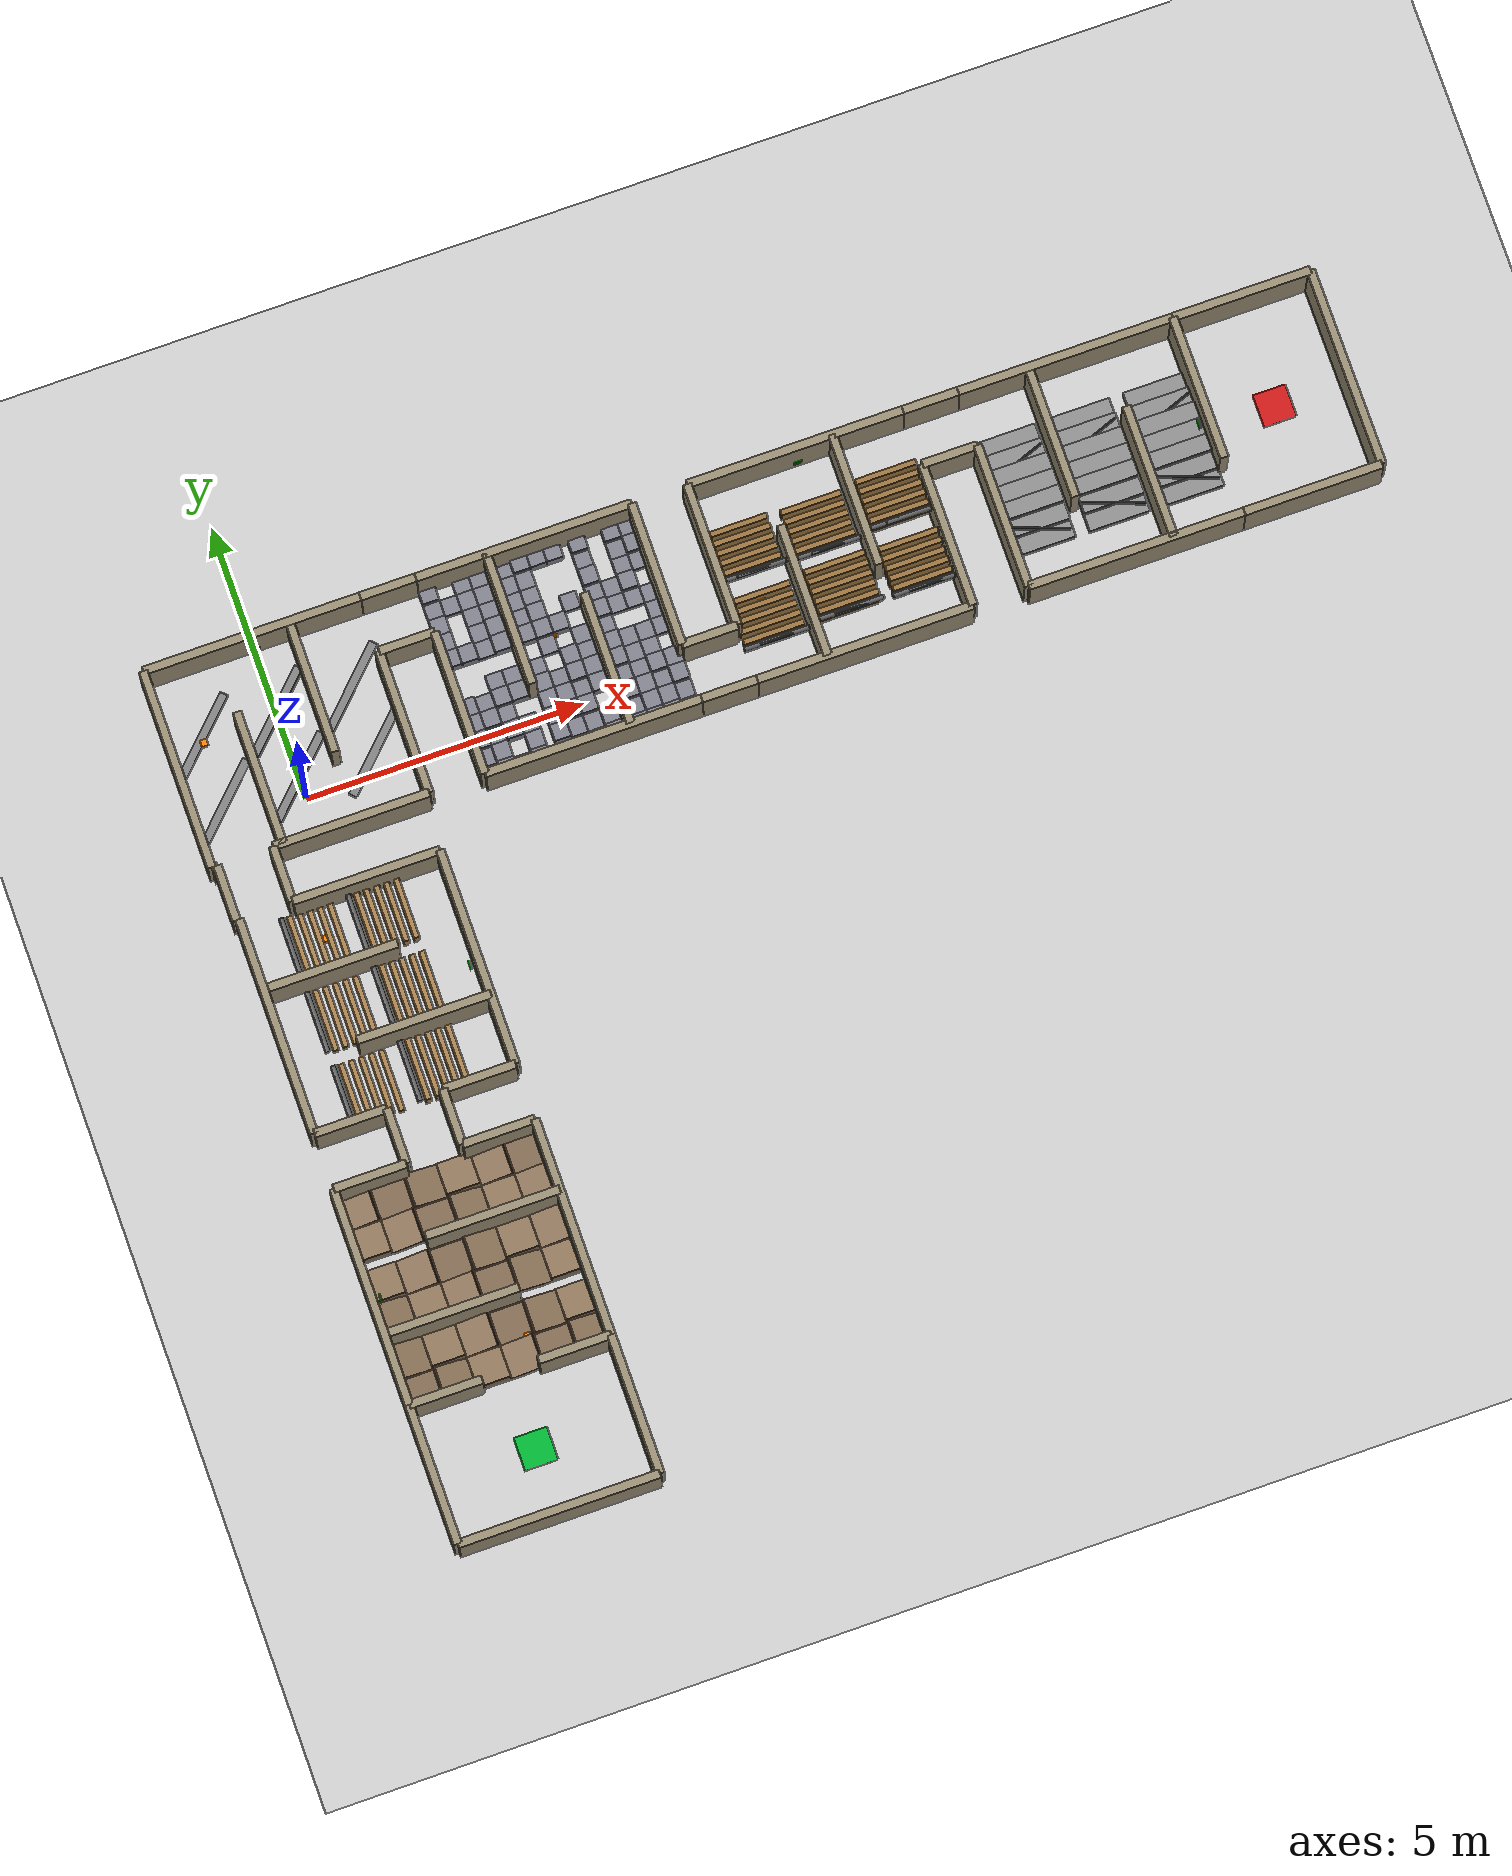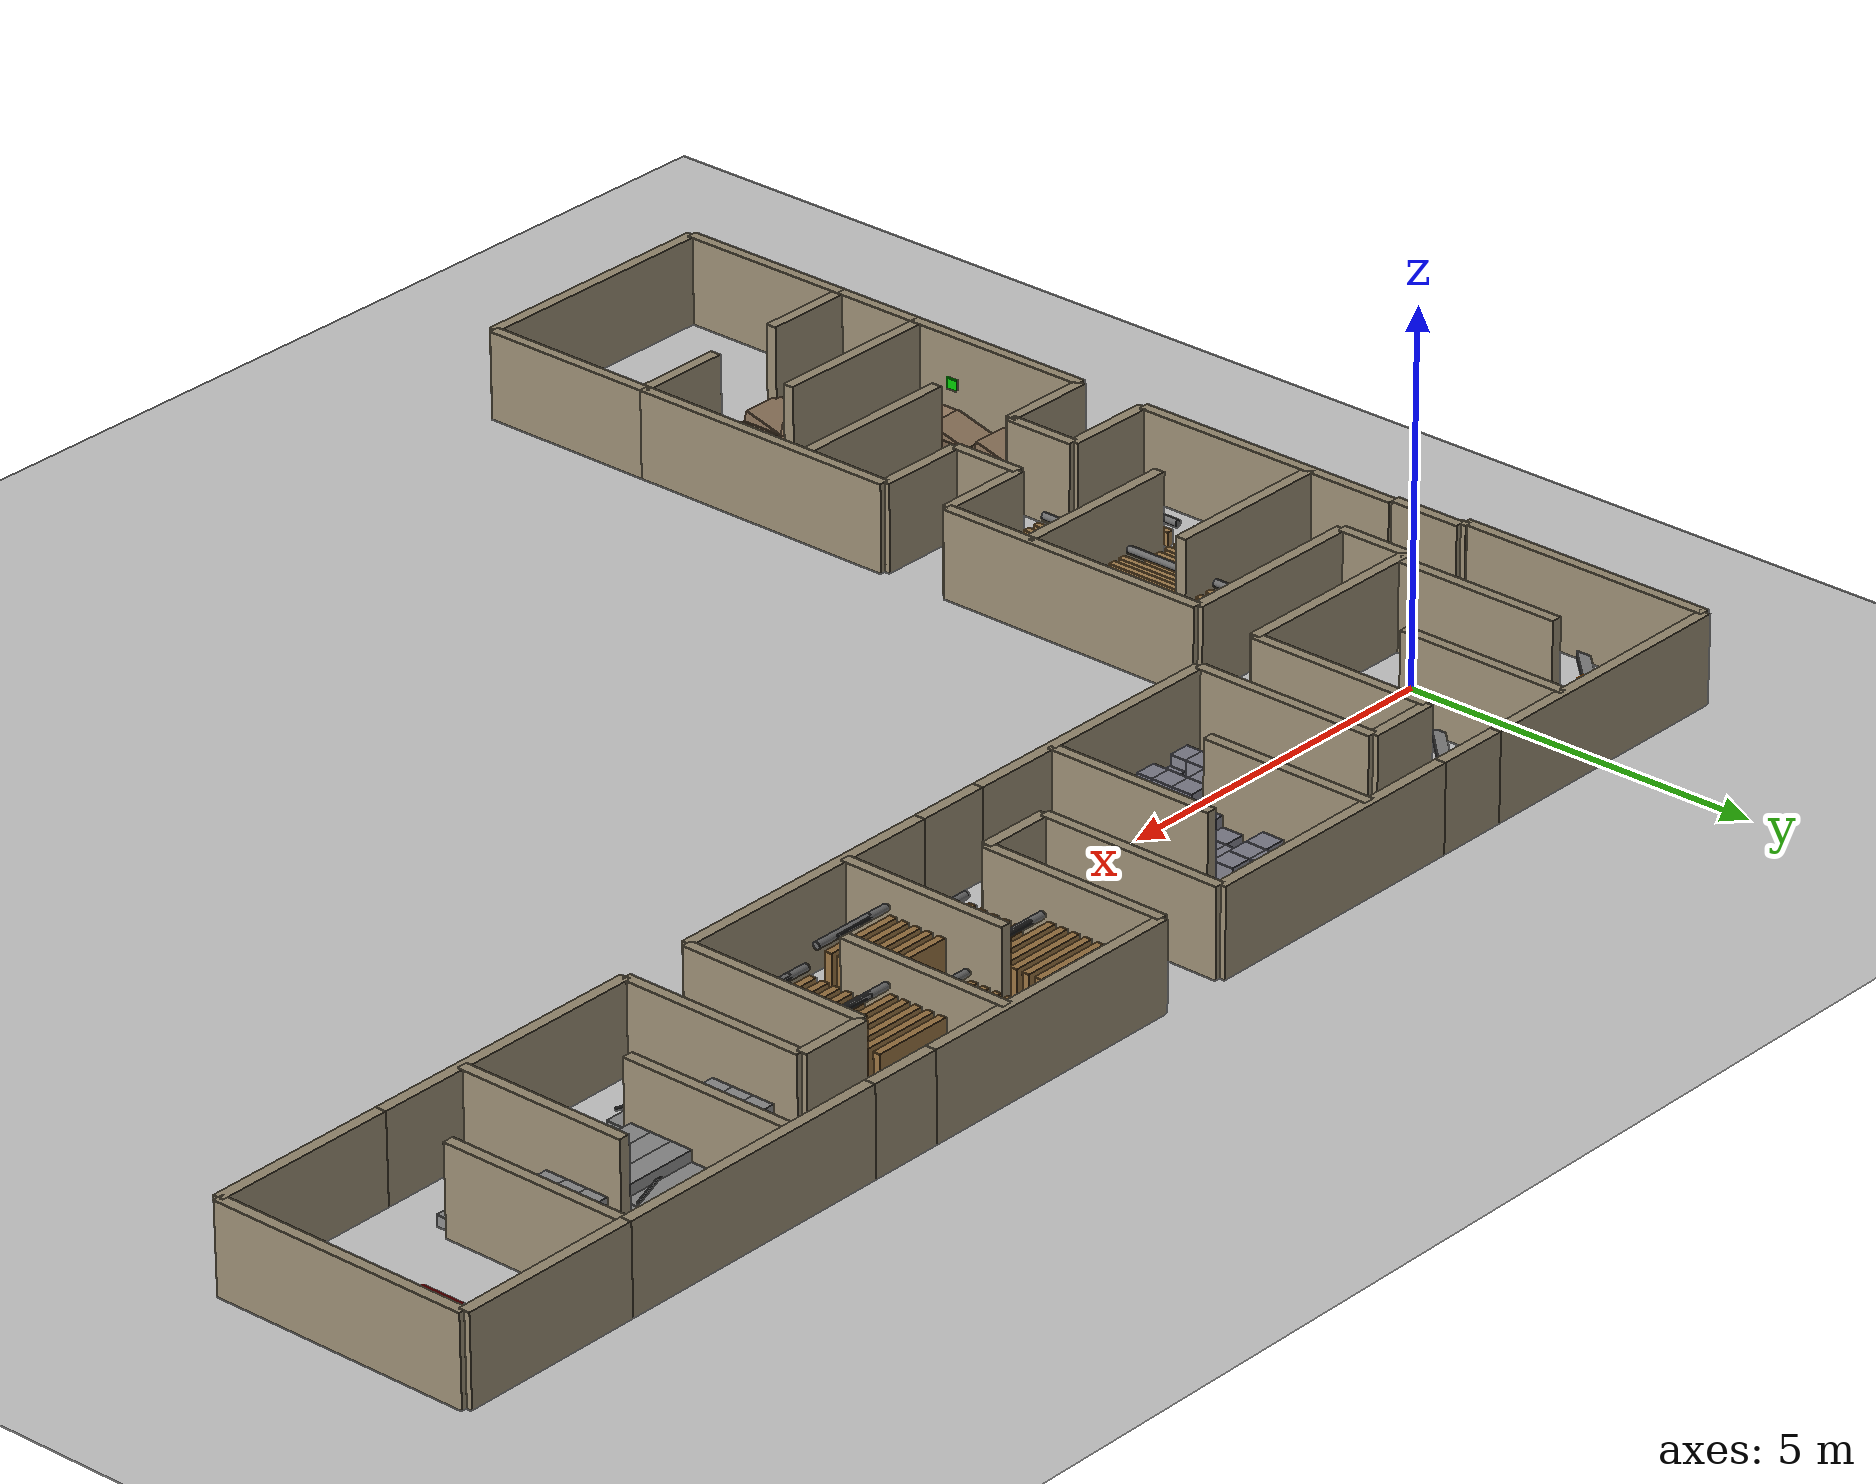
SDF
<?xml version="1.0" ?>
<sdf version="1.6">
<world name="lrc_2026">

  <!-- ROS Gazebo plugins for spawn_entity and clock -->
  <plugin name="gazebo_ros_state" filename="libgazebo_ros_state.so"/>
  <plugin name="gazebo_ros_factory" filename="libgazebo_ros_factory.so"/>

  <physics type="ode">
    <max_step_size>0.002</max_step_size>
    <real_time_factor>1.0</real_time_factor>
    <real_time_update_rate>500</real_time_update_rate>
    <ode>
      <solver>
        <type>quick</type>
        <iters>25</iters>
      </solver>
    </ode>
  </physics>

  <scene>
    <ambient>0.6 0.6 0.6 1</ambient>
    <background>0.7 0.8 0.9 1</background>
  </scene>

  <light name="sun" type="directional">
    <cast_shadows>true</cast_shadows>
    <pose>0 0 10 0 0 0</pose>
    <diffuse>0.8 0.8 0.8 1</diffuse>
    <specular>0.2 0.2 0.2 1</specular>
    <direction>-0.5 0.1 -0.9</direction>
  </light>

  <model name="ground_plane">
    <static>true</static>
    <link name="link">
      <collision name="collision">
        <geometry><plane><normal>0 0 1</normal><size>50 50</size></plane></geometry>
      </collision>
      <visual name="visual">
        <geometry><plane><normal>0 0 1</normal><size>50 50</size></plane></geometry>
        <material>
          <ambient>0.8 0.8 0.8 1</ambient>
          <diffuse>0.8 0.8 0.8 1</diffuse>
        </material>
      </visual>
    </link>
  </model>

  <model name="LA_S_a">
    <static>true</static>
    <pose>-1.1500 -10.6000 0.6000 0.0000 0.0000 0.0000</pose>
    <link name="link">
      <collision name="col">
        <geometry><box><size>1.3000 0.1500 1.2000</size></box></geometry>
      </collision>
      <visual name="vis">
        <geometry><box><size>1.3000 0.1500 1.2000</size></box></geometry>
        <material>
          <ambient>0.6 0.55 0.45 1.0</ambient>
          <diffuse>0.6 0.55 0.45 1.0</diffuse>
        </material>
      </visual>
    </link>
  </model>
  <model name="LA_S_b">
    <static>true</static>
    <pose>1.1500 -10.6000 0.6000 0.0000 0.0000 0.0000</pose>
    <link name="link">
      <collision name="col">
        <geometry><box><size>1.3000 0.1500 1.2000</size></box></geometry>
      </collision>
      <visual name="vis">
        <geometry><box><size>1.3000 0.1500 1.2000</size></box></geometry>
        <material>
          <ambient>0.6 0.55 0.45 1.0</ambient>
          <diffuse>0.6 0.55 0.45 1.0</diffuse>
        </material>
      </visual>
    </link>
  </model>
  <model name="LA_N_a">
    <static>true</static>
    <pose>-1.1500 -6.7000 0.6000 0.0000 0.0000 0.0000</pose>
    <link name="link">
      <collision name="col">
        <geometry><box><size>1.3000 0.1500 1.2000</size></box></geometry>
      </collision>
      <visual name="vis">
        <geometry><box><size>1.3000 0.1500 1.2000</size></box></geometry>
        <material>
          <ambient>0.6 0.55 0.45 1.0</ambient>
          <diffuse>0.6 0.55 0.45 1.0</diffuse>
        </material>
      </visual>
    </link>
  </model>
  <model name="LA_N_b">
    <static>true</static>
    <pose>1.1500 -6.7000 0.6000 0.0000 0.0000 0.0000</pose>
    <link name="link">
      <collision name="col">
        <geometry><box><size>1.3000 0.1500 1.2000</size></box></geometry>
      </collision>
      <visual name="vis">
        <geometry><box><size>1.3000 0.1500 1.2000</size></box></geometry>
        <material>
          <ambient>0.6 0.55 0.45 1.0</ambient>
          <diffuse>0.6 0.55 0.45 1.0</diffuse>
        </material>
      </visual>
    </link>
  </model>
  <model name="LA_W">
    <static>true</static>
    <pose>-1.8000 -8.6500 0.6000 0.0000 0.0000 0.0000</pose>
    <link name="link">
      <collision name="col">
        <geometry><box><size>0.1500 3.9000 1.2000</size></box></geometry>
      </collision>
      <visual name="vis">
        <geometry><box><size>0.1500 3.9000 1.2000</size></box></geometry>
        <material>
          <ambient>0.6 0.55 0.45 1.0</ambient>
          <diffuse>0.6 0.55 0.45 1.0</diffuse>
        </material>
      </visual>
    </link>
  </model>
  <model name="LA_E">
    <static>true</static>
    <pose>1.8000 -8.6500 0.6000 0.0000 0.0000 0.0000</pose>
    <link name="link">
      <collision name="col">
        <geometry><box><size>0.1500 3.9000 1.2000</size></box></geometry>
      </collision>
      <visual name="vis">
        <geometry><box><size>0.1500 3.9000 1.2000</size></box></geometry>
        <material>
          <ambient>0.6 0.55 0.45 1.0</ambient>
          <diffuse>0.6 0.55 0.45 1.0</diffuse>
        </material>
      </visual>
    </link>
  </model>
  <model name="LA_d0">
    <static>true</static>
    <pose>-0.6000 -9.3250 0.6000 0.0000 0.0000 0.0000</pose>
    <link name="link">
      <collision name="col">
        <geometry><box><size>2.4000 0.1500 1.2000</size></box></geometry>
      </collision>
      <visual name="vis">
        <geometry><box><size>2.4000 0.1500 1.2000</size></box></geometry>
        <material>
          <ambient>0.6 0.55 0.45 1.0</ambient>
          <diffuse>0.6 0.55 0.45 1.0</diffuse>
        </material>
      </visual>
    </link>
  </model>
  <model name="LA_d1">
    <static>true</static>
    <pose>0.6000 -7.9750 0.6000 0.0000 0.0000 0.0000</pose>
    <link name="link">
      <collision name="col">
        <geometry><box><size>2.4000 0.1500 1.2000</size></box></geometry>
      </collision>
      <visual name="vis">
        <geometry><box><size>2.4000 0.1500 1.2000</size></box></geometry>
        <material>
          <ambient>0.6 0.55 0.45 1.0</ambient>
          <diffuse>0.6 0.55 0.45 1.0</diffuse>
        </material>
      </visual>
    </link>
  </model>
  <model name="ramp_0_0_0">
    <static>true</static>
    <pose>-1.5000 -10.3000 0.0800 0.2618 0 0</pose>
    <link name="link">
      <collision name="col">
        <geometry><box><size>0.6000 0.6000 0.1600</size></box></geometry>
      </collision>
      <visual name="vis">
        <geometry><box><size>0.6000 0.6000 0.1600</size></box></geometry>
        <material>
          <ambient>0.55 0.45 0.35 1.0</ambient>
          <diffuse>0.55 0.45 0.35 1.0</diffuse>
        </material>
      </visual>
    </link>
  </model>
  <model name="ramp_0_0_1">
    <static>true</static>
    <pose>-0.9000 -10.3000 0.0800 0 0.2618 0</pose>
    <link name="link">
      <collision name="col">
        <geometry><box><size>0.6000 0.6000 0.1600</size></box></geometry>
      </collision>
      <visual name="vis">
        <geometry><box><size>0.6000 0.6000 0.1600</size></box></geometry>
        <material>
          <ambient>0.55 0.45 0.35 1.0</ambient>
          <diffuse>0.55 0.45 0.35 1.0</diffuse>
        </material>
      </visual>
    </link>
  </model>
  <model name="ramp_0_0_2">
    <static>true</static>
    <pose>-0.3000 -10.3000 0.0800 -0.2618 0 0</pose>
    <link name="link">
      <collision name="col">
        <geometry><box><size>0.6000 0.6000 0.1600</size></box></geometry>
      </collision>
      <visual name="vis">
        <geometry><box><size>0.6000 0.6000 0.1600</size></box></geometry>
        <material>
          <ambient>0.55 0.45 0.35 1.0</ambient>
          <diffuse>0.55 0.45 0.35 1.0</diffuse>
        </material>
      </visual>
    </link>
  </model>
  <model name="ramp_0_0_3">
    <static>true</static>
    <pose>0.3000 -10.3000 0.0800 0 -0.2618 0</pose>
    <link name="link">
      <collision name="col">
        <geometry><box><size>0.6000 0.6000 0.1600</size></box></geometry>
      </collision>
      <visual name="vis">
        <geometry><box><size>0.6000 0.6000 0.1600</size></box></geometry>
        <material>
          <ambient>0.55 0.45 0.35 1.0</ambient>
          <diffuse>0.55 0.45 0.35 1.0</diffuse>
        </material>
      </visual>
    </link>
  </model>
  <model name="ramp_0_0_4">
    <static>true</static>
    <pose>0.9000 -10.3000 0.0800 0.2618 0 0</pose>
    <link name="link">
      <collision name="col">
        <geometry><box><size>0.6000 0.6000 0.1600</size></box></geometry>
      </collision>
      <visual name="vis">
        <geometry><box><size>0.6000 0.6000 0.1600</size></box></geometry>
        <material>
          <ambient>0.55 0.45 0.35 1.0</ambient>
          <diffuse>0.55 0.45 0.35 1.0</diffuse>
        </material>
      </visual>
    </link>
  </model>
  <model name="ramp_0_0_5">
    <static>true</static>
    <pose>1.5000 -10.3000 0.0800 0 0.2618 0</pose>
    <link name="link">
      <collision name="col">
        <geometry><box><size>0.6000 0.6000 0.1600</size></box></geometry>
      </collision>
      <visual name="vis">
        <geometry><box><size>0.6000 0.6000 0.1600</size></box></geometry>
        <material>
          <ambient>0.55 0.45 0.35 1.0</ambient>
          <diffuse>0.55 0.45 0.35 1.0</diffuse>
        </material>
      </visual>
    </link>
  </model>
  <model name="ramp_0_1_0">
    <static>true</static>
    <pose>-1.5000 -9.7000 0.0800 0 0.2618 0</pose>
    <link name="link">
      <collision name="col">
        <geometry><box><size>0.6000 0.6000 0.1600</size></box></geometry>
      </collision>
      <visual name="vis">
        <geometry><box><size>0.6000 0.6000 0.1600</size></box></geometry>
        <material>
          <ambient>0.55 0.45 0.35 1.0</ambient>
          <diffuse>0.55 0.45 0.35 1.0</diffuse>
        </material>
      </visual>
    </link>
  </model>
  <model name="ramp_0_1_1">
    <static>true</static>
    <pose>-0.9000 -9.7000 0.0800 -0.2618 0 0</pose>
    <link name="link">
      <collision name="col">
        <geometry><box><size>0.6000 0.6000 0.1600</size></box></geometry>
      </collision>
      <visual name="vis">
        <geometry><box><size>0.6000 0.6000 0.1600</size></box></geometry>
        <material>
          <ambient>0.55 0.45 0.35 1.0</ambient>
          <diffuse>0.55 0.45 0.35 1.0</diffuse>
        </material>
      </visual>
    </link>
  </model>
  <model name="ramp_0_1_2">
    <static>true</static>
    <pose>-0.3000 -9.7000 0.0800 0 -0.2618 0</pose>
    <link name="link">
      <collision name="col">
        <geometry><box><size>0.6000 0.6000 0.1600</size></box></geometry>
      </collision>
      <visual name="vis">
        <geometry><box><size>0.6000 0.6000 0.1600</size></box></geometry>
        <material>
          <ambient>0.55 0.45 0.35 1.0</ambient>
          <diffuse>0.55 0.45 0.35 1.0</diffuse>
        </material>
      </visual>
    </link>
  </model>
  <model name="ramp_0_1_3">
    <static>true</static>
    <pose>0.3000 -9.7000 0.0800 0.2618 0 0</pose>
    <link name="link">
      <collision name="col">
        <geometry><box><size>0.6000 0.6000 0.1600</size></box></geometry>
      </collision>
      <visual name="vis">
        <geometry><box><size>0.6000 0.6000 0.1600</size></box></geometry>
        <material>
          <ambient>0.55 0.45 0.35 1.0</ambient>
          <diffuse>0.55 0.45 0.35 1.0</diffuse>
        </material>
      </visual>
    </link>
  </model>
  <model name="ramp_0_1_4">
    <static>true</static>
    <pose>0.9000 -9.7000 0.0800 0 0.2618 0</pose>
    <link name="link">
      <collision name="col">
        <geometry><box><size>0.6000 0.6000 0.1600</size></box></geometry>
      </collision>
      <visual name="vis">
        <geometry><box><size>0.6000 0.6000 0.1600</size></box></geometry>
        <material>
          <ambient>0.55 0.45 0.35 1.0</ambient>
          <diffuse>0.55 0.45 0.35 1.0</diffuse>
        </material>
      </visual>
    </link>
  </model>
  <model name="ramp_0_1_5">
    <static>true</static>
    <pose>1.5000 -9.7000 0.0800 -0.2618 0 0</pose>
    <link name="link">
      <collision name="col">
        <geometry><box><size>0.6000 0.6000 0.1600</size></box></geometry>
      </collision>
      <visual name="vis">
        <geometry><box><size>0.6000 0.6000 0.1600</size></box></geometry>
        <material>
          <ambient>0.55 0.45 0.35 1.0</ambient>
          <diffuse>0.55 0.45 0.35 1.0</diffuse>
        </material>
      </visual>
    </link>
  </model>
  <model name="ramp_1_0_0">
    <static>true</static>
    <pose>-1.5000 -8.9500 0.0800 0 0.2618 0</pose>
    <link name="link">
      <collision name="col">
        <geometry><box><size>0.6000 0.6000 0.1600</size></box></geometry>
      </collision>
      <visual name="vis">
        <geometry><box><size>0.6000 0.6000 0.1600</size></box></geometry>
        <material>
          <ambient>0.55 0.45 0.35 1.0</ambient>
          <diffuse>0.55 0.45 0.35 1.0</diffuse>
        </material>
      </visual>
    </link>
  </model>
  <model name="ramp_1_0_1">
    <static>true</static>
    <pose>-0.9000 -8.9500 0.0800 -0.2618 0 0</pose>
    <link name="link">
      <collision name="col">
        <geometry><box><size>0.6000 0.6000 0.1600</size></box></geometry>
      </collision>
      <visual name="vis">
        <geometry><box><size>0.6000 0.6000 0.1600</size></box></geometry>
        <material>
          <ambient>0.55 0.45 0.35 1.0</ambient>
          <diffuse>0.55 0.45 0.35 1.0</diffuse>
        </material>
      </visual>
    </link>
  </model>
  <model name="ramp_1_0_2">
    <static>true</static>
    <pose>-0.3000 -8.9500 0.0800 0 -0.2618 0</pose>
    <link name="link">
      <collision name="col">
        <geometry><box><size>0.6000 0.6000 0.1600</size></box></geometry>
      </collision>
      <visual name="vis">
        <geometry><box><size>0.6000 0.6000 0.1600</size></box></geometry>
        <material>
          <ambient>0.55 0.45 0.35 1.0</ambient>
          <diffuse>0.55 0.45 0.35 1.0</diffuse>
        </material>
      </visual>
    </link>
  </model>
  <model name="ramp_1_0_3">
    <static>true</static>
    <pose>0.3000 -8.9500 0.0800 0.2618 0 0</pose>
    <link name="link">
      <collision name="col">
        <geometry><box><size>0.6000 0.6000 0.1600</size></box></geometry>
      </collision>
      <visual name="vis">
        <geometry><box><size>0.6000 0.6000 0.1600</size></box></geometry>
        <material>
          <ambient>0.55 0.45 0.35 1.0</ambient>
          <diffuse>0.55 0.45 0.35 1.0</diffuse>
        </material>
      </visual>
    </link>
  </model>
  <model name="ramp_1_0_4">
    <static>true</static>
    <pose>0.9000 -8.9500 0.0800 0 0.2618 0</pose>
    <link name="link">
      <collision name="col">
        <geometry><box><size>0.6000 0.6000 0.1600</size></box></geometry>
      </collision>
      <visual name="vis">
        <geometry><box><size>0.6000 0.6000 0.1600</size></box></geometry>
        <material>
          <ambient>0.55 0.45 0.35 1.0</ambient>
          <diffuse>0.55 0.45 0.35 1.0</diffuse>
        </material>
      </visual>
    </link>
  </model>
  <model name="ramp_1_0_5">
    <static>true</static>
    <pose>1.5000 -8.9500 0.0800 -0.2618 0 0</pose>
    <link name="link">
      <collision name="col">
        <geometry><box><size>0.6000 0.6000 0.1600</size></box></geometry>
      </collision>
      <visual name="vis">
        <geometry><box><size>0.6000 0.6000 0.1600</size></box></geometry>
        <material>
          <ambient>0.55 0.45 0.35 1.0</ambient>
          <diffuse>0.55 0.45 0.35 1.0</diffuse>
        </material>
      </visual>
    </link>
  </model>
  <model name="ramp_1_1_0">
    <static>true</static>
    <pose>-1.5000 -8.3500 0.0800 -0.2618 0 0</pose>
    <link name="link">
      <collision name="col">
        <geometry><box><size>0.6000 0.6000 0.1600</size></box></geometry>
      </collision>
      <visual name="vis">
        <geometry><box><size>0.6000 0.6000 0.1600</size></box></geometry>
        <material>
          <ambient>0.55 0.45 0.35 1.0</ambient>
          <diffuse>0.55 0.45 0.35 1.0</diffuse>
        </material>
      </visual>
    </link>
  </model>
  <model name="ramp_1_1_1">
    <static>true</static>
    <pose>-0.9000 -8.3500 0.0800 0 -0.2618 0</pose>
    <link name="link">
      <collision name="col">
        <geometry><box><size>0.6000 0.6000 0.1600</size></box></geometry>
      </collision>
      <visual name="vis">
        <geometry><box><size>0.6000 0.6000 0.1600</size></box></geometry>
        <material>
          <ambient>0.55 0.45 0.35 1.0</ambient>
          <diffuse>0.55 0.45 0.35 1.0</diffuse>
        </material>
      </visual>
    </link>
  </model>
  <model name="ramp_1_1_2">
    <static>true</static>
    <pose>-0.3000 -8.3500 0.0800 0.2618 0 0</pose>
    <link name="link">
      <collision name="col">
        <geometry><box><size>0.6000 0.6000 0.1600</size></box></geometry>
      </collision>
      <visual name="vis">
        <geometry><box><size>0.6000 0.6000 0.1600</size></box></geometry>
        <material>
          <ambient>0.55 0.45 0.35 1.0</ambient>
          <diffuse>0.55 0.45 0.35 1.0</diffuse>
        </material>
      </visual>
    </link>
  </model>
  <model name="ramp_1_1_3">
    <static>true</static>
    <pose>0.3000 -8.3500 0.0800 0 0.2618 0</pose>
    <link name="link">
      <collision name="col">
        <geometry><box><size>0.6000 0.6000 0.1600</size></box></geometry>
      </collision>
      <visual name="vis">
        <geometry><box><size>0.6000 0.6000 0.1600</size></box></geometry>
        <material>
          <ambient>0.55 0.45 0.35 1.0</ambient>
          <diffuse>0.55 0.45 0.35 1.0</diffuse>
        </material>
      </visual>
    </link>
  </model>
  <model name="ramp_1_1_4">
    <static>true</static>
    <pose>0.9000 -8.3500 0.0800 -0.2618 0 0</pose>
    <link name="link">
      <collision name="col">
        <geometry><box><size>0.6000 0.6000 0.1600</size></box></geometry>
      </collision>
      <visual name="vis">
        <geometry><box><size>0.6000 0.6000 0.1600</size></box></geometry>
        <material>
          <ambient>0.55 0.45 0.35 1.0</ambient>
          <diffuse>0.55 0.45 0.35 1.0</diffuse>
        </material>
      </visual>
    </link>
  </model>
  <model name="ramp_1_1_5">
    <static>true</static>
    <pose>1.5000 -8.3500 0.0800 0 -0.2618 0</pose>
    <link name="link">
      <collision name="col">
        <geometry><box><size>0.6000 0.6000 0.1600</size></box></geometry>
      </collision>
      <visual name="vis">
        <geometry><box><size>0.6000 0.6000 0.1600</size></box></geometry>
        <material>
          <ambient>0.55 0.45 0.35 1.0</ambient>
          <diffuse>0.55 0.45 0.35 1.0</diffuse>
        </material>
      </visual>
    </link>
  </model>
  <model name="ramp_2_0_0">
    <static>true</static>
    <pose>-1.5000 -7.6000 0.0800 -0.2618 0 0</pose>
    <link name="link">
      <collision name="col">
        <geometry><box><size>0.6000 0.6000 0.1600</size></box></geometry>
      </collision>
      <visual name="vis">
        <geometry><box><size>0.6000 0.6000 0.1600</size></box></geometry>
        <material>
          <ambient>0.55 0.45 0.35 1.0</ambient>
          <diffuse>0.55 0.45 0.35 1.0</diffuse>
        </material>
      </visual>
    </link>
  </model>
  <model name="ramp_2_0_1">
    <static>true</static>
    <pose>-0.9000 -7.6000 0.0800 0 -0.2618 0</pose>
    <link name="link">
      <collision name="col">
        <geometry><box><size>0.6000 0.6000 0.1600</size></box></geometry>
      </collision>
      <visual name="vis">
        <geometry><box><size>0.6000 0.6000 0.1600</size></box></geometry>
        <material>
          <ambient>0.55 0.45 0.35 1.0</ambient>
          <diffuse>0.55 0.45 0.35 1.0</diffuse>
        </material>
      </visual>
    </link>
  </model>
  <model name="ramp_2_0_2">
    <static>true</static>
    <pose>-0.3000 -7.6000 0.0800 0.2618 0 0</pose>
    <link name="link">
      <collision name="col">
        <geometry><box><size>0.6000 0.6000 0.1600</size></box></geometry>
      </collision>
      <visual name="vis">
        <geometry><box><size>0.6000 0.6000 0.1600</size></box></geometry>
        <material>
          <ambient>0.55 0.45 0.35 1.0</ambient>
          <diffuse>0.55 0.45 0.35 1.0</diffuse>
        </material>
      </visual>
    </link>
  </model>
  <model name="ramp_2_0_3">
    <static>true</static>
    <pose>0.3000 -7.6000 0.0800 0 0.2618 0</pose>
    <link name="link">
      <collision name="col">
        <geometry><box><size>0.6000 0.6000 0.1600</size></box></geometry>
      </collision>
      <visual name="vis">
        <geometry><box><size>0.6000 0.6000 0.1600</size></box></geometry>
        <material>
          <ambient>0.55 0.45 0.35 1.0</ambient>
          <diffuse>0.55 0.45 0.35 1.0</diffuse>
        </material>
      </visual>
    </link>
  </model>
  <model name="ramp_2_0_4">
    <static>true</static>
    <pose>0.9000 -7.6000 0.0800 -0.2618 0 0</pose>
    <link name="link">
      <collision name="col">
        <geometry><box><size>0.6000 0.6000 0.1600</size></box></geometry>
      </collision>
      <visual name="vis">
        <geometry><box><size>0.6000 0.6000 0.1600</size></box></geometry>
        <material>
          <ambient>0.55 0.45 0.35 1.0</ambient>
          <diffuse>0.55 0.45 0.35 1.0</diffuse>
        </material>
      </visual>
    </link>
  </model>
  <model name="ramp_2_0_5">
    <static>true</static>
    <pose>1.5000 -7.6000 0.0800 0 -0.2618 0</pose>
    <link name="link">
      <collision name="col">
        <geometry><box><size>0.6000 0.6000 0.1600</size></box></geometry>
      </collision>
      <visual name="vis">
        <geometry><box><size>0.6000 0.6000 0.1600</size></box></geometry>
        <material>
          <ambient>0.55 0.45 0.35 1.0</ambient>
          <diffuse>0.55 0.45 0.35 1.0</diffuse>
        </material>
      </visual>
    </link>
  </model>
  <model name="ramp_2_1_0">
    <static>true</static>
    <pose>-1.5000 -7.0000 0.0800 0 -0.2618 0</pose>
    <link name="link">
      <collision name="col">
        <geometry><box><size>0.6000 0.6000 0.1600</size></box></geometry>
      </collision>
      <visual name="vis">
        <geometry><box><size>0.6000 0.6000 0.1600</size></box></geometry>
        <material>
          <ambient>0.55 0.45 0.35 1.0</ambient>
          <diffuse>0.55 0.45 0.35 1.0</diffuse>
        </material>
      </visual>
    </link>
  </model>
  <model name="ramp_2_1_1">
    <static>true</static>
    <pose>-0.9000 -7.0000 0.0800 0.2618 0 0</pose>
    <link name="link">
      <collision name="col">
        <geometry><box><size>0.6000 0.6000 0.1600</size></box></geometry>
      </collision>
      <visual name="vis">
        <geometry><box><size>0.6000 0.6000 0.1600</size></box></geometry>
        <material>
          <ambient>0.55 0.45 0.35 1.0</ambient>
          <diffuse>0.55 0.45 0.35 1.0</diffuse>
        </material>
      </visual>
    </link>
  </model>
  <model name="ramp_2_1_2">
    <static>true</static>
    <pose>-0.3000 -7.0000 0.0800 0 0.2618 0</pose>
    <link name="link">
      <collision name="col">
        <geometry><box><size>0.6000 0.6000 0.1600</size></box></geometry>
      </collision>
      <visual name="vis">
        <geometry><box><size>0.6000 0.6000 0.1600</size></box></geometry>
        <material>
          <ambient>0.55 0.45 0.35 1.0</ambient>
          <diffuse>0.55 0.45 0.35 1.0</diffuse>
        </material>
      </visual>
    </link>
  </model>
  <model name="ramp_2_1_3">
    <static>true</static>
    <pose>0.3000 -7.0000 0.0800 -0.2618 0 0</pose>
    <link name="link">
      <collision name="col">
        <geometry><box><size>0.6000 0.6000 0.1600</size></box></geometry>
      </collision>
      <visual name="vis">
        <geometry><box><size>0.6000 0.6000 0.1600</size></box></geometry>
        <material>
          <ambient>0.55 0.45 0.35 1.0</ambient>
          <diffuse>0.55 0.45 0.35 1.0</diffuse>
        </material>
      </visual>
    </link>
  </model>
  <model name="ramp_2_1_4">
    <static>true</static>
    <pose>0.9000 -7.0000 0.0800 0 -0.2618 0</pose>
    <link name="link">
      <collision name="col">
        <geometry><box><size>0.6000 0.6000 0.1600</size></box></geometry>
      </collision>
      <visual name="vis">
        <geometry><box><size>0.6000 0.6000 0.1600</size></box></geometry>
        <material>
          <ambient>0.55 0.45 0.35 1.0</ambient>
          <diffuse>0.55 0.45 0.35 1.0</diffuse>
        </material>
      </visual>
    </link>
  </model>
  <model name="ramp_2_1_5">
    <static>true</static>
    <pose>1.5000 -7.0000 0.0800 0.2618 0 0</pose>
    <link name="link">
      <collision name="col">
        <geometry><box><size>0.6000 0.6000 0.1600</size></box></geometry>
      </collision>
      <visual name="vis">
        <geometry><box><size>0.6000 0.6000 0.1600</size></box></geometry>
        <material>
          <ambient>0.55 0.45 0.35 1.0</ambient>
          <diffuse>0.55 0.45 0.35 1.0</diffuse>
        </material>
      </visual>
    </link>
  </model>
  <model name="qr_A">
    <static>true</static>
    <pose>-1.6500 -8.6500 0.6000 0.0000 0.0000 0.0000</pose>
    <link name="link">
      <collision name="col">
        <geometry><box><size>0.0200 0.1500 0.1500</size></box></geometry>
      </collision>
      <visual name="vis">
        <geometry><box><size>0.0200 0.1500 0.1500</size></box></geometry>
        <material>
          <ambient>0.0 0.8 0.0 1.0</ambient>
          <diffuse>0.0 0.8 0.0 1.0</diffuse>
        </material>
      </visual>
    </link>
  </model>
  <model name="haz_A">
    <static>true</static>
    <pose>0.5000 -10.0000 0.0600 0.0000 0.0000 0.0000</pose>
    <link name="link">
      <collision name="col">
        <geometry><box><size>0.1200 0.1200 0.1200</size></box></geometry>
      </collision>
      <visual name="vis">
        <geometry><box><size>0.1200 0.1200 0.1200</size></box></geometry>
        <material>
          <ambient>1.0 0.5 0.0 1.0</ambient>
          <diffuse>1.0 0.5 0.0 1.0</diffuse>
        </material>
      </visual>
    </link>
  </model>
  <model name="LB_S_a">
    <static>true</static>
    <pose>-1.1500 -5.7000 0.6000 0.0000 0.0000 0.0000</pose>
    <link name="link">
      <collision name="col">
        <geometry><box><size>1.3000 0.1500 1.2000</size></box></geometry>
      </collision>
      <visual name="vis">
        <geometry><box><size>1.3000 0.1500 1.2000</size></box></geometry>
        <material>
          <ambient>0.6 0.55 0.45 1.0</ambient>
          <diffuse>0.6 0.55 0.45 1.0</diffuse>
        </material>
      </visual>
    </link>
  </model>
  <model name="LB_S_b">
    <static>true</static>
    <pose>1.1500 -5.7000 0.6000 0.0000 0.0000 0.0000</pose>
    <link name="link">
      <collision name="col">
        <geometry><box><size>1.3000 0.1500 1.2000</size></box></geometry>
      </collision>
      <visual name="vis">
        <geometry><box><size>1.3000 0.1500 1.2000</size></box></geometry>
        <material>
          <ambient>0.6 0.55 0.45 1.0</ambient>
          <diffuse>0.6 0.55 0.45 1.0</diffuse>
        </material>
      </visual>
    </link>
  </model>
  <model name="LB_N_b">
    <static>true</static>
    <pose>0.4750 -1.8000 0.6000 0.0000 0.0000 0.0000</pose>
    <link name="link">
      <collision name="col">
        <geometry><box><size>2.6500 0.1500 1.2000</size></box></geometry>
      </collision>
      <visual name="vis">
        <geometry><box><size>2.6500 0.1500 1.2000</size></box></geometry>
        <material>
          <ambient>0.6 0.55 0.45 1.0</ambient>
          <diffuse>0.6 0.55 0.45 1.0</diffuse>
        </material>
      </visual>
    </link>
  </model>
  <model name="LB_W">
    <static>true</static>
    <pose>-1.8000 -3.7500 0.6000 0.0000 0.0000 0.0000</pose>
    <link name="link">
      <collision name="col">
        <geometry><box><size>0.1500 3.9000 1.2000</size></box></geometry>
      </collision>
      <visual name="vis">
        <geometry><box><size>0.1500 3.9000 1.2000</size></box></geometry>
        <material>
          <ambient>0.6 0.55 0.45 1.0</ambient>
          <diffuse>0.6 0.55 0.45 1.0</diffuse>
        </material>
      </visual>
    </link>
  </model>
  <model name="LB_E">
    <static>true</static>
    <pose>1.8000 -3.7500 0.6000 0.0000 0.0000 0.0000</pose>
    <link name="link">
      <collision name="col">
        <geometry><box><size>0.1500 3.9000 1.2000</size></box></geometry>
      </collision>
      <visual name="vis">
        <geometry><box><size>0.1500 3.9000 1.2000</size></box></geometry>
        <material>
          <ambient>0.6 0.55 0.45 1.0</ambient>
          <diffuse>0.6 0.55 0.45 1.0</diffuse>
        </material>
      </visual>
    </link>
  </model>
  <model name="LB_d0">
    <static>true</static>
    <pose>0.6000 -4.4250 0.6000 0.0000 0.0000 0.0000</pose>
    <link name="link">
      <collision name="col">
        <geometry><box><size>2.4000 0.1500 1.2000</size></box></geometry>
      </collision>
      <visual name="vis">
        <geometry><box><size>2.4000 0.1500 1.2000</size></box></geometry>
        <material>
          <ambient>0.6 0.55 0.45 1.0</ambient>
          <diffuse>0.6 0.55 0.45 1.0</diffuse>
        </material>
      </visual>
    </link>
  </model>
  <model name="LB_d1">
    <static>true</static>
    <pose>-0.6000 -3.0750 0.6000 0.0000 0.0000 0.0000</pose>
    <link name="link">
      <collision name="col">
        <geometry><box><size>2.4000 0.1500 1.2000</size></box></geometry>
      </collision>
      <visual name="vis">
        <geometry><box><size>2.4000 0.1500 1.2000</size></box></geometry>
        <material>
          <ambient>0.6 0.55 0.45 1.0</ambient>
          <diffuse>0.6 0.55 0.45 1.0</diffuse>
        </material>
      </visual>
    </link>
  </model>
  <model name="plt_0_0_0">
    <static>true</static>
    <pose>-0.9600 -5.1000 0.1000 0.0000 0.0000 0.0000</pose>
    <link name="link">
      <collision name="col">
        <geometry><box><size>0.1000 1.1000 0.2000</size></box></geometry>
      </collision>
      <visual name="vis">
        <geometry><box><size>0.1000 1.1000 0.2000</size></box></geometry>
        <material>
          <ambient>0.65 0.5 0.3 1.0</ambient>
          <diffuse>0.65 0.5 0.3 1.0</diffuse>
        </material>
      </visual>
    </link>
  </model>
  <model name="plt_0_0_1">
    <static>true</static>
    <pose>-0.7800 -5.1000 0.1000 0.0000 0.0000 0.0000</pose>
    <link name="link">
      <collision name="col">
        <geometry><box><size>0.1000 1.1000 0.2000</size></box></geometry>
      </collision>
      <visual name="vis">
        <geometry><box><size>0.1000 1.1000 0.2000</size></box></geometry>
        <material>
          <ambient>0.65 0.5 0.3 1.0</ambient>
          <diffuse>0.65 0.5 0.3 1.0</diffuse>
        </material>
      </visual>
    </link>
  </model>
  <model name="plt_0_0_2">
    <static>true</static>
    <pose>-0.6000 -5.1000 0.1000 0.0000 0.0000 0.0000</pose>
    <link name="link">
      <collision name="col">
        <geometry><box><size>0.1000 1.1000 0.2000</size></box></geometry>
      </collision>
      <visual name="vis">
        <geometry><box><size>0.1000 1.1000 0.2000</size></box></geometry>
        <material>
          <ambient>0.65 0.5 0.3 1.0</ambient>
          <diffuse>0.65 0.5 0.3 1.0</diffuse>
        </material>
      </visual>
    </link>
  </model>
  <model name="plt_0_0_3">
    <static>true</static>
    <pose>-0.4200 -5.1000 0.1000 0.0000 0.0000 0.0000</pose>
    <link name="link">
      <collision name="col">
        <geometry><box><size>0.1000 1.1000 0.2000</size></box></geometry>
      </collision>
      <visual name="vis">
        <geometry><box><size>0.1000 1.1000 0.2000</size></box></geometry>
        <material>
          <ambient>0.65 0.5 0.3 1.0</ambient>
          <diffuse>0.65 0.5 0.3 1.0</diffuse>
        </material>
      </visual>
    </link>
  </model>
  <model name="plt_0_0_4">
    <static>true</static>
    <pose>-0.2400 -5.1000 0.1000 0.0000 0.0000 0.0000</pose>
    <link name="link">
      <collision name="col">
        <geometry><box><size>0.1000 1.1000 0.2000</size></box></geometry>
      </collision>
      <visual name="vis">
        <geometry><box><size>0.1000 1.1000 0.2000</size></box></geometry>
        <material>
          <ambient>0.65 0.5 0.3 1.0</ambient>
          <diffuse>0.65 0.5 0.3 1.0</diffuse>
        </material>
      </visual>
    </link>
  </model>
  <model name="pipe_0_0">
    <static>true</static>
    <pose>-1.1000 -5.1000 0.2500 1.5708 0 0</pose>
    <link name="link">
      <collision name="col">
        <geometry><cylinder><radius>0.05</radius><length>1.1</length></cylinder></geometry>
      </collision>
      <visual name="vis">
        <geometry><cylinder><radius>0.05</radius><length>1.1</length></cylinder></geometry>
        <material>
          <ambient>0.4 0.4 0.4 1.0</ambient>
          <diffuse>0.4 0.4 0.4 1.0</diffuse>
        </material>
      </visual>
    </link>
  </model>
  <model name="plt_0_1_0">
    <static>true</static>
    <pose>0.2400 -5.1000 0.2000 0.0000 0.0000 0.0000</pose>
    <link name="link">
      <collision name="col">
        <geometry><box><size>0.1000 1.1000 0.4000</size></box></geometry>
      </collision>
      <visual name="vis">
        <geometry><box><size>0.1000 1.1000 0.4000</size></box></geometry>
        <material>
          <ambient>0.65 0.5 0.3 1.0</ambient>
          <diffuse>0.65 0.5 0.3 1.0</diffuse>
        </material>
      </visual>
    </link>
  </model>
  <model name="plt_0_1_1">
    <static>true</static>
    <pose>0.4200 -5.1000 0.2000 0.0000 0.0000 0.0000</pose>
    <link name="link">
      <collision name="col">
        <geometry><box><size>0.1000 1.1000 0.4000</size></box></geometry>
      </collision>
      <visual name="vis">
        <geometry><box><size>0.1000 1.1000 0.4000</size></box></geometry>
        <material>
          <ambient>0.65 0.5 0.3 1.0</ambient>
          <diffuse>0.65 0.5 0.3 1.0</diffuse>
        </material>
      </visual>
    </link>
  </model>
  <model name="plt_0_1_2">
    <static>true</static>
    <pose>0.6000 -5.1000 0.2000 0.0000 0.0000 0.0000</pose>
    <link name="link">
      <collision name="col">
        <geometry><box><size>0.1000 1.1000 0.4000</size></box></geometry>
      </collision>
      <visual name="vis">
        <geometry><box><size>0.1000 1.1000 0.4000</size></box></geometry>
        <material>
          <ambient>0.65 0.5 0.3 1.0</ambient>
          <diffuse>0.65 0.5 0.3 1.0</diffuse>
        </material>
      </visual>
    </link>
  </model>
  <model name="plt_0_1_3">
    <static>true</static>
    <pose>0.7800 -5.1000 0.2000 0.0000 0.0000 0.0000</pose>
    <link name="link">
      <collision name="col">
        <geometry><box><size>0.1000 1.1000 0.4000</size></box></geometry>
      </collision>
      <visual name="vis">
        <geometry><box><size>0.1000 1.1000 0.4000</size></box></geometry>
        <material>
          <ambient>0.65 0.5 0.3 1.0</ambient>
          <diffuse>0.65 0.5 0.3 1.0</diffuse>
        </material>
      </visual>
    </link>
  </model>
  <model name="plt_0_1_4">
    <static>true</static>
    <pose>0.9600 -5.1000 0.2000 0.0000 0.0000 0.0000</pose>
    <link name="link">
      <collision name="col">
        <geometry><box><size>0.1000 1.1000 0.4000</size></box></geometry>
      </collision>
      <visual name="vis">
        <geometry><box><size>0.1000 1.1000 0.4000</size></box></geometry>
        <material>
          <ambient>0.65 0.5 0.3 1.0</ambient>
          <diffuse>0.65 0.5 0.3 1.0</diffuse>
        </material>
      </visual>
    </link>
  </model>
  <model name="pipe_0_1">
    <static>true</static>
    <pose>0.1000 -5.1000 0.4500 1.5708 0 0</pose>
    <link name="link">
      <collision name="col">
        <geometry><cylinder><radius>0.05</radius><length>1.1</length></cylinder></geometry>
      </collision>
      <visual name="vis">
        <geometry><cylinder><radius>0.05</radius><length>1.1</length></cylinder></geometry>
        <material>
          <ambient>0.4 0.4 0.4 1.0</ambient>
          <diffuse>0.4 0.4 0.4 1.0</diffuse>
        </material>
      </visual>
    </link>
  </model>
  <model name="plt_1_0_0">
    <static>true</static>
    <pose>-0.9600 -3.7500 0.1000 0.0000 0.0000 0.0000</pose>
    <link name="link">
      <collision name="col">
        <geometry><box><size>0.1000 1.1000 0.2000</size></box></geometry>
      </collision>
      <visual name="vis">
        <geometry><box><size>0.1000 1.1000 0.2000</size></box></geometry>
        <material>
          <ambient>0.65 0.5 0.3 1.0</ambient>
          <diffuse>0.65 0.5 0.3 1.0</diffuse>
        </material>
      </visual>
    </link>
  </model>
  <model name="plt_1_0_1">
    <static>true</static>
    <pose>-0.7800 -3.7500 0.1000 0.0000 0.0000 0.0000</pose>
    <link name="link">
      <collision name="col">
        <geometry><box><size>0.1000 1.1000 0.2000</size></box></geometry>
      </collision>
      <visual name="vis">
        <geometry><box><size>0.1000 1.1000 0.2000</size></box></geometry>
        <material>
          <ambient>0.65 0.5 0.3 1.0</ambient>
          <diffuse>0.65 0.5 0.3 1.0</diffuse>
        </material>
      </visual>
    </link>
  </model>
  <model name="plt_1_0_2">
    <static>true</static>
    <pose>-0.6000 -3.7500 0.1000 0.0000 0.0000 0.0000</pose>
    <link name="link">
      <collision name="col">
        <geometry><box><size>0.1000 1.1000 0.2000</size></box></geometry>
      </collision>
      <visual name="vis">
        <geometry><box><size>0.1000 1.1000 0.2000</size></box></geometry>
        <material>
          <ambient>0.65 0.5 0.3 1.0</ambient>
          <diffuse>0.65 0.5 0.3 1.0</diffuse>
        </material>
      </visual>
    </link>
  </model>
  <model name="plt_1_0_3">
    <static>true</static>
    <pose>-0.4200 -3.7500 0.1000 0.0000 0.0000 0.0000</pose>
    <link name="link">
      <collision name="col">
        <geometry><box><size>0.1000 1.1000 0.2000</size></box></geometry>
      </collision>
      <visual name="vis">
        <geometry><box><size>0.1000 1.1000 0.2000</size></box></geometry>
        <material>
          <ambient>0.65 0.5 0.3 1.0</ambient>
          <diffuse>0.65 0.5 0.3 1.0</diffuse>
        </material>
      </visual>
    </link>
  </model>
  <model name="plt_1_0_4">
    <static>true</static>
    <pose>-0.2400 -3.7500 0.1000 0.0000 0.0000 0.0000</pose>
    <link name="link">
      <collision name="col">
        <geometry><box><size>0.1000 1.1000 0.2000</size></box></geometry>
      </collision>
      <visual name="vis">
        <geometry><box><size>0.1000 1.1000 0.2000</size></box></geometry>
        <material>
          <ambient>0.65 0.5 0.3 1.0</ambient>
          <diffuse>0.65 0.5 0.3 1.0</diffuse>
        </material>
      </visual>
    </link>
  </model>
  <model name="pipe_1_0">
    <static>true</static>
    <pose>-1.1000 -3.7500 0.2500 1.5708 0 0</pose>
    <link name="link">
      <collision name="col">
        <geometry><cylinder><radius>0.05</radius><length>1.1</length></cylinder></geometry>
      </collision>
      <visual name="vis">
        <geometry><cylinder><radius>0.05</radius><length>1.1</length></cylinder></geometry>
        <material>
          <ambient>0.4 0.4 0.4 1.0</ambient>
          <diffuse>0.4 0.4 0.4 1.0</diffuse>
        </material>
      </visual>
    </link>
  </model>
  <model name="plt_1_1_0">
    <static>true</static>
    <pose>0.2400 -3.7500 0.2000 0.0000 0.0000 0.0000</pose>
    <link name="link">
      <collision name="col">
        <geometry><box><size>0.1000 1.1000 0.4000</size></box></geometry>
      </collision>
      <visual name="vis">
        <geometry><box><size>0.1000 1.1000 0.4000</size></box></geometry>
        <material>
          <ambient>0.65 0.5 0.3 1.0</ambient>
          <diffuse>0.65 0.5 0.3 1.0</diffuse>
        </material>
      </visual>
    </link>
  </model>
  <model name="plt_1_1_1">
    <static>true</static>
    <pose>0.4200 -3.7500 0.2000 0.0000 0.0000 0.0000</pose>
    <link name="link">
      <collision name="col">
        <geometry><box><size>0.1000 1.1000 0.4000</size></box></geometry>
      </collision>
      <visual name="vis">
        <geometry><box><size>0.1000 1.1000 0.4000</size></box></geometry>
        <material>
          <ambient>0.65 0.5 0.3 1.0</ambient>
          <diffuse>0.65 0.5 0.3 1.0</diffuse>
        </material>
      </visual>
    </link>
  </model>
  <model name="plt_1_1_2">
    <static>true</static>
    <pose>0.6000 -3.7500 0.2000 0.0000 0.0000 0.0000</pose>
    <link name="link">
      <collision name="col">
        <geometry><box><size>0.1000 1.1000 0.4000</size></box></geometry>
      </collision>
      <visual name="vis">
        <geometry><box><size>0.1000 1.1000 0.4000</size></box></geometry>
        <material>
          <ambient>0.65 0.5 0.3 1.0</ambient>
          <diffuse>0.65 0.5 0.3 1.0</diffuse>
        </material>
      </visual>
    </link>
  </model>
  <model name="plt_1_1_3">
    <static>true</static>
    <pose>0.7800 -3.7500 0.2000 0.0000 0.0000 0.0000</pose>
    <link name="link">
      <collision name="col">
        <geometry><box><size>0.1000 1.1000 0.4000</size></box></geometry>
      </collision>
      <visual name="vis">
        <geometry><box><size>0.1000 1.1000 0.4000</size></box></geometry>
        <material>
          <ambient>0.65 0.5 0.3 1.0</ambient>
          <diffuse>0.65 0.5 0.3 1.0</diffuse>
        </material>
      </visual>
    </link>
  </model>
  <model name="plt_1_1_4">
    <static>true</static>
    <pose>0.9600 -3.7500 0.2000 0.0000 0.0000 0.0000</pose>
    <link name="link">
      <collision name="col">
        <geometry><box><size>0.1000 1.1000 0.4000</size></box></geometry>
      </collision>
      <visual name="vis">
        <geometry><box><size>0.1000 1.1000 0.4000</size></box></geometry>
        <material>
          <ambient>0.65 0.5 0.3 1.0</ambient>
          <diffuse>0.65 0.5 0.3 1.0</diffuse>
        </material>
      </visual>
    </link>
  </model>
  <model name="pipe_1_1">
    <static>true</static>
    <pose>0.1000 -3.7500 0.4500 1.5708 0 0</pose>
    <link name="link">
      <collision name="col">
        <geometry><cylinder><radius>0.05</radius><length>1.1</length></cylinder></geometry>
      </collision>
      <visual name="vis">
        <geometry><cylinder><radius>0.05</radius><length>1.1</length></cylinder></geometry>
        <material>
          <ambient>0.4 0.4 0.4 1.0</ambient>
          <diffuse>0.4 0.4 0.4 1.0</diffuse>
        </material>
      </visual>
    </link>
  </model>
  <model name="plt_2_0_0">
    <static>true</static>
    <pose>-0.9600 -2.4000 0.1000 0.0000 0.0000 0.0000</pose>
    <link name="link">
      <collision name="col">
        <geometry><box><size>0.1000 1.1000 0.2000</size></box></geometry>
      </collision>
      <visual name="vis">
        <geometry><box><size>0.1000 1.1000 0.2000</size></box></geometry>
        <material>
          <ambient>0.65 0.5 0.3 1.0</ambient>
          <diffuse>0.65 0.5 0.3 1.0</diffuse>
        </material>
      </visual>
    </link>
  </model>
  <model name="plt_2_0_1">
    <static>true</static>
    <pose>-0.7800 -2.4000 0.1000 0.0000 0.0000 0.0000</pose>
    <link name="link">
      <collision name="col">
        <geometry><box><size>0.1000 1.1000 0.2000</size></box></geometry>
      </collision>
      <visual name="vis">
        <geometry><box><size>0.1000 1.1000 0.2000</size></box></geometry>
        <material>
          <ambient>0.65 0.5 0.3 1.0</ambient>
          <diffuse>0.65 0.5 0.3 1.0</diffuse>
        </material>
      </visual>
    </link>
  </model>
  <model name="plt_2_0_2">
    <static>true</static>
    <pose>-0.6000 -2.4000 0.1000 0.0000 0.0000 0.0000</pose>
    <link name="link">
      <collision name="col">
        <geometry><box><size>0.1000 1.1000 0.2000</size></box></geometry>
      </collision>
      <visual name="vis">
        <geometry><box><size>0.1000 1.1000 0.2000</size></box></geometry>
        <material>
          <ambient>0.65 0.5 0.3 1.0</ambient>
          <diffuse>0.65 0.5 0.3 1.0</diffuse>
        </material>
      </visual>
    </link>
  </model>
  <model name="plt_2_0_3">
    <static>true</static>
    <pose>-0.4200 -2.4000 0.1000 0.0000 0.0000 0.0000</pose>
    <link name="link">
      <collision name="col">
        <geometry><box><size>0.1000 1.1000 0.2000</size></box></geometry>
      </collision>
      <visual name="vis">
        <geometry><box><size>0.1000 1.1000 0.2000</size></box></geometry>
        <material>
          <ambient>0.65 0.5 0.3 1.0</ambient>
          <diffuse>0.65 0.5 0.3 1.0</diffuse>
        </material>
      </visual>
    </link>
  </model>
  <model name="plt_2_0_4">
    <static>true</static>
    <pose>-0.2400 -2.4000 0.1000 0.0000 0.0000 0.0000</pose>
    <link name="link">
      <collision name="col">
        <geometry><box><size>0.1000 1.1000 0.2000</size></box></geometry>
      </collision>
      <visual name="vis">
        <geometry><box><size>0.1000 1.1000 0.2000</size></box></geometry>
        <material>
          <ambient>0.65 0.5 0.3 1.0</ambient>
          <diffuse>0.65 0.5 0.3 1.0</diffuse>
        </material>
      </visual>
    </link>
  </model>
  <model name="pipe_2_0">
    <static>true</static>
    <pose>-1.1000 -2.4000 0.2500 1.5708 0 0</pose>
    <link name="link">
      <collision name="col">
        <geometry><cylinder><radius>0.05</radius><length>1.1</length></cylinder></geometry>
      </collision>
      <visual name="vis">
        <geometry><cylinder><radius>0.05</radius><length>1.1</length></cylinder></geometry>
        <material>
          <ambient>0.4 0.4 0.4 1.0</ambient>
          <diffuse>0.4 0.4 0.4 1.0</diffuse>
        </material>
      </visual>
    </link>
  </model>
  <model name="plt_2_1_0">
    <static>true</static>
    <pose>0.2400 -2.4000 0.2000 0.0000 0.0000 0.0000</pose>
    <link name="link">
      <collision name="col">
        <geometry><box><size>0.1000 1.1000 0.4000</size></box></geometry>
      </collision>
      <visual name="vis">
        <geometry><box><size>0.1000 1.1000 0.4000</size></box></geometry>
        <material>
          <ambient>0.65 0.5 0.3 1.0</ambient>
          <diffuse>0.65 0.5 0.3 1.0</diffuse>
        </material>
      </visual>
    </link>
  </model>
  <model name="plt_2_1_1">
    <static>true</static>
    <pose>0.4200 -2.4000 0.2000 0.0000 0.0000 0.0000</pose>
    <link name="link">
      <collision name="col">
        <geometry><box><size>0.1000 1.1000 0.4000</size></box></geometry>
      </collision>
      <visual name="vis">
        <geometry><box><size>0.1000 1.1000 0.4000</size></box></geometry>
        <material>
          <ambient>0.65 0.5 0.3 1.0</ambient>
          <diffuse>0.65 0.5 0.3 1.0</diffuse>
        </material>
      </visual>
    </link>
  </model>
  <model name="plt_2_1_2">
    <static>true</static>
    <pose>0.6000 -2.4000 0.2000 0.0000 0.0000 0.0000</pose>
    <link name="link">
      <collision name="col">
        <geometry><box><size>0.1000 1.1000 0.4000</size></box></geometry>
      </collision>
      <visual name="vis">
        <geometry><box><size>0.1000 1.1000 0.4000</size></box></geometry>
        <material>
          <ambient>0.65 0.5 0.3 1.0</ambient>
          <diffuse>0.65 0.5 0.3 1.0</diffuse>
        </material>
      </visual>
    </link>
  </model>
  <model name="plt_2_1_3">
    <static>true</static>
    <pose>0.7800 -2.4000 0.2000 0.0000 0.0000 0.0000</pose>
    <link name="link">
      <collision name="col">
        <geometry><box><size>0.1000 1.1000 0.4000</size></box></geometry>
      </collision>
      <visual name="vis">
        <geometry><box><size>0.1000 1.1000 0.4000</size></box></geometry>
        <material>
          <ambient>0.65 0.5 0.3 1.0</ambient>
          <diffuse>0.65 0.5 0.3 1.0</diffuse>
        </material>
      </visual>
    </link>
  </model>
  <model name="plt_2_1_4">
    <static>true</static>
    <pose>0.9600 -2.4000 0.2000 0.0000 0.0000 0.0000</pose>
    <link name="link">
      <collision name="col">
        <geometry><box><size>0.1000 1.1000 0.4000</size></box></geometry>
      </collision>
      <visual name="vis">
        <geometry><box><size>0.1000 1.1000 0.4000</size></box></geometry>
        <material>
          <ambient>0.65 0.5 0.3 1.0</ambient>
          <diffuse>0.65 0.5 0.3 1.0</diffuse>
        </material>
      </visual>
    </link>
  </model>
  <model name="pipe_2_1">
    <static>true</static>
    <pose>0.1000 -2.4000 0.4500 1.5708 0 0</pose>
    <link name="link">
      <collision name="col">
        <geometry><cylinder><radius>0.05</radius><length>1.1</length></cylinder></geometry>
      </collision>
      <visual name="vis">
        <geometry><cylinder><radius>0.05</radius><length>1.1</length></cylinder></geometry>
        <material>
          <ambient>0.4 0.4 0.4 1.0</ambient>
          <diffuse>0.4 0.4 0.4 1.0</diffuse>
        </material>
      </visual>
    </link>
  </model>
  <model name="qr_B">
    <static>true</static>
    <pose>1.6500 -3.7500 0.6000 0.0000 0.0000 0.0000</pose>
    <link name="link">
      <collision name="col">
        <geometry><box><size>0.0200 0.1500 0.1500</size></box></geometry>
      </collision>
      <visual name="vis">
        <geometry><box><size>0.0200 0.1500 0.1500</size></box></geometry>
        <material>
          <ambient>0.0 0.8 0.0 1.0</ambient>
          <diffuse>0.0 0.8 0.0 1.0</diffuse>
        </material>
      </visual>
    </link>
  </model>
  <model name="haz_B">
    <static>true</static>
    <pose>-0.5000 -2.4000 0.0600 0.0000 0.0000 0.0000</pose>
    <link name="link">
      <collision name="col">
        <geometry><box><size>0.1200 0.1200 0.1200</size></box></geometry>
      </collision>
      <visual name="vis">
        <geometry><box><size>0.1200 0.1200 0.1200</size></box></geometry>
        <material>
          <ambient>1.0 0.5 0.0 1.0</ambient>
          <diffuse>1.0 0.5 0.0 1.0</diffuse>
        </material>
      </visual>
    </link>
  </model>
  <model name="LC_S_a">
    <static>true</static>
    <pose>-1.9000 -0.8000 0.6000 0.0000 0.0000 0.0000</pose>
    <link name="link">
      <collision name="col">
        <geometry><box><size>0.1000 0.1500 1.2000</size></box></geometry>
      </collision>
      <visual name="vis">
        <geometry><box><size>0.1000 0.1500 1.2000</size></box></geometry>
        <material>
          <ambient>0.6 0.55 0.45 1.0</ambient>
          <diffuse>0.6 0.55 0.45 1.0</diffuse>
        </material>
      </visual>
    </link>
  </model>
  <model name="LC_S_b">
    <static>true</static>
    <pose>0.5500 -0.8000 0.6000 0.0000 0.0000 0.0000</pose>
    <link name="link">
      <collision name="col">
        <geometry><box><size>2.8000 0.1500 1.2000</size></box></geometry>
      </collision>
      <visual name="vis">
        <geometry><box><size>2.8000 0.1500 1.2000</size></box></geometry>
        <material>
          <ambient>0.6 0.55 0.45 1.0</ambient>
          <diffuse>0.6 0.55 0.45 1.0</diffuse>
        </material>
      </visual>
    </link>
  </model>
  <model name="LC_N">
    <static>true</static>
    <pose>0.0000 2.8000 0.6000 0.0000 0.0000 0.0000</pose>
    <link name="link">
      <collision name="col">
        <geometry><box><size>3.9000 0.1500 1.2000</size></box></geometry>
      </collision>
      <visual name="vis">
        <geometry><box><size>3.9000 0.1500 1.2000</size></box></geometry>
        <material>
          <ambient>0.6 0.55 0.45 1.0</ambient>
          <diffuse>0.6 0.55 0.45 1.0</diffuse>
        </material>
      </visual>
    </link>
  </model>
  <model name="LC_W">
    <static>true</static>
    <pose>-1.9500 1.0000 0.6000 0.0000 0.0000 0.0000</pose>
    <link name="link">
      <collision name="col">
        <geometry><box><size>0.1500 3.6000 1.2000</size></box></geometry>
      </collision>
      <visual name="vis">
        <geometry><box><size>0.1500 3.6000 1.2000</size></box></geometry>
        <material>
          <ambient>0.6 0.55 0.45 1.0</ambient>
          <diffuse>0.6 0.55 0.45 1.0</diffuse>
        </material>
      </visual>
    </link>
  </model>
  <model name="LC_E_a">
    <static>true</static>
    <pose>1.9500 0.5000 0.6000 0.0000 0.0000 0.0000</pose>
    <link name="link">
      <collision name="col">
        <geometry><box><size>0.1500 2.6000 1.2000</size></box></geometry>
      </collision>
      <visual name="vis">
        <geometry><box><size>0.1500 2.6000 1.2000</size></box></geometry>
        <material>
          <ambient>0.6 0.55 0.45 1.0</ambient>
          <diffuse>0.6 0.55 0.45 1.0</diffuse>
        </material>
      </visual>
    </link>
  </model>
  <model name="LC_d0">
    <static>true</static>
    <pose>-0.6750 0.4000 0.6000 0.0000 0.0000 0.0000</pose>
    <link name="link">
      <collision name="col">
        <geometry><box><size>0.1500 2.4000 1.2000</size></box></geometry>
      </collision>
      <visual name="vis">
        <geometry><box><size>0.1500 2.4000 1.2000</size></box></geometry>
        <material>
          <ambient>0.6 0.55 0.45 1.0</ambient>
          <diffuse>0.6 0.55 0.45 1.0</diffuse>
        </material>
      </visual>
    </link>
  </model>
  <model name="LC_d1">
    <static>true</static>
    <pose>0.6750 1.6000 0.6000 0.0000 0.0000 0.0000</pose>
    <link name="link">
      <collision name="col">
        <geometry><box><size>0.1500 2.4000 1.2000</size></box></geometry>
      </collision>
      <visual name="vis">
        <geometry><box><size>0.1500 2.4000 1.2000</size></box></geometry>
        <material>
          <ambient>0.6 0.55 0.45 1.0</ambient>
          <diffuse>0.6 0.55 0.45 1.0</diffuse>
        </material>
      </visual>
    </link>
  </model>
  <model name="kr_0_0">
    <static>true</static>
    <pose>-1.3500 0.4000 0.0250 0 0 0.7854</pose>
    <link name="link">
      <collision name="col">
        <geometry><box><size>1.7000 0.1500 0.0500</size></box></geometry>
      </collision>
      <visual name="vis">
        <geometry><box><size>1.7000 0.1500 0.0500</size></box></geometry>
        <material>
          <ambient>0.5 0.5 0.5 1.0</ambient>
          <diffuse>0.5 0.5 0.5 1.0</diffuse>
        </material>
      </visual>
    </link>
  </model>
  <model name="kr_0_1">
    <static>true</static>
    <pose>-1.3500 1.6000 0.0500 0 0 0.7854</pose>
    <link name="link">
      <collision name="col">
        <geometry><box><size>1.7000 0.1500 0.1000</size></box></geometry>
      </collision>
      <visual name="vis">
        <geometry><box><size>1.7000 0.1500 0.1000</size></box></geometry>
        <material>
          <ambient>0.5 0.5 0.5 1.0</ambient>
          <diffuse>0.5 0.5 0.5 1.0</diffuse>
        </material>
      </visual>
    </link>
  </model>
  <model name="kr_1_0">
    <static>true</static>
    <pose>0.0000 0.4000 0.0750 0 0 0.7854</pose>
    <link name="link">
      <collision name="col">
        <geometry><box><size>1.7000 0.1500 0.1500</size></box></geometry>
      </collision>
      <visual name="vis">
        <geometry><box><size>1.7000 0.1500 0.1500</size></box></geometry>
        <material>
          <ambient>0.5 0.5 0.5 1.0</ambient>
          <diffuse>0.5 0.5 0.5 1.0</diffuse>
        </material>
      </visual>
    </link>
  </model>
  <model name="kr_1_1">
    <static>true</static>
    <pose>0.0000 1.6000 0.1000 0 0 0.7854</pose>
    <link name="link">
      <collision name="col">
        <geometry><box><size>1.7000 0.1500 0.2000</size></box></geometry>
      </collision>
      <visual name="vis">
        <geometry><box><size>1.7000 0.1500 0.2000</size></box></geometry>
        <material>
          <ambient>0.5 0.5 0.5 1.0</ambient>
          <diffuse>0.5 0.5 0.5 1.0</diffuse>
        </material>
      </visual>
    </link>
  </model>
  <model name="kr_2_0">
    <static>true</static>
    <pose>1.3500 0.4000 0.0250 0 0 0.7854</pose>
    <link name="link">
      <collision name="col">
        <geometry><box><size>1.7000 0.1500 0.0500</size></box></geometry>
      </collision>
      <visual name="vis">
        <geometry><box><size>1.7000 0.1500 0.0500</size></box></geometry>
        <material>
          <ambient>0.5 0.5 0.5 1.0</ambient>
          <diffuse>0.5 0.5 0.5 1.0</diffuse>
        </material>
      </visual>
    </link>
  </model>
  <model name="kr_2_1">
    <static>true</static>
    <pose>1.3500 1.6000 0.0500 0 0 0.7854</pose>
    <link name="link">
      <collision name="col">
        <geometry><box><size>1.7000 0.1500 0.1000</size></box></geometry>
      </collision>
      <visual name="vis">
        <geometry><box><size>1.7000 0.1500 0.1000</size></box></geometry>
        <material>
          <ambient>0.5 0.5 0.5 1.0</ambient>
          <diffuse>0.5 0.5 0.5 1.0</diffuse>
        </material>
      </visual>
    </link>
  </model>
  <model name="qr_C">
    <static>true</static>
    <pose>0 2.6500 0.6000 0.0000 0.0000 0.0000</pose>
    <link name="link">
      <collision name="col">
        <geometry><box><size>0.1500 0.0200 0.1500</size></box></geometry>
      </collision>
      <visual name="vis">
        <geometry><box><size>0.1500 0.0200 0.1500</size></box></geometry>
        <material>
          <ambient>0.0 0.8 0.0 1.0</ambient>
          <diffuse>0.0 0.8 0.0 1.0</diffuse>
        </material>
      </visual>
    </link>
  </model>
  <model name="haz_C">
    <static>true</static>
    <pose>-1.3500 1.5000 0.0600 0.0000 0.0000 0.0000</pose>
    <link name="link">
      <collision name="col">
        <geometry><box><size>0.1200 0.1200 0.1200</size></box></geometry>
      </collision>
      <visual name="vis">
        <geometry><box><size>0.1200 0.1200 0.1200</size></box></geometry>
        <material>
          <ambient>1.0 0.5 0.0 1.0</ambient>
          <diffuse>1.0 0.5 0.0 1.0</diffuse>
        </material>
      </visual>
    </link>
  </model>
  <model name="LD_S">
    <static>true</static>
    <pose>4.9000 -0.8000 0.6000 0.0000 0.0000 0.0000</pose>
    <link name="link">
      <collision name="col">
        <geometry><box><size>3.9000 0.1500 1.2000</size></box></geometry>
      </collision>
      <visual name="vis">
        <geometry><box><size>3.9000 0.1500 1.2000</size></box></geometry>
        <material>
          <ambient>0.6 0.55 0.45 1.0</ambient>
          <diffuse>0.6 0.55 0.45 1.0</diffuse>
        </material>
      </visual>
    </link>
  </model>
  <model name="LD_N">
    <static>true</static>
    <pose>4.9000 2.8000 0.6000 0.0000 0.0000 0.0000</pose>
    <link name="link">
      <collision name="col">
        <geometry><box><size>3.9000 0.1500 1.2000</size></box></geometry>
      </collision>
      <visual name="vis">
        <geometry><box><size>3.9000 0.1500 1.2000</size></box></geometry>
        <material>
          <ambient>0.6 0.55 0.45 1.0</ambient>
          <diffuse>0.6 0.55 0.45 1.0</diffuse>
        </material>
      </visual>
    </link>
  </model>
  <model name="LD_W_a">
    <static>true</static>
    <pose>2.9500 0.5000 0.6000 0.0000 0.0000 0.0000</pose>
    <link name="link">
      <collision name="col">
        <geometry><box><size>0.1500 2.6000 1.2000</size></box></geometry>
      </collision>
      <visual name="vis">
        <geometry><box><size>0.1500 2.6000 1.2000</size></box></geometry>
        <material>
          <ambient>0.6 0.55 0.45 1.0</ambient>
          <diffuse>0.6 0.55 0.45 1.0</diffuse>
        </material>
      </visual>
    </link>
  </model>
  <model name="LD_E_b">
    <static>true</static>
    <pose>6.8500 1.5000 0.6000 0.0000 0.0000 0.0000</pose>
    <link name="link">
      <collision name="col">
        <geometry><box><size>0.1500 2.6000 1.2000</size></box></geometry>
      </collision>
      <visual name="vis">
        <geometry><box><size>0.1500 2.6000 1.2000</size></box></geometry>
        <material>
          <ambient>0.6 0.55 0.45 1.0</ambient>
          <diffuse>0.6 0.55 0.45 1.0</diffuse>
        </material>
      </visual>
    </link>
  </model>
  <model name="LD_d0">
    <static>true</static>
    <pose>4.2250 1.6000 0.6000 0.0000 0.0000 0.0000</pose>
    <link name="link">
      <collision name="col">
        <geometry><box><size>0.1500 2.4000 1.2000</size></box></geometry>
      </collision>
      <visual name="vis">
        <geometry><box><size>0.1500 2.4000 1.2000</size></box></geometry>
        <material>
          <ambient>0.6 0.55 0.45 1.0</ambient>
          <diffuse>0.6 0.55 0.45 1.0</diffuse>
        </material>
      </visual>
    </link>
  </model>
  <model name="LD_d1">
    <static>true</static>
    <pose>5.5750 0.4000 0.6000 0.0000 0.0000 0.0000</pose>
    <link name="link">
      <collision name="col">
        <geometry><box><size>0.1500 2.4000 1.2000</size></box></geometry>
      </collision>
      <visual name="vis">
        <geometry><box><size>0.1500 2.4000 1.2000</size></box></geometry>
        <material>
          <ambient>0.6 0.55 0.45 1.0</ambient>
          <diffuse>0.6 0.55 0.45 1.0</diffuse>
        </material>
      </visual>
    </link>
  </model>
  <model name="sf_0_0_1">
    <static>true</static>
    <pose>3.1000 -0.3500 0.0750 0.0000 0.0000 0.0000</pose>
    <link name="link">
      <collision name="col">
        <geometry><box><size>0.3000 0.3000 0.1500</size></box></geometry>
      </collision>
      <visual name="vis">
        <geometry><box><size>0.3000 0.3000 0.1500</size></box></geometry>
        <material>
          <ambient>0.5 0.5 0.55 1.0</ambient>
          <diffuse>0.5 0.5 0.55 1.0</diffuse>
        </material>
      </visual>
    </link>
  </model>
  <model name="sf_0_0_2">
    <static>true</static>
    <pose>3.1000 -0.0500 0.1500 0.0000 0.0000 0.0000</pose>
    <link name="link">
      <collision name="col">
        <geometry><box><size>0.3000 0.3000 0.3000</size></box></geometry>
      </collision>
      <visual name="vis">
        <geometry><box><size>0.3000 0.3000 0.3000</size></box></geometry>
        <material>
          <ambient>0.5 0.5 0.55 1.0</ambient>
          <diffuse>0.5 0.5 0.55 1.0</diffuse>
        </material>
      </visual>
    </link>
  </model>
  <model name="sf_0_0_3">
    <static>true</static>
    <pose>3.1000 0.2500 0.1500 0.0000 0.0000 0.0000</pose>
    <link name="link">
      <collision name="col">
        <geometry><box><size>0.3000 0.3000 0.3000</size></box></geometry>
      </collision>
      <visual name="vis">
        <geometry><box><size>0.3000 0.3000 0.3000</size></box></geometry>
        <material>
          <ambient>0.5 0.5 0.55 1.0</ambient>
          <diffuse>0.5 0.5 0.55 1.0</diffuse>
        </material>
      </visual>
    </link>
  </model>
  <model name="sf_0_0_4">
    <static>true</static>
    <pose>3.1000 0.5500 0.1500 0.0000 0.0000 0.0000</pose>
    <link name="link">
      <collision name="col">
        <geometry><box><size>0.3000 0.3000 0.3000</size></box></geometry>
      </collision>
      <visual name="vis">
        <geometry><box><size>0.3000 0.3000 0.3000</size></box></geometry>
        <material>
          <ambient>0.5 0.5 0.55 1.0</ambient>
          <diffuse>0.5 0.5 0.55 1.0</diffuse>
        </material>
      </visual>
    </link>
  </model>
  <model name="sf_0_0_7">
    <static>true</static>
    <pose>3.1000 1.4500 0.1500 0.0000 0.0000 0.0000</pose>
    <link name="link">
      <collision name="col">
        <geometry><box><size>0.3000 0.3000 0.3000</size></box></geometry>
      </collision>
      <visual name="vis">
        <geometry><box><size>0.3000 0.3000 0.3000</size></box></geometry>
        <material>
          <ambient>0.5 0.5 0.55 1.0</ambient>
          <diffuse>0.5 0.5 0.55 1.0</diffuse>
        </material>
      </visual>
    </link>
  </model>
  <model name="sf_0_0_8">
    <static>true</static>
    <pose>3.1000 1.7500 0.1500 0.0000 0.0000 0.0000</pose>
    <link name="link">
      <collision name="col">
        <geometry><box><size>0.3000 0.3000 0.3000</size></box></geometry>
      </collision>
      <visual name="vis">
        <geometry><box><size>0.3000 0.3000 0.3000</size></box></geometry>
        <material>
          <ambient>0.5 0.5 0.55 1.0</ambient>
          <diffuse>0.5 0.5 0.55 1.0</diffuse>
        </material>
      </visual>
    </link>
  </model>
  <model name="sf_0_0_9">
    <static>true</static>
    <pose>3.1000 2.0500 0.1500 0.0000 0.0000 0.0000</pose>
    <link name="link">
      <collision name="col">
        <geometry><box><size>0.3000 0.3000 0.3000</size></box></geometry>
      </collision>
      <visual name="vis">
        <geometry><box><size>0.3000 0.3000 0.3000</size></box></geometry>
        <material>
          <ambient>0.5 0.5 0.55 1.0</ambient>
          <diffuse>0.5 0.5 0.55 1.0</diffuse>
        </material>
      </visual>
    </link>
  </model>
  <model name="sf_0_0_10">
    <static>true</static>
    <pose>3.1000 2.3500 0.0750 0.0000 0.0000 0.0000</pose>
    <link name="link">
      <collision name="col">
        <geometry><box><size>0.3000 0.3000 0.1500</size></box></geometry>
      </collision>
      <visual name="vis">
        <geometry><box><size>0.3000 0.3000 0.1500</size></box></geometry>
        <material>
          <ambient>0.5 0.5 0.55 1.0</ambient>
          <diffuse>0.5 0.5 0.55 1.0</diffuse>
        </material>
      </visual>
    </link>
  </model>
  <model name="sf_0_0_11">
    <static>true</static>
    <pose>3.1000 2.6500 0.1500 0.0000 0.0000 0.0000</pose>
    <link name="link">
      <collision name="col">
        <geometry><box><size>0.3000 0.3000 0.3000</size></box></geometry>
      </collision>
      <visual name="vis">
        <geometry><box><size>0.3000 0.3000 0.3000</size></box></geometry>
        <material>
          <ambient>0.5 0.5 0.55 1.0</ambient>
          <diffuse>0.5 0.5 0.55 1.0</diffuse>
        </material>
      </visual>
    </link>
  </model>
  <model name="sf_0_1_0">
    <static>true</static>
    <pose>3.4000 -0.6500 0.1500 0.0000 0.0000 0.0000</pose>
    <link name="link">
      <collision name="col">
        <geometry><box><size>0.3000 0.3000 0.3000</size></box></geometry>
      </collision>
      <visual name="vis">
        <geometry><box><size>0.3000 0.3000 0.3000</size></box></geometry>
        <material>
          <ambient>0.5 0.5 0.55 1.0</ambient>
          <diffuse>0.5 0.5 0.55 1.0</diffuse>
        </material>
      </visual>
    </link>
  </model>
  <model name="sf_0_1_1">
    <static>true</static>
    <pose>3.4000 -0.3500 0.1500 0.0000 0.0000 0.0000</pose>
    <link name="link">
      <collision name="col">
        <geometry><box><size>0.3000 0.3000 0.3000</size></box></geometry>
      </collision>
      <visual name="vis">
        <geometry><box><size>0.3000 0.3000 0.3000</size></box></geometry>
        <material>
          <ambient>0.5 0.5 0.55 1.0</ambient>
          <diffuse>0.5 0.5 0.55 1.0</diffuse>
        </material>
      </visual>
    </link>
  </model>
  <model name="sf_0_1_2">
    <static>true</static>
    <pose>3.4000 -0.0500 0.0750 0.0000 0.0000 0.0000</pose>
    <link name="link">
      <collision name="col">
        <geometry><box><size>0.3000 0.3000 0.1500</size></box></geometry>
      </collision>
      <visual name="vis">
        <geometry><box><size>0.3000 0.3000 0.1500</size></box></geometry>
        <material>
          <ambient>0.5 0.5 0.55 1.0</ambient>
          <diffuse>0.5 0.5 0.55 1.0</diffuse>
        </material>
      </visual>
    </link>
  </model>
  <model name="sf_0_1_3">
    <static>true</static>
    <pose>3.4000 0.2500 0.1500 0.0000 0.0000 0.0000</pose>
    <link name="link">
      <collision name="col">
        <geometry><box><size>0.3000 0.3000 0.3000</size></box></geometry>
      </collision>
      <visual name="vis">
        <geometry><box><size>0.3000 0.3000 0.3000</size></box></geometry>
        <material>
          <ambient>0.5 0.5 0.55 1.0</ambient>
          <diffuse>0.5 0.5 0.55 1.0</diffuse>
        </material>
      </visual>
    </link>
  </model>
  <model name="sf_0_1_4">
    <static>true</static>
    <pose>3.4000 0.5500 0.0750 0.0000 0.0000 0.0000</pose>
    <link name="link">
      <collision name="col">
        <geometry><box><size>0.3000 0.3000 0.1500</size></box></geometry>
      </collision>
      <visual name="vis">
        <geometry><box><size>0.3000 0.3000 0.1500</size></box></geometry>
        <material>
          <ambient>0.5 0.5 0.55 1.0</ambient>
          <diffuse>0.5 0.5 0.55 1.0</diffuse>
        </material>
      </visual>
    </link>
  </model>
  <model name="sf_0_1_7">
    <static>true</static>
    <pose>3.4000 1.4500 0.1500 0.0000 0.0000 0.0000</pose>
    <link name="link">
      <collision name="col">
        <geometry><box><size>0.3000 0.3000 0.3000</size></box></geometry>
      </collision>
      <visual name="vis">
        <geometry><box><size>0.3000 0.3000 0.3000</size></box></geometry>
        <material>
          <ambient>0.5 0.5 0.55 1.0</ambient>
          <diffuse>0.5 0.5 0.55 1.0</diffuse>
        </material>
      </visual>
    </link>
  </model>
  <model name="sf_0_1_10">
    <static>true</static>
    <pose>3.4000 2.3500 0.0750 0.0000 0.0000 0.0000</pose>
    <link name="link">
      <collision name="col">
        <geometry><box><size>0.3000 0.3000 0.1500</size></box></geometry>
      </collision>
      <visual name="vis">
        <geometry><box><size>0.3000 0.3000 0.1500</size></box></geometry>
        <material>
          <ambient>0.5 0.5 0.55 1.0</ambient>
          <diffuse>0.5 0.5 0.55 1.0</diffuse>
        </material>
      </visual>
    </link>
  </model>
  <model name="sf_0_2_0">
    <static>true</static>
    <pose>3.7000 -0.6500 0.0750 0.0000 0.0000 0.0000</pose>
    <link name="link">
      <collision name="col">
        <geometry><box><size>0.3000 0.3000 0.1500</size></box></geometry>
      </collision>
      <visual name="vis">
        <geometry><box><size>0.3000 0.3000 0.1500</size></box></geometry>
        <material>
          <ambient>0.5 0.5 0.55 1.0</ambient>
          <diffuse>0.5 0.5 0.55 1.0</diffuse>
        </material>
      </visual>
    </link>
  </model>
  <model name="sf_0_2_2">
    <static>true</static>
    <pose>3.7000 -0.0500 0.1500 0.0000 0.0000 0.0000</pose>
    <link name="link">
      <collision name="col">
        <geometry><box><size>0.3000 0.3000 0.3000</size></box></geometry>
      </collision>
      <visual name="vis">
        <geometry><box><size>0.3000 0.3000 0.3000</size></box></geometry>
        <material>
          <ambient>0.5 0.5 0.55 1.0</ambient>
          <diffuse>0.5 0.5 0.55 1.0</diffuse>
        </material>
      </visual>
    </link>
  </model>
  <model name="sf_0_2_3">
    <static>true</static>
    <pose>3.7000 0.2500 0.0750 0.0000 0.0000 0.0000</pose>
    <link name="link">
      <collision name="col">
        <geometry><box><size>0.3000 0.3000 0.1500</size></box></geometry>
      </collision>
      <visual name="vis">
        <geometry><box><size>0.3000 0.3000 0.1500</size></box></geometry>
        <material>
          <ambient>0.5 0.5 0.55 1.0</ambient>
          <diffuse>0.5 0.5 0.55 1.0</diffuse>
        </material>
      </visual>
    </link>
  </model>
  <model name="sf_0_2_4">
    <static>true</static>
    <pose>3.7000 0.5500 0.1500 0.0000 0.0000 0.0000</pose>
    <link name="link">
      <collision name="col">
        <geometry><box><size>0.3000 0.3000 0.3000</size></box></geometry>
      </collision>
      <visual name="vis">
        <geometry><box><size>0.3000 0.3000 0.3000</size></box></geometry>
        <material>
          <ambient>0.5 0.5 0.55 1.0</ambient>
          <diffuse>0.5 0.5 0.55 1.0</diffuse>
        </material>
      </visual>
    </link>
  </model>
  <model name="sf_0_2_5">
    <static>true</static>
    <pose>3.7000 0.8500 0.0750 0.0000 0.0000 0.0000</pose>
    <link name="link">
      <collision name="col">
        <geometry><box><size>0.3000 0.3000 0.1500</size></box></geometry>
      </collision>
      <visual name="vis">
        <geometry><box><size>0.3000 0.3000 0.1500</size></box></geometry>
        <material>
          <ambient>0.5 0.5 0.55 1.0</ambient>
          <diffuse>0.5 0.5 0.55 1.0</diffuse>
        </material>
      </visual>
    </link>
  </model>
  <model name="sf_0_2_7">
    <static>true</static>
    <pose>3.7000 1.4500 0.0750 0.0000 0.0000 0.0000</pose>
    <link name="link">
      <collision name="col">
        <geometry><box><size>0.3000 0.3000 0.1500</size></box></geometry>
      </collision>
      <visual name="vis">
        <geometry><box><size>0.3000 0.3000 0.1500</size></box></geometry>
        <material>
          <ambient>0.5 0.5 0.55 1.0</ambient>
          <diffuse>0.5 0.5 0.55 1.0</diffuse>
        </material>
      </visual>
    </link>
  </model>
  <model name="sf_0_2_8">
    <static>true</static>
    <pose>3.7000 1.7500 0.0750 0.0000 0.0000 0.0000</pose>
    <link name="link">
      <collision name="col">
        <geometry><box><size>0.3000 0.3000 0.1500</size></box></geometry>
      </collision>
      <visual name="vis">
        <geometry><box><size>0.3000 0.3000 0.1500</size></box></geometry>
        <material>
          <ambient>0.5 0.5 0.55 1.0</ambient>
          <diffuse>0.5 0.5 0.55 1.0</diffuse>
        </material>
      </visual>
    </link>
  </model>
  <model name="sf_0_2_9">
    <static>true</static>
    <pose>3.7000 2.0500 0.0750 0.0000 0.0000 0.0000</pose>
    <link name="link">
      <collision name="col">
        <geometry><box><size>0.3000 0.3000 0.1500</size></box></geometry>
      </collision>
      <visual name="vis">
        <geometry><box><size>0.3000 0.3000 0.1500</size></box></geometry>
        <material>
          <ambient>0.5 0.5 0.55 1.0</ambient>
          <diffuse>0.5 0.5 0.55 1.0</diffuse>
        </material>
      </visual>
    </link>
  </model>
  <model name="sf_0_2_10">
    <static>true</static>
    <pose>3.7000 2.3500 0.0750 0.0000 0.0000 0.0000</pose>
    <link name="link">
      <collision name="col">
        <geometry><box><size>0.3000 0.3000 0.1500</size></box></geometry>
      </collision>
      <visual name="vis">
        <geometry><box><size>0.3000 0.3000 0.1500</size></box></geometry>
        <material>
          <ambient>0.5 0.5 0.55 1.0</ambient>
          <diffuse>0.5 0.5 0.55 1.0</diffuse>
        </material>
      </visual>
    </link>
  </model>
  <model name="sf_0_2_11">
    <static>true</static>
    <pose>3.7000 2.6500 0.0750 0.0000 0.0000 0.0000</pose>
    <link name="link">
      <collision name="col">
        <geometry><box><size>0.3000 0.3000 0.1500</size></box></geometry>
      </collision>
      <visual name="vis">
        <geometry><box><size>0.3000 0.3000 0.1500</size></box></geometry>
        <material>
          <ambient>0.5 0.5 0.55 1.0</ambient>
          <diffuse>0.5 0.5 0.55 1.0</diffuse>
        </material>
      </visual>
    </link>
  </model>
  <model name="sf_0_3_0">
    <static>true</static>
    <pose>4.0000 -0.6500 0.1500 0.0000 0.0000 0.0000</pose>
    <link name="link">
      <collision name="col">
        <geometry><box><size>0.3000 0.3000 0.3000</size></box></geometry>
      </collision>
      <visual name="vis">
        <geometry><box><size>0.3000 0.3000 0.3000</size></box></geometry>
        <material>
          <ambient>0.5 0.5 0.55 1.0</ambient>
          <diffuse>0.5 0.5 0.55 1.0</diffuse>
        </material>
      </visual>
    </link>
  </model>
  <model name="sf_0_3_1">
    <static>true</static>
    <pose>4.0000 -0.3500 0.1500 0.0000 0.0000 0.0000</pose>
    <link name="link">
      <collision name="col">
        <geometry><box><size>0.3000 0.3000 0.3000</size></box></geometry>
      </collision>
      <visual name="vis">
        <geometry><box><size>0.3000 0.3000 0.3000</size></box></geometry>
        <material>
          <ambient>0.5 0.5 0.55 1.0</ambient>
          <diffuse>0.5 0.5 0.55 1.0</diffuse>
        </material>
      </visual>
    </link>
  </model>
  <model name="sf_0_3_2">
    <static>true</static>
    <pose>4.0000 -0.0500 0.1500 0.0000 0.0000 0.0000</pose>
    <link name="link">
      <collision name="col">
        <geometry><box><size>0.3000 0.3000 0.3000</size></box></geometry>
      </collision>
      <visual name="vis">
        <geometry><box><size>0.3000 0.3000 0.3000</size></box></geometry>
        <material>
          <ambient>0.5 0.5 0.55 1.0</ambient>
          <diffuse>0.5 0.5 0.55 1.0</diffuse>
        </material>
      </visual>
    </link>
  </model>
  <model name="sf_0_3_4">
    <static>true</static>
    <pose>4.0000 0.5500 0.1500 0.0000 0.0000 0.0000</pose>
    <link name="link">
      <collision name="col">
        <geometry><box><size>0.3000 0.3000 0.3000</size></box></geometry>
      </collision>
      <visual name="vis">
        <geometry><box><size>0.3000 0.3000 0.3000</size></box></geometry>
        <material>
          <ambient>0.5 0.5 0.55 1.0</ambient>
          <diffuse>0.5 0.5 0.55 1.0</diffuse>
        </material>
      </visual>
    </link>
  </model>
  <model name="sf_0_3_5">
    <static>true</static>
    <pose>4.0000 0.8500 0.0750 0.0000 0.0000 0.0000</pose>
    <link name="link">
      <collision name="col">
        <geometry><box><size>0.3000 0.3000 0.1500</size></box></geometry>
      </collision>
      <visual name="vis">
        <geometry><box><size>0.3000 0.3000 0.1500</size></box></geometry>
        <material>
          <ambient>0.5 0.5 0.55 1.0</ambient>
          <diffuse>0.5 0.5 0.55 1.0</diffuse>
        </material>
      </visual>
    </link>
  </model>
  <model name="sf_0_3_7">
    <static>true</static>
    <pose>4.0000 1.4500 0.1500 0.0000 0.0000 0.0000</pose>
    <link name="link">
      <collision name="col">
        <geometry><box><size>0.3000 0.3000 0.3000</size></box></geometry>
      </collision>
      <visual name="vis">
        <geometry><box><size>0.3000 0.3000 0.3000</size></box></geometry>
        <material>
          <ambient>0.5 0.5 0.55 1.0</ambient>
          <diffuse>0.5 0.5 0.55 1.0</diffuse>
        </material>
      </visual>
    </link>
  </model>
  <model name="sf_0_3_8">
    <static>true</static>
    <pose>4.0000 1.7500 0.1500 0.0000 0.0000 0.0000</pose>
    <link name="link">
      <collision name="col">
        <geometry><box><size>0.3000 0.3000 0.3000</size></box></geometry>
      </collision>
      <visual name="vis">
        <geometry><box><size>0.3000 0.3000 0.3000</size></box></geometry>
        <material>
          <ambient>0.5 0.5 0.55 1.0</ambient>
          <diffuse>0.5 0.5 0.55 1.0</diffuse>
        </material>
      </visual>
    </link>
  </model>
  <model name="sf_0_3_9">
    <static>true</static>
    <pose>4.0000 2.0500 0.0750 0.0000 0.0000 0.0000</pose>
    <link name="link">
      <collision name="col">
        <geometry><box><size>0.3000 0.3000 0.1500</size></box></geometry>
      </collision>
      <visual name="vis">
        <geometry><box><size>0.3000 0.3000 0.1500</size></box></geometry>
        <material>
          <ambient>0.5 0.5 0.55 1.0</ambient>
          <diffuse>0.5 0.5 0.55 1.0</diffuse>
        </material>
      </visual>
    </link>
  </model>
  <model name="sf_0_3_10">
    <static>true</static>
    <pose>4.0000 2.3500 0.0750 0.0000 0.0000 0.0000</pose>
    <link name="link">
      <collision name="col">
        <geometry><box><size>0.3000 0.3000 0.1500</size></box></geometry>
      </collision>
      <visual name="vis">
        <geometry><box><size>0.3000 0.3000 0.1500</size></box></geometry>
        <material>
          <ambient>0.5 0.5 0.55 1.0</ambient>
          <diffuse>0.5 0.5 0.55 1.0</diffuse>
        </material>
      </visual>
    </link>
  </model>
  <model name="sf_0_3_11">
    <static>true</static>
    <pose>4.0000 2.6500 0.0750 0.0000 0.0000 0.0000</pose>
    <link name="link">
      <collision name="col">
        <geometry><box><size>0.3000 0.3000 0.1500</size></box></geometry>
      </collision>
      <visual name="vis">
        <geometry><box><size>0.3000 0.3000 0.1500</size></box></geometry>
        <material>
          <ambient>0.5 0.5 0.55 1.0</ambient>
          <diffuse>0.5 0.5 0.55 1.0</diffuse>
        </material>
      </visual>
    </link>
  </model>
  <model name="sf_1_0_1">
    <static>true</static>
    <pose>4.4500 -0.3500 0.1500 0.0000 0.0000 0.0000</pose>
    <link name="link">
      <collision name="col">
        <geometry><box><size>0.3000 0.3000 0.3000</size></box></geometry>
      </collision>
      <visual name="vis">
        <geometry><box><size>0.3000 0.3000 0.3000</size></box></geometry>
        <material>
          <ambient>0.5 0.5 0.55 1.0</ambient>
          <diffuse>0.5 0.5 0.55 1.0</diffuse>
        </material>
      </visual>
    </link>
  </model>
  <model name="sf_1_0_2">
    <static>true</static>
    <pose>4.4500 -0.0500 0.1500 0.0000 0.0000 0.0000</pose>
    <link name="link">
      <collision name="col">
        <geometry><box><size>0.3000 0.3000 0.3000</size></box></geometry>
      </collision>
      <visual name="vis">
        <geometry><box><size>0.3000 0.3000 0.3000</size></box></geometry>
        <material>
          <ambient>0.5 0.5 0.55 1.0</ambient>
          <diffuse>0.5 0.5 0.55 1.0</diffuse>
        </material>
      </visual>
    </link>
  </model>
  <model name="sf_1_0_3">
    <static>true</static>
    <pose>4.4500 0.2500 0.1500 0.0000 0.0000 0.0000</pose>
    <link name="link">
      <collision name="col">
        <geometry><box><size>0.3000 0.3000 0.3000</size></box></geometry>
      </collision>
      <visual name="vis">
        <geometry><box><size>0.3000 0.3000 0.3000</size></box></geometry>
        <material>
          <ambient>0.5 0.5 0.55 1.0</ambient>
          <diffuse>0.5 0.5 0.55 1.0</diffuse>
        </material>
      </visual>
    </link>
  </model>
  <model name="sf_1_0_4">
    <static>true</static>
    <pose>4.4500 0.5500 0.1500 0.0000 0.0000 0.0000</pose>
    <link name="link">
      <collision name="col">
        <geometry><box><size>0.3000 0.3000 0.3000</size></box></geometry>
      </collision>
      <visual name="vis">
        <geometry><box><size>0.3000 0.3000 0.3000</size></box></geometry>
        <material>
          <ambient>0.5 0.5 0.55 1.0</ambient>
          <diffuse>0.5 0.5 0.55 1.0</diffuse>
        </material>
      </visual>
    </link>
  </model>
  <model name="sf_1_0_5">
    <static>true</static>
    <pose>4.4500 0.8500 0.0750 0.0000 0.0000 0.0000</pose>
    <link name="link">
      <collision name="col">
        <geometry><box><size>0.3000 0.3000 0.1500</size></box></geometry>
      </collision>
      <visual name="vis">
        <geometry><box><size>0.3000 0.3000 0.1500</size></box></geometry>
        <material>
          <ambient>0.5 0.5 0.55 1.0</ambient>
          <diffuse>0.5 0.5 0.55 1.0</diffuse>
        </material>
      </visual>
    </link>
  </model>
  <model name="sf_1_0_7">
    <static>true</static>
    <pose>4.4500 1.4500 0.1500 0.0000 0.0000 0.0000</pose>
    <link name="link">
      <collision name="col">
        <geometry><box><size>0.3000 0.3000 0.3000</size></box></geometry>
      </collision>
      <visual name="vis">
        <geometry><box><size>0.3000 0.3000 0.3000</size></box></geometry>
        <material>
          <ambient>0.5 0.5 0.55 1.0</ambient>
          <diffuse>0.5 0.5 0.55 1.0</diffuse>
        </material>
      </visual>
    </link>
  </model>
  <model name="sf_1_0_8">
    <static>true</static>
    <pose>4.4500 1.7500 0.0750 0.0000 0.0000 0.0000</pose>
    <link name="link">
      <collision name="col">
        <geometry><box><size>0.3000 0.3000 0.1500</size></box></geometry>
      </collision>
      <visual name="vis">
        <geometry><box><size>0.3000 0.3000 0.1500</size></box></geometry>
        <material>
          <ambient>0.5 0.5 0.55 1.0</ambient>
          <diffuse>0.5 0.5 0.55 1.0</diffuse>
        </material>
      </visual>
    </link>
  </model>
  <model name="sf_1_0_9">
    <static>true</static>
    <pose>4.4500 2.0500 0.0750 0.0000 0.0000 0.0000</pose>
    <link name="link">
      <collision name="col">
        <geometry><box><size>0.3000 0.3000 0.1500</size></box></geometry>
      </collision>
      <visual name="vis">
        <geometry><box><size>0.3000 0.3000 0.1500</size></box></geometry>
        <material>
          <ambient>0.5 0.5 0.55 1.0</ambient>
          <diffuse>0.5 0.5 0.55 1.0</diffuse>
        </material>
      </visual>
    </link>
  </model>
  <model name="sf_1_0_10">
    <static>true</static>
    <pose>4.4500 2.3500 0.0750 0.0000 0.0000 0.0000</pose>
    <link name="link">
      <collision name="col">
        <geometry><box><size>0.3000 0.3000 0.1500</size></box></geometry>
      </collision>
      <visual name="vis">
        <geometry><box><size>0.3000 0.3000 0.1500</size></box></geometry>
        <material>
          <ambient>0.5 0.5 0.55 1.0</ambient>
          <diffuse>0.5 0.5 0.55 1.0</diffuse>
        </material>
      </visual>
    </link>
  </model>
  <model name="sf_1_0_11">
    <static>true</static>
    <pose>4.4500 2.6500 0.0750 0.0000 0.0000 0.0000</pose>
    <link name="link">
      <collision name="col">
        <geometry><box><size>0.3000 0.3000 0.1500</size></box></geometry>
      </collision>
      <visual name="vis">
        <geometry><box><size>0.3000 0.3000 0.1500</size></box></geometry>
        <material>
          <ambient>0.5 0.5 0.55 1.0</ambient>
          <diffuse>0.5 0.5 0.55 1.0</diffuse>
        </material>
      </visual>
    </link>
  </model>
  <model name="sf_1_1_1">
    <static>true</static>
    <pose>4.7500 -0.3500 0.0750 0.0000 0.0000 0.0000</pose>
    <link name="link">
      <collision name="col">
        <geometry><box><size>0.3000 0.3000 0.1500</size></box></geometry>
      </collision>
      <visual name="vis">
        <geometry><box><size>0.3000 0.3000 0.1500</size></box></geometry>
        <material>
          <ambient>0.5 0.5 0.55 1.0</ambient>
          <diffuse>0.5 0.5 0.55 1.0</diffuse>
        </material>
      </visual>
    </link>
  </model>
  <model name="sf_1_1_2">
    <static>true</static>
    <pose>4.7500 -0.0500 0.1500 0.0000 0.0000 0.0000</pose>
    <link name="link">
      <collision name="col">
        <geometry><box><size>0.3000 0.3000 0.3000</size></box></geometry>
      </collision>
      <visual name="vis">
        <geometry><box><size>0.3000 0.3000 0.3000</size></box></geometry>
        <material>
          <ambient>0.5 0.5 0.55 1.0</ambient>
          <diffuse>0.5 0.5 0.55 1.0</diffuse>
        </material>
      </visual>
    </link>
  </model>
  <model name="sf_1_1_3">
    <static>true</static>
    <pose>4.7500 0.2500 0.1500 0.0000 0.0000 0.0000</pose>
    <link name="link">
      <collision name="col">
        <geometry><box><size>0.3000 0.3000 0.3000</size></box></geometry>
      </collision>
      <visual name="vis">
        <geometry><box><size>0.3000 0.3000 0.3000</size></box></geometry>
        <material>
          <ambient>0.5 0.5 0.55 1.0</ambient>
          <diffuse>0.5 0.5 0.55 1.0</diffuse>
        </material>
      </visual>
    </link>
  </model>
  <model name="sf_1_1_4">
    <static>true</static>
    <pose>4.7500 0.5500 0.0750 0.0000 0.0000 0.0000</pose>
    <link name="link">
      <collision name="col">
        <geometry><box><size>0.3000 0.3000 0.1500</size></box></geometry>
      </collision>
      <visual name="vis">
        <geometry><box><size>0.3000 0.3000 0.1500</size></box></geometry>
        <material>
          <ambient>0.5 0.5 0.55 1.0</ambient>
          <diffuse>0.5 0.5 0.55 1.0</diffuse>
        </material>
      </visual>
    </link>
  </model>
  <model name="sf_1_1_6">
    <static>true</static>
    <pose>4.7500 1.1500 0.0750 0.0000 0.0000 0.0000</pose>
    <link name="link">
      <collision name="col">
        <geometry><box><size>0.3000 0.3000 0.1500</size></box></geometry>
      </collision>
      <visual name="vis">
        <geometry><box><size>0.3000 0.3000 0.1500</size></box></geometry>
        <material>
          <ambient>0.5 0.5 0.55 1.0</ambient>
          <diffuse>0.5 0.5 0.55 1.0</diffuse>
        </material>
      </visual>
    </link>
  </model>
  <model name="sf_1_1_7">
    <static>true</static>
    <pose>4.7500 1.4500 0.1500 0.0000 0.0000 0.0000</pose>
    <link name="link">
      <collision name="col">
        <geometry><box><size>0.3000 0.3000 0.3000</size></box></geometry>
      </collision>
      <visual name="vis">
        <geometry><box><size>0.3000 0.3000 0.3000</size></box></geometry>
        <material>
          <ambient>0.5 0.5 0.55 1.0</ambient>
          <diffuse>0.5 0.5 0.55 1.0</diffuse>
        </material>
      </visual>
    </link>
  </model>
  <model name="sf_1_1_8">
    <static>true</static>
    <pose>4.7500 1.7500 0.1500 0.0000 0.0000 0.0000</pose>
    <link name="link">
      <collision name="col">
        <geometry><box><size>0.3000 0.3000 0.3000</size></box></geometry>
      </collision>
      <visual name="vis">
        <geometry><box><size>0.3000 0.3000 0.3000</size></box></geometry>
        <material>
          <ambient>0.5 0.5 0.55 1.0</ambient>
          <diffuse>0.5 0.5 0.55 1.0</diffuse>
        </material>
      </visual>
    </link>
  </model>
  <model name="sf_1_1_9">
    <static>true</static>
    <pose>4.7500 2.0500 0.0750 0.0000 0.0000 0.0000</pose>
    <link name="link">
      <collision name="col">
        <geometry><box><size>0.3000 0.3000 0.1500</size></box></geometry>
      </collision>
      <visual name="vis">
        <geometry><box><size>0.3000 0.3000 0.1500</size></box></geometry>
        <material>
          <ambient>0.5 0.5 0.55 1.0</ambient>
          <diffuse>0.5 0.5 0.55 1.0</diffuse>
        </material>
      </visual>
    </link>
  </model>
  <model name="sf_1_1_10">
    <static>true</static>
    <pose>4.7500 2.3500 0.0750 0.0000 0.0000 0.0000</pose>
    <link name="link">
      <collision name="col">
        <geometry><box><size>0.3000 0.3000 0.1500</size></box></geometry>
      </collision>
      <visual name="vis">
        <geometry><box><size>0.3000 0.3000 0.1500</size></box></geometry>
        <material>
          <ambient>0.5 0.5 0.55 1.0</ambient>
          <diffuse>0.5 0.5 0.55 1.0</diffuse>
        </material>
      </visual>
    </link>
  </model>
  <model name="sf_1_1_11">
    <static>true</static>
    <pose>4.7500 2.6500 0.1500 0.0000 0.0000 0.0000</pose>
    <link name="link">
      <collision name="col">
        <geometry><box><size>0.3000 0.3000 0.3000</size></box></geometry>
      </collision>
      <visual name="vis">
        <geometry><box><size>0.3000 0.3000 0.3000</size></box></geometry>
        <material>
          <ambient>0.5 0.5 0.55 1.0</ambient>
          <diffuse>0.5 0.5 0.55 1.0</diffuse>
        </material>
      </visual>
    </link>
  </model>
  <model name="sf_1_2_0">
    <static>true</static>
    <pose>5.0500 -0.6500 0.0750 0.0000 0.0000 0.0000</pose>
    <link name="link">
      <collision name="col">
        <geometry><box><size>0.3000 0.3000 0.1500</size></box></geometry>
      </collision>
      <visual name="vis">
        <geometry><box><size>0.3000 0.3000 0.1500</size></box></geometry>
        <material>
          <ambient>0.5 0.5 0.55 1.0</ambient>
          <diffuse>0.5 0.5 0.55 1.0</diffuse>
        </material>
      </visual>
    </link>
  </model>
  <model name="sf_1_2_1">
    <static>true</static>
    <pose>5.0500 -0.3500 0.0750 0.0000 0.0000 0.0000</pose>
    <link name="link">
      <collision name="col">
        <geometry><box><size>0.3000 0.3000 0.1500</size></box></geometry>
      </collision>
      <visual name="vis">
        <geometry><box><size>0.3000 0.3000 0.1500</size></box></geometry>
        <material>
          <ambient>0.5 0.5 0.55 1.0</ambient>
          <diffuse>0.5 0.5 0.55 1.0</diffuse>
        </material>
      </visual>
    </link>
  </model>
  <model name="sf_1_2_2">
    <static>true</static>
    <pose>5.0500 -0.0500 0.1500 0.0000 0.0000 0.0000</pose>
    <link name="link">
      <collision name="col">
        <geometry><box><size>0.3000 0.3000 0.3000</size></box></geometry>
      </collision>
      <visual name="vis">
        <geometry><box><size>0.3000 0.3000 0.3000</size></box></geometry>
        <material>
          <ambient>0.5 0.5 0.55 1.0</ambient>
          <diffuse>0.5 0.5 0.55 1.0</diffuse>
        </material>
      </visual>
    </link>
  </model>
  <model name="sf_1_2_3">
    <static>true</static>
    <pose>5.0500 0.2500 0.0750 0.0000 0.0000 0.0000</pose>
    <link name="link">
      <collision name="col">
        <geometry><box><size>0.3000 0.3000 0.1500</size></box></geometry>
      </collision>
      <visual name="vis">
        <geometry><box><size>0.3000 0.3000 0.1500</size></box></geometry>
        <material>
          <ambient>0.5 0.5 0.55 1.0</ambient>
          <diffuse>0.5 0.5 0.55 1.0</diffuse>
        </material>
      </visual>
    </link>
  </model>
  <model name="sf_1_2_4">
    <static>true</static>
    <pose>5.0500 0.5500 0.1500 0.0000 0.0000 0.0000</pose>
    <link name="link">
      <collision name="col">
        <geometry><box><size>0.3000 0.3000 0.3000</size></box></geometry>
      </collision>
      <visual name="vis">
        <geometry><box><size>0.3000 0.3000 0.3000</size></box></geometry>
        <material>
          <ambient>0.5 0.5 0.55 1.0</ambient>
          <diffuse>0.5 0.5 0.55 1.0</diffuse>
        </material>
      </visual>
    </link>
  </model>
  <model name="sf_1_2_5">
    <static>true</static>
    <pose>5.0500 0.8500 0.1500 0.0000 0.0000 0.0000</pose>
    <link name="link">
      <collision name="col">
        <geometry><box><size>0.3000 0.3000 0.3000</size></box></geometry>
      </collision>
      <visual name="vis">
        <geometry><box><size>0.3000 0.3000 0.3000</size></box></geometry>
        <material>
          <ambient>0.5 0.5 0.55 1.0</ambient>
          <diffuse>0.5 0.5 0.55 1.0</diffuse>
        </material>
      </visual>
    </link>
  </model>
  <model name="sf_1_2_7">
    <static>true</static>
    <pose>5.0500 1.4500 0.1500 0.0000 0.0000 0.0000</pose>
    <link name="link">
      <collision name="col">
        <geometry><box><size>0.3000 0.3000 0.3000</size></box></geometry>
      </collision>
      <visual name="vis">
        <geometry><box><size>0.3000 0.3000 0.3000</size></box></geometry>
        <material>
          <ambient>0.5 0.5 0.55 1.0</ambient>
          <diffuse>0.5 0.5 0.55 1.0</diffuse>
        </material>
      </visual>
    </link>
  </model>
  <model name="sf_1_2_11">
    <static>true</static>
    <pose>5.0500 2.6500 0.1500 0.0000 0.0000 0.0000</pose>
    <link name="link">
      <collision name="col">
        <geometry><box><size>0.3000 0.3000 0.3000</size></box></geometry>
      </collision>
      <visual name="vis">
        <geometry><box><size>0.3000 0.3000 0.3000</size></box></geometry>
        <material>
          <ambient>0.5 0.5 0.55 1.0</ambient>
          <diffuse>0.5 0.5 0.55 1.0</diffuse>
        </material>
      </visual>
    </link>
  </model>
  <model name="sf_1_3_0">
    <static>true</static>
    <pose>5.3500 -0.6500 0.1500 0.0000 0.0000 0.0000</pose>
    <link name="link">
      <collision name="col">
        <geometry><box><size>0.3000 0.3000 0.3000</size></box></geometry>
      </collision>
      <visual name="vis">
        <geometry><box><size>0.3000 0.3000 0.3000</size></box></geometry>
        <material>
          <ambient>0.5 0.5 0.55 1.0</ambient>
          <diffuse>0.5 0.5 0.55 1.0</diffuse>
        </material>
      </visual>
    </link>
  </model>
  <model name="sf_1_3_1">
    <static>true</static>
    <pose>5.3500 -0.3500 0.1500 0.0000 0.0000 0.0000</pose>
    <link name="link">
      <collision name="col">
        <geometry><box><size>0.3000 0.3000 0.3000</size></box></geometry>
      </collision>
      <visual name="vis">
        <geometry><box><size>0.3000 0.3000 0.3000</size></box></geometry>
        <material>
          <ambient>0.5 0.5 0.55 1.0</ambient>
          <diffuse>0.5 0.5 0.55 1.0</diffuse>
        </material>
      </visual>
    </link>
  </model>
  <model name="sf_1_3_3">
    <static>true</static>
    <pose>5.3500 0.2500 0.1500 0.0000 0.0000 0.0000</pose>
    <link name="link">
      <collision name="col">
        <geometry><box><size>0.3000 0.3000 0.3000</size></box></geometry>
      </collision>
      <visual name="vis">
        <geometry><box><size>0.3000 0.3000 0.3000</size></box></geometry>
        <material>
          <ambient>0.5 0.5 0.55 1.0</ambient>
          <diffuse>0.5 0.5 0.55 1.0</diffuse>
        </material>
      </visual>
    </link>
  </model>
  <model name="sf_1_3_4">
    <static>true</static>
    <pose>5.3500 0.5500 0.1500 0.0000 0.0000 0.0000</pose>
    <link name="link">
      <collision name="col">
        <geometry><box><size>0.3000 0.3000 0.3000</size></box></geometry>
      </collision>
      <visual name="vis">
        <geometry><box><size>0.3000 0.3000 0.3000</size></box></geometry>
        <material>
          <ambient>0.5 0.5 0.55 1.0</ambient>
          <diffuse>0.5 0.5 0.55 1.0</diffuse>
        </material>
      </visual>
    </link>
  </model>
  <model name="sf_1_3_5">
    <static>true</static>
    <pose>5.3500 0.8500 0.0750 0.0000 0.0000 0.0000</pose>
    <link name="link">
      <collision name="col">
        <geometry><box><size>0.3000 0.3000 0.1500</size></box></geometry>
      </collision>
      <visual name="vis">
        <geometry><box><size>0.3000 0.3000 0.1500</size></box></geometry>
        <material>
          <ambient>0.5 0.5 0.55 1.0</ambient>
          <diffuse>0.5 0.5 0.55 1.0</diffuse>
        </material>
      </visual>
    </link>
  </model>
  <model name="sf_1_3_6">
    <static>true</static>
    <pose>5.3500 1.1500 0.0750 0.0000 0.0000 0.0000</pose>
    <link name="link">
      <collision name="col">
        <geometry><box><size>0.3000 0.3000 0.1500</size></box></geometry>
      </collision>
      <visual name="vis">
        <geometry><box><size>0.3000 0.3000 0.1500</size></box></geometry>
        <material>
          <ambient>0.5 0.5 0.55 1.0</ambient>
          <diffuse>0.5 0.5 0.55 1.0</diffuse>
        </material>
      </visual>
    </link>
  </model>
  <model name="sf_1_3_8">
    <static>true</static>
    <pose>5.3500 1.7500 0.0750 0.0000 0.0000 0.0000</pose>
    <link name="link">
      <collision name="col">
        <geometry><box><size>0.3000 0.3000 0.1500</size></box></geometry>
      </collision>
      <visual name="vis">
        <geometry><box><size>0.3000 0.3000 0.1500</size></box></geometry>
        <material>
          <ambient>0.5 0.5 0.55 1.0</ambient>
          <diffuse>0.5 0.5 0.55 1.0</diffuse>
        </material>
      </visual>
    </link>
  </model>
  <model name="sf_1_3_11">
    <static>true</static>
    <pose>5.3500 2.6500 0.1500 0.0000 0.0000 0.0000</pose>
    <link name="link">
      <collision name="col">
        <geometry><box><size>0.3000 0.3000 0.3000</size></box></geometry>
      </collision>
      <visual name="vis">
        <geometry><box><size>0.3000 0.3000 0.3000</size></box></geometry>
        <material>
          <ambient>0.5 0.5 0.55 1.0</ambient>
          <diffuse>0.5 0.5 0.55 1.0</diffuse>
        </material>
      </visual>
    </link>
  </model>
  <model name="sf_2_0_0">
    <static>true</static>
    <pose>5.8000 -0.6500 0.1500 0.0000 0.0000 0.0000</pose>
    <link name="link">
      <collision name="col">
        <geometry><box><size>0.3000 0.3000 0.3000</size></box></geometry>
      </collision>
      <visual name="vis">
        <geometry><box><size>0.3000 0.3000 0.3000</size></box></geometry>
        <material>
          <ambient>0.5 0.5 0.55 1.0</ambient>
          <diffuse>0.5 0.5 0.55 1.0</diffuse>
        </material>
      </visual>
    </link>
  </model>
  <model name="sf_2_0_1">
    <static>true</static>
    <pose>5.8000 -0.3500 0.0750 0.0000 0.0000 0.0000</pose>
    <link name="link">
      <collision name="col">
        <geometry><box><size>0.3000 0.3000 0.1500</size></box></geometry>
      </collision>
      <visual name="vis">
        <geometry><box><size>0.3000 0.3000 0.1500</size></box></geometry>
        <material>
          <ambient>0.5 0.5 0.55 1.0</ambient>
          <diffuse>0.5 0.5 0.55 1.0</diffuse>
        </material>
      </visual>
    </link>
  </model>
  <model name="sf_2_0_2">
    <static>true</static>
    <pose>5.8000 -0.0500 0.1500 0.0000 0.0000 0.0000</pose>
    <link name="link">
      <collision name="col">
        <geometry><box><size>0.3000 0.3000 0.3000</size></box></geometry>
      </collision>
      <visual name="vis">
        <geometry><box><size>0.3000 0.3000 0.3000</size></box></geometry>
        <material>
          <ambient>0.5 0.5 0.55 1.0</ambient>
          <diffuse>0.5 0.5 0.55 1.0</diffuse>
        </material>
      </visual>
    </link>
  </model>
  <model name="sf_2_0_3">
    <static>true</static>
    <pose>5.8000 0.2500 0.0750 0.0000 0.0000 0.0000</pose>
    <link name="link">
      <collision name="col">
        <geometry><box><size>0.3000 0.3000 0.1500</size></box></geometry>
      </collision>
      <visual name="vis">
        <geometry><box><size>0.3000 0.3000 0.1500</size></box></geometry>
        <material>
          <ambient>0.5 0.5 0.55 1.0</ambient>
          <diffuse>0.5 0.5 0.55 1.0</diffuse>
        </material>
      </visual>
    </link>
  </model>
  <model name="sf_2_0_4">
    <static>true</static>
    <pose>5.8000 0.5500 0.1500 0.0000 0.0000 0.0000</pose>
    <link name="link">
      <collision name="col">
        <geometry><box><size>0.3000 0.3000 0.3000</size></box></geometry>
      </collision>
      <visual name="vis">
        <geometry><box><size>0.3000 0.3000 0.3000</size></box></geometry>
        <material>
          <ambient>0.5 0.5 0.55 1.0</ambient>
          <diffuse>0.5 0.5 0.55 1.0</diffuse>
        </material>
      </visual>
    </link>
  </model>
  <model name="sf_2_0_5">
    <static>true</static>
    <pose>5.8000 0.8500 0.1500 0.0000 0.0000 0.0000</pose>
    <link name="link">
      <collision name="col">
        <geometry><box><size>0.3000 0.3000 0.3000</size></box></geometry>
      </collision>
      <visual name="vis">
        <geometry><box><size>0.3000 0.3000 0.3000</size></box></geometry>
        <material>
          <ambient>0.5 0.5 0.55 1.0</ambient>
          <diffuse>0.5 0.5 0.55 1.0</diffuse>
        </material>
      </visual>
    </link>
  </model>
  <model name="sf_2_0_6">
    <static>true</static>
    <pose>5.8000 1.1500 0.0750 0.0000 0.0000 0.0000</pose>
    <link name="link">
      <collision name="col">
        <geometry><box><size>0.3000 0.3000 0.1500</size></box></geometry>
      </collision>
      <visual name="vis">
        <geometry><box><size>0.3000 0.3000 0.1500</size></box></geometry>
        <material>
          <ambient>0.5 0.5 0.55 1.0</ambient>
          <diffuse>0.5 0.5 0.55 1.0</diffuse>
        </material>
      </visual>
    </link>
  </model>
  <model name="sf_2_0_7">
    <static>true</static>
    <pose>5.8000 1.4500 0.1500 0.0000 0.0000 0.0000</pose>
    <link name="link">
      <collision name="col">
        <geometry><box><size>0.3000 0.3000 0.3000</size></box></geometry>
      </collision>
      <visual name="vis">
        <geometry><box><size>0.3000 0.3000 0.3000</size></box></geometry>
        <material>
          <ambient>0.5 0.5 0.55 1.0</ambient>
          <diffuse>0.5 0.5 0.55 1.0</diffuse>
        </material>
      </visual>
    </link>
  </model>
  <model name="sf_2_0_8">
    <static>true</static>
    <pose>5.8000 1.7500 0.0750 0.0000 0.0000 0.0000</pose>
    <link name="link">
      <collision name="col">
        <geometry><box><size>0.3000 0.3000 0.1500</size></box></geometry>
      </collision>
      <visual name="vis">
        <geometry><box><size>0.3000 0.3000 0.1500</size></box></geometry>
        <material>
          <ambient>0.5 0.5 0.55 1.0</ambient>
          <diffuse>0.5 0.5 0.55 1.0</diffuse>
        </material>
      </visual>
    </link>
  </model>
  <model name="sf_2_0_9">
    <static>true</static>
    <pose>5.8000 2.0500 0.1500 0.0000 0.0000 0.0000</pose>
    <link name="link">
      <collision name="col">
        <geometry><box><size>0.3000 0.3000 0.3000</size></box></geometry>
      </collision>
      <visual name="vis">
        <geometry><box><size>0.3000 0.3000 0.3000</size></box></geometry>
        <material>
          <ambient>0.5 0.5 0.55 1.0</ambient>
          <diffuse>0.5 0.5 0.55 1.0</diffuse>
        </material>
      </visual>
    </link>
  </model>
  <model name="sf_2_0_10">
    <static>true</static>
    <pose>5.8000 2.3500 0.0750 0.0000 0.0000 0.0000</pose>
    <link name="link">
      <collision name="col">
        <geometry><box><size>0.3000 0.3000 0.1500</size></box></geometry>
      </collision>
      <visual name="vis">
        <geometry><box><size>0.3000 0.3000 0.1500</size></box></geometry>
        <material>
          <ambient>0.5 0.5 0.55 1.0</ambient>
          <diffuse>0.5 0.5 0.55 1.0</diffuse>
        </material>
      </visual>
    </link>
  </model>
  <model name="sf_2_0_11">
    <static>true</static>
    <pose>5.8000 2.6500 0.1500 0.0000 0.0000 0.0000</pose>
    <link name="link">
      <collision name="col">
        <geometry><box><size>0.3000 0.3000 0.3000</size></box></geometry>
      </collision>
      <visual name="vis">
        <geometry><box><size>0.3000 0.3000 0.3000</size></box></geometry>
        <material>
          <ambient>0.5 0.5 0.55 1.0</ambient>
          <diffuse>0.5 0.5 0.55 1.0</diffuse>
        </material>
      </visual>
    </link>
  </model>
  <model name="sf_2_1_0">
    <static>true</static>
    <pose>6.1000 -0.6500 0.1500 0.0000 0.0000 0.0000</pose>
    <link name="link">
      <collision name="col">
        <geometry><box><size>0.3000 0.3000 0.3000</size></box></geometry>
      </collision>
      <visual name="vis">
        <geometry><box><size>0.3000 0.3000 0.3000</size></box></geometry>
        <material>
          <ambient>0.5 0.5 0.55 1.0</ambient>
          <diffuse>0.5 0.5 0.55 1.0</diffuse>
        </material>
      </visual>
    </link>
  </model>
  <model name="sf_2_1_1">
    <static>true</static>
    <pose>6.1000 -0.3500 0.1500 0.0000 0.0000 0.0000</pose>
    <link name="link">
      <collision name="col">
        <geometry><box><size>0.3000 0.3000 0.3000</size></box></geometry>
      </collision>
      <visual name="vis">
        <geometry><box><size>0.3000 0.3000 0.3000</size></box></geometry>
        <material>
          <ambient>0.5 0.5 0.55 1.0</ambient>
          <diffuse>0.5 0.5 0.55 1.0</diffuse>
        </material>
      </visual>
    </link>
  </model>
  <model name="sf_2_1_2">
    <static>true</static>
    <pose>6.1000 -0.0500 0.1500 0.0000 0.0000 0.0000</pose>
    <link name="link">
      <collision name="col">
        <geometry><box><size>0.3000 0.3000 0.3000</size></box></geometry>
      </collision>
      <visual name="vis">
        <geometry><box><size>0.3000 0.3000 0.3000</size></box></geometry>
        <material>
          <ambient>0.5 0.5 0.55 1.0</ambient>
          <diffuse>0.5 0.5 0.55 1.0</diffuse>
        </material>
      </visual>
    </link>
  </model>
  <model name="sf_2_1_3">
    <static>true</static>
    <pose>6.1000 0.2500 0.0750 0.0000 0.0000 0.0000</pose>
    <link name="link">
      <collision name="col">
        <geometry><box><size>0.3000 0.3000 0.1500</size></box></geometry>
      </collision>
      <visual name="vis">
        <geometry><box><size>0.3000 0.3000 0.1500</size></box></geometry>
        <material>
          <ambient>0.5 0.5 0.55 1.0</ambient>
          <diffuse>0.5 0.5 0.55 1.0</diffuse>
        </material>
      </visual>
    </link>
  </model>
  <model name="sf_2_1_4">
    <static>true</static>
    <pose>6.1000 0.5500 0.0750 0.0000 0.0000 0.0000</pose>
    <link name="link">
      <collision name="col">
        <geometry><box><size>0.3000 0.3000 0.1500</size></box></geometry>
      </collision>
      <visual name="vis">
        <geometry><box><size>0.3000 0.3000 0.1500</size></box></geometry>
        <material>
          <ambient>0.5 0.5 0.55 1.0</ambient>
          <diffuse>0.5 0.5 0.55 1.0</diffuse>
        </material>
      </visual>
    </link>
  </model>
  <model name="sf_2_1_5">
    <static>true</static>
    <pose>6.1000 0.8500 0.0750 0.0000 0.0000 0.0000</pose>
    <link name="link">
      <collision name="col">
        <geometry><box><size>0.3000 0.3000 0.1500</size></box></geometry>
      </collision>
      <visual name="vis">
        <geometry><box><size>0.3000 0.3000 0.1500</size></box></geometry>
        <material>
          <ambient>0.5 0.5 0.55 1.0</ambient>
          <diffuse>0.5 0.5 0.55 1.0</diffuse>
        </material>
      </visual>
    </link>
  </model>
  <model name="sf_2_1_7">
    <static>true</static>
    <pose>6.1000 1.4500 0.0750 0.0000 0.0000 0.0000</pose>
    <link name="link">
      <collision name="col">
        <geometry><box><size>0.3000 0.3000 0.1500</size></box></geometry>
      </collision>
      <visual name="vis">
        <geometry><box><size>0.3000 0.3000 0.1500</size></box></geometry>
        <material>
          <ambient>0.5 0.5 0.55 1.0</ambient>
          <diffuse>0.5 0.5 0.55 1.0</diffuse>
        </material>
      </visual>
    </link>
  </model>
  <model name="sf_2_1_8">
    <static>true</static>
    <pose>6.1000 1.7500 0.0750 0.0000 0.0000 0.0000</pose>
    <link name="link">
      <collision name="col">
        <geometry><box><size>0.3000 0.3000 0.1500</size></box></geometry>
      </collision>
      <visual name="vis">
        <geometry><box><size>0.3000 0.3000 0.1500</size></box></geometry>
        <material>
          <ambient>0.5 0.5 0.55 1.0</ambient>
          <diffuse>0.5 0.5 0.55 1.0</diffuse>
        </material>
      </visual>
    </link>
  </model>
  <model name="sf_2_2_0">
    <static>true</static>
    <pose>6.4000 -0.6500 0.1500 0.0000 0.0000 0.0000</pose>
    <link name="link">
      <collision name="col">
        <geometry><box><size>0.3000 0.3000 0.3000</size></box></geometry>
      </collision>
      <visual name="vis">
        <geometry><box><size>0.3000 0.3000 0.3000</size></box></geometry>
        <material>
          <ambient>0.5 0.5 0.55 1.0</ambient>
          <diffuse>0.5 0.5 0.55 1.0</diffuse>
        </material>
      </visual>
    </link>
  </model>
  <model name="sf_2_2_1">
    <static>true</static>
    <pose>6.4000 -0.3500 0.1500 0.0000 0.0000 0.0000</pose>
    <link name="link">
      <collision name="col">
        <geometry><box><size>0.3000 0.3000 0.3000</size></box></geometry>
      </collision>
      <visual name="vis">
        <geometry><box><size>0.3000 0.3000 0.3000</size></box></geometry>
        <material>
          <ambient>0.5 0.5 0.55 1.0</ambient>
          <diffuse>0.5 0.5 0.55 1.0</diffuse>
        </material>
      </visual>
    </link>
  </model>
  <model name="sf_2_2_2">
    <static>true</static>
    <pose>6.4000 -0.0500 0.0750 0.0000 0.0000 0.0000</pose>
    <link name="link">
      <collision name="col">
        <geometry><box><size>0.3000 0.3000 0.1500</size></box></geometry>
      </collision>
      <visual name="vis">
        <geometry><box><size>0.3000 0.3000 0.1500</size></box></geometry>
        <material>
          <ambient>0.5 0.5 0.55 1.0</ambient>
          <diffuse>0.5 0.5 0.55 1.0</diffuse>
        </material>
      </visual>
    </link>
  </model>
  <model name="sf_2_2_3">
    <static>true</static>
    <pose>6.4000 0.2500 0.1500 0.0000 0.0000 0.0000</pose>
    <link name="link">
      <collision name="col">
        <geometry><box><size>0.3000 0.3000 0.3000</size></box></geometry>
      </collision>
      <visual name="vis">
        <geometry><box><size>0.3000 0.3000 0.3000</size></box></geometry>
        <material>
          <ambient>0.5 0.5 0.55 1.0</ambient>
          <diffuse>0.5 0.5 0.55 1.0</diffuse>
        </material>
      </visual>
    </link>
  </model>
  <model name="sf_2_2_4">
    <static>true</static>
    <pose>6.4000 0.5500 0.0750 0.0000 0.0000 0.0000</pose>
    <link name="link">
      <collision name="col">
        <geometry><box><size>0.3000 0.3000 0.1500</size></box></geometry>
      </collision>
      <visual name="vis">
        <geometry><box><size>0.3000 0.3000 0.1500</size></box></geometry>
        <material>
          <ambient>0.5 0.5 0.55 1.0</ambient>
          <diffuse>0.5 0.5 0.55 1.0</diffuse>
        </material>
      </visual>
    </link>
  </model>
  <model name="sf_2_2_5">
    <static>true</static>
    <pose>6.4000 0.8500 0.0750 0.0000 0.0000 0.0000</pose>
    <link name="link">
      <collision name="col">
        <geometry><box><size>0.3000 0.3000 0.1500</size></box></geometry>
      </collision>
      <visual name="vis">
        <geometry><box><size>0.3000 0.3000 0.1500</size></box></geometry>
        <material>
          <ambient>0.5 0.5 0.55 1.0</ambient>
          <diffuse>0.5 0.5 0.55 1.0</diffuse>
        </material>
      </visual>
    </link>
  </model>
  <model name="sf_2_2_7">
    <static>true</static>
    <pose>6.4000 1.4500 0.0750 0.0000 0.0000 0.0000</pose>
    <link name="link">
      <collision name="col">
        <geometry><box><size>0.3000 0.3000 0.1500</size></box></geometry>
      </collision>
      <visual name="vis">
        <geometry><box><size>0.3000 0.3000 0.1500</size></box></geometry>
        <material>
          <ambient>0.5 0.5 0.55 1.0</ambient>
          <diffuse>0.5 0.5 0.55 1.0</diffuse>
        </material>
      </visual>
    </link>
  </model>
  <model name="sf_2_2_8">
    <static>true</static>
    <pose>6.4000 1.7500 0.1500 0.0000 0.0000 0.0000</pose>
    <link name="link">
      <collision name="col">
        <geometry><box><size>0.3000 0.3000 0.3000</size></box></geometry>
      </collision>
      <visual name="vis">
        <geometry><box><size>0.3000 0.3000 0.3000</size></box></geometry>
        <material>
          <ambient>0.5 0.5 0.55 1.0</ambient>
          <diffuse>0.5 0.5 0.55 1.0</diffuse>
        </material>
      </visual>
    </link>
  </model>
  <model name="sf_2_2_9">
    <static>true</static>
    <pose>6.4000 2.0500 0.0750 0.0000 0.0000 0.0000</pose>
    <link name="link">
      <collision name="col">
        <geometry><box><size>0.3000 0.3000 0.1500</size></box></geometry>
      </collision>
      <visual name="vis">
        <geometry><box><size>0.3000 0.3000 0.1500</size></box></geometry>
        <material>
          <ambient>0.5 0.5 0.55 1.0</ambient>
          <diffuse>0.5 0.5 0.55 1.0</diffuse>
        </material>
      </visual>
    </link>
  </model>
  <model name="sf_2_2_10">
    <static>true</static>
    <pose>6.4000 2.3500 0.0750 0.0000 0.0000 0.0000</pose>
    <link name="link">
      <collision name="col">
        <geometry><box><size>0.3000 0.3000 0.1500</size></box></geometry>
      </collision>
      <visual name="vis">
        <geometry><box><size>0.3000 0.3000 0.1500</size></box></geometry>
        <material>
          <ambient>0.5 0.5 0.55 1.0</ambient>
          <diffuse>0.5 0.5 0.55 1.0</diffuse>
        </material>
      </visual>
    </link>
  </model>
  <model name="sf_2_2_11">
    <static>true</static>
    <pose>6.4000 2.6500 0.1500 0.0000 0.0000 0.0000</pose>
    <link name="link">
      <collision name="col">
        <geometry><box><size>0.3000 0.3000 0.3000</size></box></geometry>
      </collision>
      <visual name="vis">
        <geometry><box><size>0.3000 0.3000 0.3000</size></box></geometry>
        <material>
          <ambient>0.5 0.5 0.55 1.0</ambient>
          <diffuse>0.5 0.5 0.55 1.0</diffuse>
        </material>
      </visual>
    </link>
  </model>
  <model name="sf_2_3_0">
    <static>true</static>
    <pose>6.7000 -0.6500 0.0750 0.0000 0.0000 0.0000</pose>
    <link name="link">
      <collision name="col">
        <geometry><box><size>0.3000 0.3000 0.1500</size></box></geometry>
      </collision>
      <visual name="vis">
        <geometry><box><size>0.3000 0.3000 0.1500</size></box></geometry>
        <material>
          <ambient>0.5 0.5 0.55 1.0</ambient>
          <diffuse>0.5 0.5 0.55 1.0</diffuse>
        </material>
      </visual>
    </link>
  </model>
  <model name="sf_2_3_1">
    <static>true</static>
    <pose>6.7000 -0.3500 0.0750 0.0000 0.0000 0.0000</pose>
    <link name="link">
      <collision name="col">
        <geometry><box><size>0.3000 0.3000 0.1500</size></box></geometry>
      </collision>
      <visual name="vis">
        <geometry><box><size>0.3000 0.3000 0.1500</size></box></geometry>
        <material>
          <ambient>0.5 0.5 0.55 1.0</ambient>
          <diffuse>0.5 0.5 0.55 1.0</diffuse>
        </material>
      </visual>
    </link>
  </model>
  <model name="sf_2_3_2">
    <static>true</static>
    <pose>6.7000 -0.0500 0.1500 0.0000 0.0000 0.0000</pose>
    <link name="link">
      <collision name="col">
        <geometry><box><size>0.3000 0.3000 0.3000</size></box></geometry>
      </collision>
      <visual name="vis">
        <geometry><box><size>0.3000 0.3000 0.3000</size></box></geometry>
        <material>
          <ambient>0.5 0.5 0.55 1.0</ambient>
          <diffuse>0.5 0.5 0.55 1.0</diffuse>
        </material>
      </visual>
    </link>
  </model>
  <model name="sf_2_3_3">
    <static>true</static>
    <pose>6.7000 0.2500 0.1500 0.0000 0.0000 0.0000</pose>
    <link name="link">
      <collision name="col">
        <geometry><box><size>0.3000 0.3000 0.3000</size></box></geometry>
      </collision>
      <visual name="vis">
        <geometry><box><size>0.3000 0.3000 0.3000</size></box></geometry>
        <material>
          <ambient>0.5 0.5 0.55 1.0</ambient>
          <diffuse>0.5 0.5 0.55 1.0</diffuse>
        </material>
      </visual>
    </link>
  </model>
  <model name="sf_2_3_5">
    <static>true</static>
    <pose>6.7000 0.8500 0.0750 0.0000 0.0000 0.0000</pose>
    <link name="link">
      <collision name="col">
        <geometry><box><size>0.3000 0.3000 0.1500</size></box></geometry>
      </collision>
      <visual name="vis">
        <geometry><box><size>0.3000 0.3000 0.1500</size></box></geometry>
        <material>
          <ambient>0.5 0.5 0.55 1.0</ambient>
          <diffuse>0.5 0.5 0.55 1.0</diffuse>
        </material>
      </visual>
    </link>
  </model>
  <model name="sf_2_3_6">
    <static>true</static>
    <pose>6.7000 1.1500 0.0750 0.0000 0.0000 0.0000</pose>
    <link name="link">
      <collision name="col">
        <geometry><box><size>0.3000 0.3000 0.1500</size></box></geometry>
      </collision>
      <visual name="vis">
        <geometry><box><size>0.3000 0.3000 0.1500</size></box></geometry>
        <material>
          <ambient>0.5 0.5 0.55 1.0</ambient>
          <diffuse>0.5 0.5 0.55 1.0</diffuse>
        </material>
      </visual>
    </link>
  </model>
  <model name="sf_2_3_7">
    <static>true</static>
    <pose>6.7000 1.4500 0.0750 0.0000 0.0000 0.0000</pose>
    <link name="link">
      <collision name="col">
        <geometry><box><size>0.3000 0.3000 0.1500</size></box></geometry>
      </collision>
      <visual name="vis">
        <geometry><box><size>0.3000 0.3000 0.1500</size></box></geometry>
        <material>
          <ambient>0.5 0.5 0.55 1.0</ambient>
          <diffuse>0.5 0.5 0.55 1.0</diffuse>
        </material>
      </visual>
    </link>
  </model>
  <model name="sf_2_3_9">
    <static>true</static>
    <pose>6.7000 2.0500 0.0750 0.0000 0.0000 0.0000</pose>
    <link name="link">
      <collision name="col">
        <geometry><box><size>0.3000 0.3000 0.1500</size></box></geometry>
      </collision>
      <visual name="vis">
        <geometry><box><size>0.3000 0.3000 0.1500</size></box></geometry>
        <material>
          <ambient>0.5 0.5 0.55 1.0</ambient>
          <diffuse>0.5 0.5 0.55 1.0</diffuse>
        </material>
      </visual>
    </link>
  </model>
  <model name="sf_2_3_10">
    <static>true</static>
    <pose>6.7000 2.3500 0.1500 0.0000 0.0000 0.0000</pose>
    <link name="link">
      <collision name="col">
        <geometry><box><size>0.3000 0.3000 0.3000</size></box></geometry>
      </collision>
      <visual name="vis">
        <geometry><box><size>0.3000 0.3000 0.3000</size></box></geometry>
        <material>
          <ambient>0.5 0.5 0.55 1.0</ambient>
          <diffuse>0.5 0.5 0.55 1.0</diffuse>
        </material>
      </visual>
    </link>
  </model>
  <model name="sf_2_3_11">
    <static>true</static>
    <pose>6.7000 2.6500 0.1500 0.0000 0.0000 0.0000</pose>
    <link name="link">
      <collision name="col">
        <geometry><box><size>0.3000 0.3000 0.3000</size></box></geometry>
      </collision>
      <visual name="vis">
        <geometry><box><size>0.3000 0.3000 0.3000</size></box></geometry>
        <material>
          <ambient>0.5 0.5 0.55 1.0</ambient>
          <diffuse>0.5 0.5 0.55 1.0</diffuse>
        </material>
      </visual>
    </link>
  </model>
  <model name="qr_D">
    <static>true</static>
    <pose>4.9000 -0.6500 0.6000 0.0000 0.0000 0.0000</pose>
    <link name="link">
      <collision name="col">
        <geometry><box><size>0.1500 0.0200 0.1500</size></box></geometry>
      </collision>
      <visual name="vis">
        <geometry><box><size>0.1500 0.0200 0.1500</size></box></geometry>
        <material>
          <ambient>0.0 0.8 0.0 1.0</ambient>
          <diffuse>0.0 0.8 0.0 1.0</diffuse>
        </material>
      </visual>
    </link>
  </model>
  <model name="haz_D">
    <static>true</static>
    <pose>4.9000 1.3000 0.0600 0.0000 0.0000 0.0000</pose>
    <link name="link">
      <collision name="col">
        <geometry><box><size>0.1200 0.1200 0.1200</size></box></geometry>
      </collision>
      <visual name="vis">
        <geometry><box><size>0.1200 0.1200 0.1200</size></box></geometry>
        <material>
          <ambient>1.0 0.5 0.0 1.0</ambient>
          <diffuse>1.0 0.5 0.0 1.0</diffuse>
        </material>
      </visual>
    </link>
  </model>
  <model name="LE_S">
    <static>true</static>
    <pose>9.8000 -0.8000 0.6000 0.0000 0.0000 0.0000</pose>
    <link name="link">
      <collision name="col">
        <geometry><box><size>3.9000 0.1500 1.2000</size></box></geometry>
      </collision>
      <visual name="vis">
        <geometry><box><size>3.9000 0.1500 1.2000</size></box></geometry>
        <material>
          <ambient>0.6 0.55 0.45 1.0</ambient>
          <diffuse>0.6 0.55 0.45 1.0</diffuse>
        </material>
      </visual>
    </link>
  </model>
  <model name="LE_N">
    <static>true</static>
    <pose>9.8000 2.8000 0.6000 0.0000 0.0000 0.0000</pose>
    <link name="link">
      <collision name="col">
        <geometry><box><size>3.9000 0.1500 1.2000</size></box></geometry>
      </collision>
      <visual name="vis">
        <geometry><box><size>3.9000 0.1500 1.2000</size></box></geometry>
        <material>
          <ambient>0.6 0.55 0.45 1.0</ambient>
          <diffuse>0.6 0.55 0.45 1.0</diffuse>
        </material>
      </visual>
    </link>
  </model>
  <model name="LE_W_b">
    <static>true</static>
    <pose>7.8500 1.5000 0.6000 0.0000 0.0000 0.0000</pose>
    <link name="link">
      <collision name="col">
        <geometry><box><size>0.1500 2.6000 1.2000</size></box></geometry>
      </collision>
      <visual name="vis">
        <geometry><box><size>0.1500 2.6000 1.2000</size></box></geometry>
        <material>
          <ambient>0.6 0.55 0.45 1.0</ambient>
          <diffuse>0.6 0.55 0.45 1.0</diffuse>
        </material>
      </visual>
    </link>
  </model>
  <model name="LE_E_a">
    <static>true</static>
    <pose>11.7500 0.5000 0.6000 0.0000 0.0000 0.0000</pose>
    <link name="link">
      <collision name="col">
        <geometry><box><size>0.1500 2.6000 1.2000</size></box></geometry>
      </collision>
      <visual name="vis">
        <geometry><box><size>0.1500 2.6000 1.2000</size></box></geometry>
        <material>
          <ambient>0.6 0.55 0.45 1.0</ambient>
          <diffuse>0.6 0.55 0.45 1.0</diffuse>
        </material>
      </visual>
    </link>
  </model>
  <model name="LE_d0">
    <static>true</static>
    <pose>9.1250 0.4000 0.6000 0.0000 0.0000 0.0000</pose>
    <link name="link">
      <collision name="col">
        <geometry><box><size>0.1500 2.4000 1.2000</size></box></geometry>
      </collision>
      <visual name="vis">
        <geometry><box><size>0.1500 2.4000 1.2000</size></box></geometry>
        <material>
          <ambient>0.6 0.55 0.45 1.0</ambient>
          <diffuse>0.6 0.55 0.45 1.0</diffuse>
        </material>
      </visual>
    </link>
  </model>
  <model name="LE_d1">
    <static>true</static>
    <pose>10.4750 1.6000 0.6000 0.0000 0.0000 0.0000</pose>
    <link name="link">
      <collision name="col">
        <geometry><box><size>0.1500 2.4000 1.2000</size></box></geometry>
      </collision>
      <visual name="vis">
        <geometry><box><size>0.1500 2.4000 1.2000</size></box></geometry>
        <material>
          <ambient>0.6 0.55 0.45 1.0</ambient>
          <diffuse>0.6 0.55 0.45 1.0</diffuse>
        </material>
      </visual>
    </link>
  </model>
  <model name="pclimb_0_0_0">
    <static>true</static>
    <pose>8.4500 0.0400 0.2000 0.0000 0.0000 0.0000</pose>
    <link name="link">
      <collision name="col">
        <geometry><box><size>1.1000 0.1000 0.4000</size></box></geometry>
      </collision>
      <visual name="vis">
        <geometry><box><size>1.1000 0.1000 0.4000</size></box></geometry>
        <material>
          <ambient>0.6 0.45 0.25 1.0</ambient>
          <diffuse>0.6 0.45 0.25 1.0</diffuse>
        </material>
      </visual>
    </link>
  </model>
  <model name="pclimb_0_0_1">
    <static>true</static>
    <pose>8.4500 0.2200 0.2000 0.0000 0.0000 0.0000</pose>
    <link name="link">
      <collision name="col">
        <geometry><box><size>1.1000 0.1000 0.4000</size></box></geometry>
      </collision>
      <visual name="vis">
        <geometry><box><size>1.1000 0.1000 0.4000</size></box></geometry>
        <material>
          <ambient>0.6 0.45 0.25 1.0</ambient>
          <diffuse>0.6 0.45 0.25 1.0</diffuse>
        </material>
      </visual>
    </link>
  </model>
  <model name="pclimb_0_0_2">
    <static>true</static>
    <pose>8.4500 0.4000 0.2000 0.0000 0.0000 0.0000</pose>
    <link name="link">
      <collision name="col">
        <geometry><box><size>1.1000 0.1000 0.4000</size></box></geometry>
      </collision>
      <visual name="vis">
        <geometry><box><size>1.1000 0.1000 0.4000</size></box></geometry>
        <material>
          <ambient>0.6 0.45 0.25 1.0</ambient>
          <diffuse>0.6 0.45 0.25 1.0</diffuse>
        </material>
      </visual>
    </link>
  </model>
  <model name="pclimb_0_0_3">
    <static>true</static>
    <pose>8.4500 0.5800 0.2000 0.0000 0.0000 0.0000</pose>
    <link name="link">
      <collision name="col">
        <geometry><box><size>1.1000 0.1000 0.4000</size></box></geometry>
      </collision>
      <visual name="vis">
        <geometry><box><size>1.1000 0.1000 0.4000</size></box></geometry>
        <material>
          <ambient>0.6 0.45 0.25 1.0</ambient>
          <diffuse>0.6 0.45 0.25 1.0</diffuse>
        </material>
      </visual>
    </link>
  </model>
  <model name="pclimb_0_0_4">
    <static>true</static>
    <pose>8.4500 0.7600 0.2000 0.0000 0.0000 0.0000</pose>
    <link name="link">
      <collision name="col">
        <geometry><box><size>1.1000 0.1000 0.4000</size></box></geometry>
      </collision>
      <visual name="vis">
        <geometry><box><size>1.1000 0.1000 0.4000</size></box></geometry>
        <material>
          <ambient>0.6 0.45 0.25 1.0</ambient>
          <diffuse>0.6 0.45 0.25 1.0</diffuse>
        </material>
      </visual>
    </link>
  </model>
  <model name="cpipe_0_0_0">
    <static>true</static>
    <pose>8.3000 -0.1000 0.4500 0 1.5708 0</pose>
    <link name="link">
      <collision name="col">
        <geometry><cylinder><radius>0.05</radius><length>0.8800000000000001</length></cylinder></geometry>
      </collision>
      <visual name="vis">
        <geometry><cylinder><radius>0.05</radius><length>0.8800000000000001</length></cylinder></geometry>
        <material>
          <ambient>0.4 0.4 0.4 1.0</ambient>
          <diffuse>0.4 0.4 0.4 1.0</diffuse>
        </material>
      </visual>
    </link>
  </model>
  <model name="cpipe_0_0_1">
    <static>true</static>
    <pose>8.6000 -0.1000 0.4500 0 1.5708 0</pose>
    <link name="link">
      <collision name="col">
        <geometry><cylinder><radius>0.05</radius><length>0.8800000000000001</length></cylinder></geometry>
      </collision>
      <visual name="vis">
        <geometry><cylinder><radius>0.05</radius><length>0.8800000000000001</length></cylinder></geometry>
        <material>
          <ambient>0.4 0.4 0.4 1.0</ambient>
          <diffuse>0.4 0.4 0.4 1.0</diffuse>
        </material>
      </visual>
    </link>
  </model>
  <model name="pclimb_0_1_0">
    <static>true</static>
    <pose>8.4500 1.2400 0.3000 0.0000 0.0000 0.0000</pose>
    <link name="link">
      <collision name="col">
        <geometry><box><size>1.1000 0.1000 0.6000</size></box></geometry>
      </collision>
      <visual name="vis">
        <geometry><box><size>1.1000 0.1000 0.6000</size></box></geometry>
        <material>
          <ambient>0.6 0.45 0.25 1.0</ambient>
          <diffuse>0.6 0.45 0.25 1.0</diffuse>
        </material>
      </visual>
    </link>
  </model>
  <model name="pclimb_0_1_1">
    <static>true</static>
    <pose>8.4500 1.4200 0.3000 0.0000 0.0000 0.0000</pose>
    <link name="link">
      <collision name="col">
        <geometry><box><size>1.1000 0.1000 0.6000</size></box></geometry>
      </collision>
      <visual name="vis">
        <geometry><box><size>1.1000 0.1000 0.6000</size></box></geometry>
        <material>
          <ambient>0.6 0.45 0.25 1.0</ambient>
          <diffuse>0.6 0.45 0.25 1.0</diffuse>
        </material>
      </visual>
    </link>
  </model>
  <model name="pclimb_0_1_2">
    <static>true</static>
    <pose>8.4500 1.6000 0.3000 0.0000 0.0000 0.0000</pose>
    <link name="link">
      <collision name="col">
        <geometry><box><size>1.1000 0.1000 0.6000</size></box></geometry>
      </collision>
      <visual name="vis">
        <geometry><box><size>1.1000 0.1000 0.6000</size></box></geometry>
        <material>
          <ambient>0.6 0.45 0.25 1.0</ambient>
          <diffuse>0.6 0.45 0.25 1.0</diffuse>
        </material>
      </visual>
    </link>
  </model>
  <model name="pclimb_0_1_3">
    <static>true</static>
    <pose>8.4500 1.7800 0.3000 0.0000 0.0000 0.0000</pose>
    <link name="link">
      <collision name="col">
        <geometry><box><size>1.1000 0.1000 0.6000</size></box></geometry>
      </collision>
      <visual name="vis">
        <geometry><box><size>1.1000 0.1000 0.6000</size></box></geometry>
        <material>
          <ambient>0.6 0.45 0.25 1.0</ambient>
          <diffuse>0.6 0.45 0.25 1.0</diffuse>
        </material>
      </visual>
    </link>
  </model>
  <model name="pclimb_0_1_4">
    <static>true</static>
    <pose>8.4500 1.9600 0.3000 0.0000 0.0000 0.0000</pose>
    <link name="link">
      <collision name="col">
        <geometry><box><size>1.1000 0.1000 0.6000</size></box></geometry>
      </collision>
      <visual name="vis">
        <geometry><box><size>1.1000 0.1000 0.6000</size></box></geometry>
        <material>
          <ambient>0.6 0.45 0.25 1.0</ambient>
          <diffuse>0.6 0.45 0.25 1.0</diffuse>
        </material>
      </visual>
    </link>
  </model>
  <model name="cpipe_0_1_0">
    <static>true</static>
    <pose>8.3000 1.1000 0.6500 0 1.5708 0</pose>
    <link name="link">
      <collision name="col">
        <geometry><cylinder><radius>0.05</radius><length>0.8800000000000001</length></cylinder></geometry>
      </collision>
      <visual name="vis">
        <geometry><cylinder><radius>0.05</radius><length>0.8800000000000001</length></cylinder></geometry>
        <material>
          <ambient>0.4 0.4 0.4 1.0</ambient>
          <diffuse>0.4 0.4 0.4 1.0</diffuse>
        </material>
      </visual>
    </link>
  </model>
  <model name="cpipe_0_1_1">
    <static>true</static>
    <pose>8.6000 1.1000 0.6500 0 1.5708 0</pose>
    <link name="link">
      <collision name="col">
        <geometry><cylinder><radius>0.05</radius><length>0.8800000000000001</length></cylinder></geometry>
      </collision>
      <visual name="vis">
        <geometry><cylinder><radius>0.05</radius><length>0.8800000000000001</length></cylinder></geometry>
        <material>
          <ambient>0.4 0.4 0.4 1.0</ambient>
          <diffuse>0.4 0.4 0.4 1.0</diffuse>
        </material>
      </visual>
    </link>
  </model>
  <model name="pclimb_1_0_0">
    <static>true</static>
    <pose>9.8000 0.0400 0.4000 0.0000 0.0000 0.0000</pose>
    <link name="link">
      <collision name="col">
        <geometry><box><size>1.1000 0.1000 0.8000</size></box></geometry>
      </collision>
      <visual name="vis">
        <geometry><box><size>1.1000 0.1000 0.8000</size></box></geometry>
        <material>
          <ambient>0.6 0.45 0.25 1.0</ambient>
          <diffuse>0.6 0.45 0.25 1.0</diffuse>
        </material>
      </visual>
    </link>
  </model>
  <model name="pclimb_1_0_1">
    <static>true</static>
    <pose>9.8000 0.2200 0.4000 0.0000 0.0000 0.0000</pose>
    <link name="link">
      <collision name="col">
        <geometry><box><size>1.1000 0.1000 0.8000</size></box></geometry>
      </collision>
      <visual name="vis">
        <geometry><box><size>1.1000 0.1000 0.8000</size></box></geometry>
        <material>
          <ambient>0.6 0.45 0.25 1.0</ambient>
          <diffuse>0.6 0.45 0.25 1.0</diffuse>
        </material>
      </visual>
    </link>
  </model>
  <model name="pclimb_1_0_2">
    <static>true</static>
    <pose>9.8000 0.4000 0.4000 0.0000 0.0000 0.0000</pose>
    <link name="link">
      <collision name="col">
        <geometry><box><size>1.1000 0.1000 0.8000</size></box></geometry>
      </collision>
      <visual name="vis">
        <geometry><box><size>1.1000 0.1000 0.8000</size></box></geometry>
        <material>
          <ambient>0.6 0.45 0.25 1.0</ambient>
          <diffuse>0.6 0.45 0.25 1.0</diffuse>
        </material>
      </visual>
    </link>
  </model>
  <model name="pclimb_1_0_3">
    <static>true</static>
    <pose>9.8000 0.5800 0.4000 0.0000 0.0000 0.0000</pose>
    <link name="link">
      <collision name="col">
        <geometry><box><size>1.1000 0.1000 0.8000</size></box></geometry>
      </collision>
      <visual name="vis">
        <geometry><box><size>1.1000 0.1000 0.8000</size></box></geometry>
        <material>
          <ambient>0.6 0.45 0.25 1.0</ambient>
          <diffuse>0.6 0.45 0.25 1.0</diffuse>
        </material>
      </visual>
    </link>
  </model>
  <model name="pclimb_1_0_4">
    <static>true</static>
    <pose>9.8000 0.7600 0.4000 0.0000 0.0000 0.0000</pose>
    <link name="link">
      <collision name="col">
        <geometry><box><size>1.1000 0.1000 0.8000</size></box></geometry>
      </collision>
      <visual name="vis">
        <geometry><box><size>1.1000 0.1000 0.8000</size></box></geometry>
        <material>
          <ambient>0.6 0.45 0.25 1.0</ambient>
          <diffuse>0.6 0.45 0.25 1.0</diffuse>
        </material>
      </visual>
    </link>
  </model>
  <model name="cpipe_1_0_0">
    <static>true</static>
    <pose>9.6500 -0.1000 0.8500 0 1.5708 0</pose>
    <link name="link">
      <collision name="col">
        <geometry><cylinder><radius>0.05</radius><length>0.8800000000000001</length></cylinder></geometry>
      </collision>
      <visual name="vis">
        <geometry><cylinder><radius>0.05</radius><length>0.8800000000000001</length></cylinder></geometry>
        <material>
          <ambient>0.4 0.4 0.4 1.0</ambient>
          <diffuse>0.4 0.4 0.4 1.0</diffuse>
        </material>
      </visual>
    </link>
  </model>
  <model name="cpipe_1_0_1">
    <static>true</static>
    <pose>9.9500 -0.1000 0.8500 0 1.5708 0</pose>
    <link name="link">
      <collision name="col">
        <geometry><cylinder><radius>0.05</radius><length>0.8800000000000001</length></cylinder></geometry>
      </collision>
      <visual name="vis">
        <geometry><cylinder><radius>0.05</radius><length>0.8800000000000001</length></cylinder></geometry>
        <material>
          <ambient>0.4 0.4 0.4 1.0</ambient>
          <diffuse>0.4 0.4 0.4 1.0</diffuse>
        </material>
      </visual>
    </link>
  </model>
  <model name="pclimb_1_1_0">
    <static>true</static>
    <pose>9.8000 1.2400 0.2000 0.0000 0.0000 0.0000</pose>
    <link name="link">
      <collision name="col">
        <geometry><box><size>1.1000 0.1000 0.4000</size></box></geometry>
      </collision>
      <visual name="vis">
        <geometry><box><size>1.1000 0.1000 0.4000</size></box></geometry>
        <material>
          <ambient>0.6 0.45 0.25 1.0</ambient>
          <diffuse>0.6 0.45 0.25 1.0</diffuse>
        </material>
      </visual>
    </link>
  </model>
  <model name="pclimb_1_1_1">
    <static>true</static>
    <pose>9.8000 1.4200 0.2000 0.0000 0.0000 0.0000</pose>
    <link name="link">
      <collision name="col">
        <geometry><box><size>1.1000 0.1000 0.4000</size></box></geometry>
      </collision>
      <visual name="vis">
        <geometry><box><size>1.1000 0.1000 0.4000</size></box></geometry>
        <material>
          <ambient>0.6 0.45 0.25 1.0</ambient>
          <diffuse>0.6 0.45 0.25 1.0</diffuse>
        </material>
      </visual>
    </link>
  </model>
  <model name="pclimb_1_1_2">
    <static>true</static>
    <pose>9.8000 1.6000 0.2000 0.0000 0.0000 0.0000</pose>
    <link name="link">
      <collision name="col">
        <geometry><box><size>1.1000 0.1000 0.4000</size></box></geometry>
      </collision>
      <visual name="vis">
        <geometry><box><size>1.1000 0.1000 0.4000</size></box></geometry>
        <material>
          <ambient>0.6 0.45 0.25 1.0</ambient>
          <diffuse>0.6 0.45 0.25 1.0</diffuse>
        </material>
      </visual>
    </link>
  </model>
  <model name="pclimb_1_1_3">
    <static>true</static>
    <pose>9.8000 1.7800 0.2000 0.0000 0.0000 0.0000</pose>
    <link name="link">
      <collision name="col">
        <geometry><box><size>1.1000 0.1000 0.4000</size></box></geometry>
      </collision>
      <visual name="vis">
        <geometry><box><size>1.1000 0.1000 0.4000</size></box></geometry>
        <material>
          <ambient>0.6 0.45 0.25 1.0</ambient>
          <diffuse>0.6 0.45 0.25 1.0</diffuse>
        </material>
      </visual>
    </link>
  </model>
  <model name="pclimb_1_1_4">
    <static>true</static>
    <pose>9.8000 1.9600 0.2000 0.0000 0.0000 0.0000</pose>
    <link name="link">
      <collision name="col">
        <geometry><box><size>1.1000 0.1000 0.4000</size></box></geometry>
      </collision>
      <visual name="vis">
        <geometry><box><size>1.1000 0.1000 0.4000</size></box></geometry>
        <material>
          <ambient>0.6 0.45 0.25 1.0</ambient>
          <diffuse>0.6 0.45 0.25 1.0</diffuse>
        </material>
      </visual>
    </link>
  </model>
  <model name="cpipe_1_1_0">
    <static>true</static>
    <pose>9.6500 1.1000 0.4500 0 1.5708 0</pose>
    <link name="link">
      <collision name="col">
        <geometry><cylinder><radius>0.05</radius><length>0.8800000000000001</length></cylinder></geometry>
      </collision>
      <visual name="vis">
        <geometry><cylinder><radius>0.05</radius><length>0.8800000000000001</length></cylinder></geometry>
        <material>
          <ambient>0.4 0.4 0.4 1.0</ambient>
          <diffuse>0.4 0.4 0.4 1.0</diffuse>
        </material>
      </visual>
    </link>
  </model>
  <model name="cpipe_1_1_1">
    <static>true</static>
    <pose>9.9500 1.1000 0.4500 0 1.5708 0</pose>
    <link name="link">
      <collision name="col">
        <geometry><cylinder><radius>0.05</radius><length>0.8800000000000001</length></cylinder></geometry>
      </collision>
      <visual name="vis">
        <geometry><cylinder><radius>0.05</radius><length>0.8800000000000001</length></cylinder></geometry>
        <material>
          <ambient>0.4 0.4 0.4 1.0</ambient>
          <diffuse>0.4 0.4 0.4 1.0</diffuse>
        </material>
      </visual>
    </link>
  </model>
  <model name="pclimb_2_0_0">
    <static>true</static>
    <pose>11.1500 0.0400 0.3000 0.0000 0.0000 0.0000</pose>
    <link name="link">
      <collision name="col">
        <geometry><box><size>1.1000 0.1000 0.6000</size></box></geometry>
      </collision>
      <visual name="vis">
        <geometry><box><size>1.1000 0.1000 0.6000</size></box></geometry>
        <material>
          <ambient>0.6 0.45 0.25 1.0</ambient>
          <diffuse>0.6 0.45 0.25 1.0</diffuse>
        </material>
      </visual>
    </link>
  </model>
  <model name="pclimb_2_0_1">
    <static>true</static>
    <pose>11.1500 0.2200 0.3000 0.0000 0.0000 0.0000</pose>
    <link name="link">
      <collision name="col">
        <geometry><box><size>1.1000 0.1000 0.6000</size></box></geometry>
      </collision>
      <visual name="vis">
        <geometry><box><size>1.1000 0.1000 0.6000</size></box></geometry>
        <material>
          <ambient>0.6 0.45 0.25 1.0</ambient>
          <diffuse>0.6 0.45 0.25 1.0</diffuse>
        </material>
      </visual>
    </link>
  </model>
  <model name="pclimb_2_0_2">
    <static>true</static>
    <pose>11.1500 0.4000 0.3000 0.0000 0.0000 0.0000</pose>
    <link name="link">
      <collision name="col">
        <geometry><box><size>1.1000 0.1000 0.6000</size></box></geometry>
      </collision>
      <visual name="vis">
        <geometry><box><size>1.1000 0.1000 0.6000</size></box></geometry>
        <material>
          <ambient>0.6 0.45 0.25 1.0</ambient>
          <diffuse>0.6 0.45 0.25 1.0</diffuse>
        </material>
      </visual>
    </link>
  </model>
  <model name="pclimb_2_0_3">
    <static>true</static>
    <pose>11.1500 0.5800 0.3000 0.0000 0.0000 0.0000</pose>
    <link name="link">
      <collision name="col">
        <geometry><box><size>1.1000 0.1000 0.6000</size></box></geometry>
      </collision>
      <visual name="vis">
        <geometry><box><size>1.1000 0.1000 0.6000</size></box></geometry>
        <material>
          <ambient>0.6 0.45 0.25 1.0</ambient>
          <diffuse>0.6 0.45 0.25 1.0</diffuse>
        </material>
      </visual>
    </link>
  </model>
  <model name="pclimb_2_0_4">
    <static>true</static>
    <pose>11.1500 0.7600 0.3000 0.0000 0.0000 0.0000</pose>
    <link name="link">
      <collision name="col">
        <geometry><box><size>1.1000 0.1000 0.6000</size></box></geometry>
      </collision>
      <visual name="vis">
        <geometry><box><size>1.1000 0.1000 0.6000</size></box></geometry>
        <material>
          <ambient>0.6 0.45 0.25 1.0</ambient>
          <diffuse>0.6 0.45 0.25 1.0</diffuse>
        </material>
      </visual>
    </link>
  </model>
  <model name="cpipe_2_0_0">
    <static>true</static>
    <pose>11.0000 -0.1000 0.6500 0 1.5708 0</pose>
    <link name="link">
      <collision name="col">
        <geometry><cylinder><radius>0.05</radius><length>0.8800000000000001</length></cylinder></geometry>
      </collision>
      <visual name="vis">
        <geometry><cylinder><radius>0.05</radius><length>0.8800000000000001</length></cylinder></geometry>
        <material>
          <ambient>0.4 0.4 0.4 1.0</ambient>
          <diffuse>0.4 0.4 0.4 1.0</diffuse>
        </material>
      </visual>
    </link>
  </model>
  <model name="cpipe_2_0_1">
    <static>true</static>
    <pose>11.3000 -0.1000 0.6500 0 1.5708 0</pose>
    <link name="link">
      <collision name="col">
        <geometry><cylinder><radius>0.05</radius><length>0.8800000000000001</length></cylinder></geometry>
      </collision>
      <visual name="vis">
        <geometry><cylinder><radius>0.05</radius><length>0.8800000000000001</length></cylinder></geometry>
        <material>
          <ambient>0.4 0.4 0.4 1.0</ambient>
          <diffuse>0.4 0.4 0.4 1.0</diffuse>
        </material>
      </visual>
    </link>
  </model>
  <model name="pclimb_2_1_0">
    <static>true</static>
    <pose>11.1500 1.2400 0.4000 0.0000 0.0000 0.0000</pose>
    <link name="link">
      <collision name="col">
        <geometry><box><size>1.1000 0.1000 0.8000</size></box></geometry>
      </collision>
      <visual name="vis">
        <geometry><box><size>1.1000 0.1000 0.8000</size></box></geometry>
        <material>
          <ambient>0.6 0.45 0.25 1.0</ambient>
          <diffuse>0.6 0.45 0.25 1.0</diffuse>
        </material>
      </visual>
    </link>
  </model>
  <model name="pclimb_2_1_1">
    <static>true</static>
    <pose>11.1500 1.4200 0.4000 0.0000 0.0000 0.0000</pose>
    <link name="link">
      <collision name="col">
        <geometry><box><size>1.1000 0.1000 0.8000</size></box></geometry>
      </collision>
      <visual name="vis">
        <geometry><box><size>1.1000 0.1000 0.8000</size></box></geometry>
        <material>
          <ambient>0.6 0.45 0.25 1.0</ambient>
          <diffuse>0.6 0.45 0.25 1.0</diffuse>
        </material>
      </visual>
    </link>
  </model>
  <model name="pclimb_2_1_2">
    <static>true</static>
    <pose>11.1500 1.6000 0.4000 0.0000 0.0000 0.0000</pose>
    <link name="link">
      <collision name="col">
        <geometry><box><size>1.1000 0.1000 0.8000</size></box></geometry>
      </collision>
      <visual name="vis">
        <geometry><box><size>1.1000 0.1000 0.8000</size></box></geometry>
        <material>
          <ambient>0.6 0.45 0.25 1.0</ambient>
          <diffuse>0.6 0.45 0.25 1.0</diffuse>
        </material>
      </visual>
    </link>
  </model>
  <model name="pclimb_2_1_3">
    <static>true</static>
    <pose>11.1500 1.7800 0.4000 0.0000 0.0000 0.0000</pose>
    <link name="link">
      <collision name="col">
        <geometry><box><size>1.1000 0.1000 0.8000</size></box></geometry>
      </collision>
      <visual name="vis">
        <geometry><box><size>1.1000 0.1000 0.8000</size></box></geometry>
        <material>
          <ambient>0.6 0.45 0.25 1.0</ambient>
          <diffuse>0.6 0.45 0.25 1.0</diffuse>
        </material>
      </visual>
    </link>
  </model>
  <model name="pclimb_2_1_4">
    <static>true</static>
    <pose>11.1500 1.9600 0.4000 0.0000 0.0000 0.0000</pose>
    <link name="link">
      <collision name="col">
        <geometry><box><size>1.1000 0.1000 0.8000</size></box></geometry>
      </collision>
      <visual name="vis">
        <geometry><box><size>1.1000 0.1000 0.8000</size></box></geometry>
        <material>
          <ambient>0.6 0.45 0.25 1.0</ambient>
          <diffuse>0.6 0.45 0.25 1.0</diffuse>
        </material>
      </visual>
    </link>
  </model>
  <model name="cpipe_2_1_0">
    <static>true</static>
    <pose>11.0000 1.1000 0.8500 0 1.5708 0</pose>
    <link name="link">
      <collision name="col">
        <geometry><cylinder><radius>0.05</radius><length>0.8800000000000001</length></cylinder></geometry>
      </collision>
      <visual name="vis">
        <geometry><cylinder><radius>0.05</radius><length>0.8800000000000001</length></cylinder></geometry>
        <material>
          <ambient>0.4 0.4 0.4 1.0</ambient>
          <diffuse>0.4 0.4 0.4 1.0</diffuse>
        </material>
      </visual>
    </link>
  </model>
  <model name="cpipe_2_1_1">
    <static>true</static>
    <pose>11.3000 1.1000 0.8500 0 1.5708 0</pose>
    <link name="link">
      <collision name="col">
        <geometry><cylinder><radius>0.05</radius><length>0.8800000000000001</length></cylinder></geometry>
      </collision>
      <visual name="vis">
        <geometry><cylinder><radius>0.05</radius><length>0.8800000000000001</length></cylinder></geometry>
        <material>
          <ambient>0.4 0.4 0.4 1.0</ambient>
          <diffuse>0.4 0.4 0.4 1.0</diffuse>
        </material>
      </visual>
    </link>
  </model>
  <model name="qr_E">
    <static>true</static>
    <pose>9.8000 2.6500 0.6000 0.0000 0.0000 0.0000</pose>
    <link name="link">
      <collision name="col">
        <geometry><box><size>0.1500 0.0200 0.1500</size></box></geometry>
      </collision>
      <visual name="vis">
        <geometry><box><size>0.1500 0.0200 0.1500</size></box></geometry>
        <material>
          <ambient>0.0 0.8 0.0 1.0</ambient>
          <diffuse>0.0 0.8 0.0 1.0</diffuse>
        </material>
      </visual>
    </link>
  </model>
  <model name="haz_E">
    <static>true</static>
    <pose>8.4500 0.7000 0.0600 0.0000 0.0000 0.0000</pose>
    <link name="link">
      <collision name="col">
        <geometry><box><size>0.1200 0.1200 0.1200</size></box></geometry>
      </collision>
      <visual name="vis">
        <geometry><box><size>0.1200 0.1200 0.1200</size></box></geometry>
        <material>
          <ambient>1.0 0.5 0.0 1.0</ambient>
          <diffuse>1.0 0.5 0.0 1.0</diffuse>
        </material>
      </visual>
    </link>
  </model>
  <model name="LF_S">
    <static>true</static>
    <pose>14.7000 -0.8000 0.6000 0.0000 0.0000 0.0000</pose>
    <link name="link">
      <collision name="col">
        <geometry><box><size>3.9000 0.1500 1.2000</size></box></geometry>
      </collision>
      <visual name="vis">
        <geometry><box><size>3.9000 0.1500 1.2000</size></box></geometry>
        <material>
          <ambient>0.6 0.55 0.45 1.0</ambient>
          <diffuse>0.6 0.55 0.45 1.0</diffuse>
        </material>
      </visual>
    </link>
  </model>
  <model name="LF_N">
    <static>true</static>
    <pose>14.7000 2.8000 0.6000 0.0000 0.0000 0.0000</pose>
    <link name="link">
      <collision name="col">
        <geometry><box><size>3.9000 0.1500 1.2000</size></box></geometry>
      </collision>
      <visual name="vis">
        <geometry><box><size>3.9000 0.1500 1.2000</size></box></geometry>
        <material>
          <ambient>0.6 0.55 0.45 1.0</ambient>
          <diffuse>0.6 0.55 0.45 1.0</diffuse>
        </material>
      </visual>
    </link>
  </model>
  <model name="LF_W_a">
    <static>true</static>
    <pose>12.7500 0.5000 0.6000 0.0000 0.0000 0.0000</pose>
    <link name="link">
      <collision name="col">
        <geometry><box><size>0.1500 2.6000 1.2000</size></box></geometry>
      </collision>
      <visual name="vis">
        <geometry><box><size>0.1500 2.6000 1.2000</size></box></geometry>
        <material>
          <ambient>0.6 0.55 0.45 1.0</ambient>
          <diffuse>0.6 0.55 0.45 1.0</diffuse>
        </material>
      </visual>
    </link>
  </model>
  <model name="LF_E_b">
    <static>true</static>
    <pose>16.6500 1.5000 0.6000 0.0000 0.0000 0.0000</pose>
    <link name="link">
      <collision name="col">
        <geometry><box><size>0.1500 2.6000 1.2000</size></box></geometry>
      </collision>
      <visual name="vis">
        <geometry><box><size>0.1500 2.6000 1.2000</size></box></geometry>
        <material>
          <ambient>0.6 0.55 0.45 1.0</ambient>
          <diffuse>0.6 0.55 0.45 1.0</diffuse>
        </material>
      </visual>
    </link>
  </model>
  <model name="LF_d0">
    <static>true</static>
    <pose>14.0250 1.6000 0.6000 0.0000 0.0000 0.0000</pose>
    <link name="link">
      <collision name="col">
        <geometry><box><size>0.1500 2.4000 1.2000</size></box></geometry>
      </collision>
      <visual name="vis">
        <geometry><box><size>0.1500 2.4000 1.2000</size></box></geometry>
        <material>
          <ambient>0.6 0.55 0.45 1.0</ambient>
          <diffuse>0.6 0.55 0.45 1.0</diffuse>
        </material>
      </visual>
    </link>
  </model>
  <model name="LF_d1">
    <static>true</static>
    <pose>15.3750 0.4000 0.6000 0.0000 0.0000 0.0000</pose>
    <link name="link">
      <collision name="col">
        <geometry><box><size>0.1500 2.4000 1.2000</size></box></geometry>
      </collision>
      <visual name="vis">
        <geometry><box><size>0.1500 2.4000 1.2000</size></box></geometry>
        <material>
          <ambient>0.6 0.55 0.45 1.0</ambient>
          <diffuse>0.6 0.55 0.45 1.0</diffuse>
        </material>
      </visual>
    </link>
  </model>
  <model name="stup_0_0">
    <static>true</static>
    <pose>13.3500 0.1000 0.0750 0.0000 0.0000 0.0000</pose>
    <link name="link">
      <collision name="col">
        <geometry><box><size>1.1000 0.3000 0.1500</size></box></geometry>
      </collision>
      <visual name="vis">
        <geometry><box><size>1.1000 0.3000 0.1500</size></box></geometry>
        <material>
          <ambient>0.55 0.55 0.55 1.0</ambient>
          <diffuse>0.55 0.55 0.55 1.0</diffuse>
        </material>
      </visual>
    </link>
  </model>
  <model name="stup_0_1">
    <static>true</static>
    <pose>13.3500 0.4000 0.1500 0.0000 0.0000 0.0000</pose>
    <link name="link">
      <collision name="col">
        <geometry><box><size>1.1000 0.3000 0.3000</size></box></geometry>
      </collision>
      <visual name="vis">
        <geometry><box><size>1.1000 0.3000 0.3000</size></box></geometry>
        <material>
          <ambient>0.55 0.55 0.55 1.0</ambient>
          <diffuse>0.55 0.55 0.55 1.0</diffuse>
        </material>
      </visual>
    </link>
  </model>
  <model name="stup_0_2">
    <static>true</static>
    <pose>13.3500 0.7000 0.2250 0.0000 0.0000 0.0000</pose>
    <link name="link">
      <collision name="col">
        <geometry><box><size>1.1000 0.3000 0.4500</size></box></geometry>
      </collision>
      <visual name="vis">
        <geometry><box><size>1.1000 0.3000 0.4500</size></box></geometry>
        <material>
          <ambient>0.55 0.55 0.55 1.0</ambient>
          <diffuse>0.55 0.55 0.55 1.0</diffuse>
        </material>
      </visual>
    </link>
  </model>
  <model name="stland_0">
    <static>true</static>
    <pose>13.3500 1.0000 0.2250 0.0000 0.0000 0.0000</pose>
    <link name="link">
      <collision name="col">
        <geometry><box><size>1.1000 0.3000 0.4500</size></box></geometry>
      </collision>
      <visual name="vis">
        <geometry><box><size>1.1000 0.3000 0.4500</size></box></geometry>
        <material>
          <ambient>0.55 0.55 0.55 1.0</ambient>
          <diffuse>0.55 0.55 0.55 1.0</diffuse>
        </material>
      </visual>
    </link>
  </model>
  <model name="stdn_0_0">
    <static>true</static>
    <pose>13.3500 1.3000 0.2250 0.0000 0.0000 0.0000</pose>
    <link name="link">
      <collision name="col">
        <geometry><box><size>1.1000 0.3000 0.4500</size></box></geometry>
      </collision>
      <visual name="vis">
        <geometry><box><size>1.1000 0.3000 0.4500</size></box></geometry>
        <material>
          <ambient>0.55 0.55 0.55 1.0</ambient>
          <diffuse>0.55 0.55 0.55 1.0</diffuse>
        </material>
      </visual>
    </link>
  </model>
  <model name="stdn_0_1">
    <static>true</static>
    <pose>13.3500 1.6000 0.1500 0.0000 0.0000 0.0000</pose>
    <link name="link">
      <collision name="col">
        <geometry><box><size>1.1000 0.3000 0.3000</size></box></geometry>
      </collision>
      <visual name="vis">
        <geometry><box><size>1.1000 0.3000 0.3000</size></box></geometry>
        <material>
          <ambient>0.55 0.55 0.55 1.0</ambient>
          <diffuse>0.55 0.55 0.55 1.0</diffuse>
        </material>
      </visual>
    </link>
  </model>
  <model name="stdn_0_2">
    <static>true</static>
    <pose>13.3500 1.9000 0.0750 0.0000 0.0000 0.0000</pose>
    <link name="link">
      <collision name="col">
        <geometry><box><size>1.1000 0.3000 0.1500</size></box></geometry>
      </collision>
      <visual name="vis">
        <geometry><box><size>1.1000 0.3000 0.1500</size></box></geometry>
        <material>
          <ambient>0.55 0.55 0.55 1.0</ambient>
          <diffuse>0.55 0.55 0.55 1.0</diffuse>
        </material>
      </visual>
    </link>
  </model>
  <model name="debup_0">
    <static>true</static>
    <pose>13.3500 0.2500 0.3200 0.3500 1.5708 0</pose>
    <link name="link">
      <collision name="col">
        <geometry><cylinder><radius>0.02</radius><length>1.1</length></cylinder></geometry>
      </collision>
      <visual name="vis">
        <geometry><cylinder><radius>0.02</radius><length>1.1</length></cylinder></geometry>
        <material>
          <ambient>0.4 0.4 0.4 1.0</ambient>
          <diffuse>0.4 0.4 0.4 1.0</diffuse>
        </material>
      </visual>
    </link>
  </model>
  <model name="debdn_0">
    <static>true</static>
    <pose>13.3500 1.4500 0.3200 -0.3500 1.5708 0</pose>
    <link name="link">
      <collision name="col">
        <geometry><cylinder><radius>0.02</radius><length>1.1</length></cylinder></geometry>
      </collision>
      <visual name="vis">
        <geometry><cylinder><radius>0.02</radius><length>1.1</length></cylinder></geometry>
        <material>
          <ambient>0.4 0.4 0.4 1.0</ambient>
          <diffuse>0.4 0.4 0.4 1.0</diffuse>
        </material>
      </visual>
    </link>
  </model>
  <model name="stup_1_0">
    <static>true</static>
    <pose>14.7000 0.1000 0.0750 0.0000 0.0000 0.0000</pose>
    <link name="link">
      <collision name="col">
        <geometry><box><size>1.1000 0.3000 0.1500</size></box></geometry>
      </collision>
      <visual name="vis">
        <geometry><box><size>1.1000 0.3000 0.1500</size></box></geometry>
        <material>
          <ambient>0.55 0.55 0.55 1.0</ambient>
          <diffuse>0.55 0.55 0.55 1.0</diffuse>
        </material>
      </visual>
    </link>
  </model>
  <model name="stup_1_1">
    <static>true</static>
    <pose>14.7000 0.4000 0.1500 0.0000 0.0000 0.0000</pose>
    <link name="link">
      <collision name="col">
        <geometry><box><size>1.1000 0.3000 0.3000</size></box></geometry>
      </collision>
      <visual name="vis">
        <geometry><box><size>1.1000 0.3000 0.3000</size></box></geometry>
        <material>
          <ambient>0.55 0.55 0.55 1.0</ambient>
          <diffuse>0.55 0.55 0.55 1.0</diffuse>
        </material>
      </visual>
    </link>
  </model>
  <model name="stup_1_2">
    <static>true</static>
    <pose>14.7000 0.7000 0.2250 0.0000 0.0000 0.0000</pose>
    <link name="link">
      <collision name="col">
        <geometry><box><size>1.1000 0.3000 0.4500</size></box></geometry>
      </collision>
      <visual name="vis">
        <geometry><box><size>1.1000 0.3000 0.4500</size></box></geometry>
        <material>
          <ambient>0.55 0.55 0.55 1.0</ambient>
          <diffuse>0.55 0.55 0.55 1.0</diffuse>
        </material>
      </visual>
    </link>
  </model>
  <model name="stland_1">
    <static>true</static>
    <pose>14.7000 1.0000 0.2250 0.0000 0.0000 0.0000</pose>
    <link name="link">
      <collision name="col">
        <geometry><box><size>1.1000 0.3000 0.4500</size></box></geometry>
      </collision>
      <visual name="vis">
        <geometry><box><size>1.1000 0.3000 0.4500</size></box></geometry>
        <material>
          <ambient>0.55 0.55 0.55 1.0</ambient>
          <diffuse>0.55 0.55 0.55 1.0</diffuse>
        </material>
      </visual>
    </link>
  </model>
  <model name="stdn_1_0">
    <static>true</static>
    <pose>14.7000 1.3000 0.2250 0.0000 0.0000 0.0000</pose>
    <link name="link">
      <collision name="col">
        <geometry><box><size>1.1000 0.3000 0.4500</size></box></geometry>
      </collision>
      <visual name="vis">
        <geometry><box><size>1.1000 0.3000 0.4500</size></box></geometry>
        <material>
          <ambient>0.55 0.55 0.55 1.0</ambient>
          <diffuse>0.55 0.55 0.55 1.0</diffuse>
        </material>
      </visual>
    </link>
  </model>
  <model name="stdn_1_1">
    <static>true</static>
    <pose>14.7000 1.6000 0.1500 0.0000 0.0000 0.0000</pose>
    <link name="link">
      <collision name="col">
        <geometry><box><size>1.1000 0.3000 0.3000</size></box></geometry>
      </collision>
      <visual name="vis">
        <geometry><box><size>1.1000 0.3000 0.3000</size></box></geometry>
        <material>
          <ambient>0.55 0.55 0.55 1.0</ambient>
          <diffuse>0.55 0.55 0.55 1.0</diffuse>
        </material>
      </visual>
    </link>
  </model>
  <model name="stdn_1_2">
    <static>true</static>
    <pose>14.7000 1.9000 0.0750 0.0000 0.0000 0.0000</pose>
    <link name="link">
      <collision name="col">
        <geometry><box><size>1.1000 0.3000 0.1500</size></box></geometry>
      </collision>
      <visual name="vis">
        <geometry><box><size>1.1000 0.3000 0.1500</size></box></geometry>
        <material>
          <ambient>0.55 0.55 0.55 1.0</ambient>
          <diffuse>0.55 0.55 0.55 1.0</diffuse>
        </material>
      </visual>
    </link>
  </model>
  <model name="debup_1">
    <static>true</static>
    <pose>14.7000 0.2500 0.3200 0.3500 1.5708 0</pose>
    <link name="link">
      <collision name="col">
        <geometry><cylinder><radius>0.02</radius><length>1.1</length></cylinder></geometry>
      </collision>
      <visual name="vis">
        <geometry><cylinder><radius>0.02</radius><length>1.1</length></cylinder></geometry>
        <material>
          <ambient>0.4 0.4 0.4 1.0</ambient>
          <diffuse>0.4 0.4 0.4 1.0</diffuse>
        </material>
      </visual>
    </link>
  </model>
  <model name="debdn_1">
    <static>true</static>
    <pose>14.7000 1.4500 0.3200 -0.3500 1.5708 0</pose>
    <link name="link">
      <collision name="col">
        <geometry><cylinder><radius>0.02</radius><length>1.1</length></cylinder></geometry>
      </collision>
      <visual name="vis">
        <geometry><cylinder><radius>0.02</radius><length>1.1</length></cylinder></geometry>
        <material>
          <ambient>0.4 0.4 0.4 1.0</ambient>
          <diffuse>0.4 0.4 0.4 1.0</diffuse>
        </material>
      </visual>
    </link>
  </model>
  <model name="stup_2_0">
    <static>true</static>
    <pose>16.0500 0.1000 0.0750 0.0000 0.0000 0.0000</pose>
    <link name="link">
      <collision name="col">
        <geometry><box><size>1.1000 0.3000 0.1500</size></box></geometry>
      </collision>
      <visual name="vis">
        <geometry><box><size>1.1000 0.3000 0.1500</size></box></geometry>
        <material>
          <ambient>0.55 0.55 0.55 1.0</ambient>
          <diffuse>0.55 0.55 0.55 1.0</diffuse>
        </material>
      </visual>
    </link>
  </model>
  <model name="stup_2_1">
    <static>true</static>
    <pose>16.0500 0.4000 0.1500 0.0000 0.0000 0.0000</pose>
    <link name="link">
      <collision name="col">
        <geometry><box><size>1.1000 0.3000 0.3000</size></box></geometry>
      </collision>
      <visual name="vis">
        <geometry><box><size>1.1000 0.3000 0.3000</size></box></geometry>
        <material>
          <ambient>0.55 0.55 0.55 1.0</ambient>
          <diffuse>0.55 0.55 0.55 1.0</diffuse>
        </material>
      </visual>
    </link>
  </model>
  <model name="stup_2_2">
    <static>true</static>
    <pose>16.0500 0.7000 0.2250 0.0000 0.0000 0.0000</pose>
    <link name="link">
      <collision name="col">
        <geometry><box><size>1.1000 0.3000 0.4500</size></box></geometry>
      </collision>
      <visual name="vis">
        <geometry><box><size>1.1000 0.3000 0.4500</size></box></geometry>
        <material>
          <ambient>0.55 0.55 0.55 1.0</ambient>
          <diffuse>0.55 0.55 0.55 1.0</diffuse>
        </material>
      </visual>
    </link>
  </model>
  <model name="stland_2">
    <static>true</static>
    <pose>16.0500 1.0000 0.2250 0.0000 0.0000 0.0000</pose>
    <link name="link">
      <collision name="col">
        <geometry><box><size>1.1000 0.3000 0.4500</size></box></geometry>
      </collision>
      <visual name="vis">
        <geometry><box><size>1.1000 0.3000 0.4500</size></box></geometry>
        <material>
          <ambient>0.55 0.55 0.55 1.0</ambient>
          <diffuse>0.55 0.55 0.55 1.0</diffuse>
        </material>
      </visual>
    </link>
  </model>
  <model name="stdn_2_0">
    <static>true</static>
    <pose>16.0500 1.3000 0.2250 0.0000 0.0000 0.0000</pose>
    <link name="link">
      <collision name="col">
        <geometry><box><size>1.1000 0.3000 0.4500</size></box></geometry>
      </collision>
      <visual name="vis">
        <geometry><box><size>1.1000 0.3000 0.4500</size></box></geometry>
        <material>
          <ambient>0.55 0.55 0.55 1.0</ambient>
          <diffuse>0.55 0.55 0.55 1.0</diffuse>
        </material>
      </visual>
    </link>
  </model>
  <model name="stdn_2_1">
    <static>true</static>
    <pose>16.0500 1.6000 0.1500 0.0000 0.0000 0.0000</pose>
    <link name="link">
      <collision name="col">
        <geometry><box><size>1.1000 0.3000 0.3000</size></box></geometry>
      </collision>
      <visual name="vis">
        <geometry><box><size>1.1000 0.3000 0.3000</size></box></geometry>
        <material>
          <ambient>0.55 0.55 0.55 1.0</ambient>
          <diffuse>0.55 0.55 0.55 1.0</diffuse>
        </material>
      </visual>
    </link>
  </model>
  <model name="stdn_2_2">
    <static>true</static>
    <pose>16.0500 1.9000 0.0750 0.0000 0.0000 0.0000</pose>
    <link name="link">
      <collision name="col">
        <geometry><box><size>1.1000 0.3000 0.1500</size></box></geometry>
      </collision>
      <visual name="vis">
        <geometry><box><size>1.1000 0.3000 0.1500</size></box></geometry>
        <material>
          <ambient>0.55 0.55 0.55 1.0</ambient>
          <diffuse>0.55 0.55 0.55 1.0</diffuse>
        </material>
      </visual>
    </link>
  </model>
  <model name="debup_2">
    <static>true</static>
    <pose>16.0500 0.2500 0.3200 0.3500 1.5708 0</pose>
    <link name="link">
      <collision name="col">
        <geometry><cylinder><radius>0.02</radius><length>1.1</length></cylinder></geometry>
      </collision>
      <visual name="vis">
        <geometry><cylinder><radius>0.02</radius><length>1.1</length></cylinder></geometry>
        <material>
          <ambient>0.4 0.4 0.4 1.0</ambient>
          <diffuse>0.4 0.4 0.4 1.0</diffuse>
        </material>
      </visual>
    </link>
  </model>
  <model name="debdn_2">
    <static>true</static>
    <pose>16.0500 1.4500 0.3200 -0.3500 1.5708 0</pose>
    <link name="link">
      <collision name="col">
        <geometry><cylinder><radius>0.02</radius><length>1.1</length></cylinder></geometry>
      </collision>
      <visual name="vis">
        <geometry><cylinder><radius>0.02</radius><length>1.1</length></cylinder></geometry>
        <material>
          <ambient>0.4 0.4 0.4 1.0</ambient>
          <diffuse>0.4 0.4 0.4 1.0</diffuse>
        </material>
      </visual>
    </link>
  </model>
  <model name="qr_F">
    <static>true</static>
    <pose>16.5000 1.0000 0.6000 0.0000 0.0000 0.0000</pose>
    <link name="link">
      <collision name="col">
        <geometry><box><size>0.0200 0.1500 0.1500</size></box></geometry>
      </collision>
      <visual name="vis">
        <geometry><box><size>0.0200 0.1500 0.1500</size></box></geometry>
        <material>
          <ambient>0.0 0.8 0.0 1.0</ambient>
          <diffuse>0.0 0.8 0.0 1.0</diffuse>
        </material>
      </visual>
    </link>
  </model>
  <model name="haz_F">
    <static>true</static>
    <pose>13.3500 0.5000 0.0600 0.0000 0.0000 0.0000</pose>
    <link name="link">
      <collision name="col">
        <geometry><box><size>0.1200 0.1200 0.1200</size></box></geometry>
      </collision>
      <visual name="vis">
        <geometry><box><size>0.1200 0.1200 0.1200</size></box></geometry>
        <material>
          <ambient>1.0 0.5 0.0 1.0</ambient>
          <diffuse>1.0 0.5 0.0 1.0</diffuse>
        </material>
      </visual>
    </link>
  </model>
  <model name="cor0_W">
    <static>true</static>
    <pose>-0.5000 -6.2000 0.6000 0.0000 0.0000 0.0000</pose>
    <link name="link">
      <collision name="col">
        <geometry><box><size>0.1500 1.0000 1.2000</size></box></geometry>
      </collision>
      <visual name="vis">
        <geometry><box><size>0.1500 1.0000 1.2000</size></box></geometry>
        <material>
          <ambient>0.6 0.55 0.45 1.0</ambient>
          <diffuse>0.6 0.55 0.45 1.0</diffuse>
        </material>
      </visual>
    </link>
  </model>
  <model name="cor0_E">
    <static>true</static>
    <pose>0.5000 -6.2000 0.6000 0.0000 0.0000 0.0000</pose>
    <link name="link">
      <collision name="col">
        <geometry><box><size>0.1500 1.0000 1.2000</size></box></geometry>
      </collision>
      <visual name="vis">
        <geometry><box><size>0.1500 1.0000 1.2000</size></box></geometry>
        <material>
          <ambient>0.6 0.55 0.45 1.0</ambient>
          <diffuse>0.6 0.55 0.45 1.0</diffuse>
        </material>
      </visual>
    </link>
  </model>
  <model name="cor1_W">
    <static>true</static>
    <pose>-1.8500 -1.3000 0.6000 0.0000 0.0000 0.0000</pose>
    <link name="link">
      <collision name="col">
        <geometry><box><size>0.1500 1.0000 1.2000</size></box></geometry>
      </collision>
      <visual name="vis">
        <geometry><box><size>0.1500 1.0000 1.2000</size></box></geometry>
        <material>
          <ambient>0.6 0.55 0.45 1.0</ambient>
          <diffuse>0.6 0.55 0.45 1.0</diffuse>
        </material>
      </visual>
    </link>
  </model>
  <model name="cor1_E">
    <static>true</static>
    <pose>-0.8500 -1.3000 0.6000 0.0000 0.0000 0.0000</pose>
    <link name="link">
      <collision name="col">
        <geometry><box><size>0.1500 1.0000 1.2000</size></box></geometry>
      </collision>
      <visual name="vis">
        <geometry><box><size>0.1500 1.0000 1.2000</size></box></geometry>
        <material>
          <ambient>0.6 0.55 0.45 1.0</ambient>
          <diffuse>0.6 0.55 0.45 1.0</diffuse>
        </material>
      </visual>
    </link>
  </model>
  <model name="cor2_S">
    <static>true</static>
    <pose>2.4500 1.8000 0.6000 0.0000 0.0000 0.0000</pose>
    <link name="link">
      <collision name="col">
        <geometry><box><size>1.0000 0.1500 1.2000</size></box></geometry>
      </collision>
      <visual name="vis">
        <geometry><box><size>1.0000 0.1500 1.2000</size></box></geometry>
        <material>
          <ambient>0.6 0.55 0.45 1.0</ambient>
          <diffuse>0.6 0.55 0.45 1.0</diffuse>
        </material>
      </visual>
    </link>
  </model>
  <model name="cor2_N">
    <static>true</static>
    <pose>2.4500 2.8000 0.6000 0.0000 0.0000 0.0000</pose>
    <link name="link">
      <collision name="col">
        <geometry><box><size>1.0000 0.1500 1.2000</size></box></geometry>
      </collision>
      <visual name="vis">
        <geometry><box><size>1.0000 0.1500 1.2000</size></box></geometry>
        <material>
          <ambient>0.6 0.55 0.45 1.0</ambient>
          <diffuse>0.6 0.55 0.45 1.0</diffuse>
        </material>
      </visual>
    </link>
  </model>
  <model name="cor3_S">
    <static>true</static>
    <pose>7.3500 -0.8000 0.6000 0.0000 0.0000 0.0000</pose>
    <link name="link">
      <collision name="col">
        <geometry><box><size>1.0000 0.1500 1.2000</size></box></geometry>
      </collision>
      <visual name="vis">
        <geometry><box><size>1.0000 0.1500 1.2000</size></box></geometry>
        <material>
          <ambient>0.6 0.55 0.45 1.0</ambient>
          <diffuse>0.6 0.55 0.45 1.0</diffuse>
        </material>
      </visual>
    </link>
  </model>
  <model name="cor3_N">
    <static>true</static>
    <pose>7.3500 0.2000 0.6000 0.0000 0.0000 0.0000</pose>
    <link name="link">
      <collision name="col">
        <geometry><box><size>1.0000 0.1500 1.2000</size></box></geometry>
      </collision>
      <visual name="vis">
        <geometry><box><size>1.0000 0.1500 1.2000</size></box></geometry>
        <material>
          <ambient>0.6 0.55 0.45 1.0</ambient>
          <diffuse>0.6 0.55 0.45 1.0</diffuse>
        </material>
      </visual>
    </link>
  </model>
  <model name="cor4_S">
    <static>true</static>
    <pose>12.2500 1.8000 0.6000 0.0000 0.0000 0.0000</pose>
    <link name="link">
      <collision name="col">
        <geometry><box><size>1.0000 0.1500 1.2000</size></box></geometry>
      </collision>
      <visual name="vis">
        <geometry><box><size>1.0000 0.1500 1.2000</size></box></geometry>
        <material>
          <ambient>0.6 0.55 0.45 1.0</ambient>
          <diffuse>0.6 0.55 0.45 1.0</diffuse>
        </material>
      </visual>
    </link>
  </model>
  <model name="cor4_N">
    <static>true</static>
    <pose>12.2500 2.8000 0.6000 0.0000 0.0000 0.0000</pose>
    <link name="link">
      <collision name="col">
        <geometry><box><size>1.0000 0.1500 1.2000</size></box></geometry>
      </collision>
      <visual name="vis">
        <geometry><box><size>1.0000 0.1500 1.2000</size></box></geometry>
        <material>
          <ambient>0.6 0.55 0.45 1.0</ambient>
          <diffuse>0.6 0.55 0.45 1.0</diffuse>
        </material>
      </visual>
    </link>
  </model>
  <model name="start_W">
    <static>true</static>
    <pose>-1.8000 -11.8500 0.6000 0.0000 0.0000 0.0000</pose>
    <link name="link">
      <collision name="col">
        <geometry><box><size>0.1500 2.5000 1.2000</size></box></geometry>
      </collision>
      <visual name="vis">
        <geometry><box><size>0.1500 2.5000 1.2000</size></box></geometry>
        <material>
          <ambient>0.6 0.55 0.45 1.0</ambient>
          <diffuse>0.6 0.55 0.45 1.0</diffuse>
        </material>
      </visual>
    </link>
  </model>
  <model name="start_E">
    <static>true</static>
    <pose>1.8000 -11.8500 0.6000 0.0000 0.0000 0.0000</pose>
    <link name="link">
      <collision name="col">
        <geometry><box><size>0.1500 2.5000 1.2000</size></box></geometry>
      </collision>
      <visual name="vis">
        <geometry><box><size>0.1500 2.5000 1.2000</size></box></geometry>
        <material>
          <ambient>0.6 0.55 0.45 1.0</ambient>
          <diffuse>0.6 0.55 0.45 1.0</diffuse>
        </material>
      </visual>
    </link>
  </model>
  <model name="start_S">
    <static>true</static>
    <pose>0 -13.1000 0.6000 0.0000 0.0000 0.0000</pose>
    <link name="link">
      <collision name="col">
        <geometry><box><size>3.6000 0.1500 1.2000</size></box></geometry>
      </collision>
      <visual name="vis">
        <geometry><box><size>3.6000 0.1500 1.2000</size></box></geometry>
        <material>
          <ambient>0.6 0.55 0.45 1.0</ambient>
          <diffuse>0.6 0.55 0.45 1.0</diffuse>
        </material>
      </visual>
    </link>
  </model>
  <model name="start_marker">
    <static>true</static>
    <pose>0 -11.8500 0.0050 0.0000 0.0000 0.0000</pose>
    <link name="link">
      <collision name="col">
        <geometry><box><size>0.6000 0.6000 0.0100</size></box></geometry>
      </collision>
      <visual name="vis">
        <geometry><box><size>0.6000 0.6000 0.0100</size></box></geometry>
        <material>
          <ambient>0.0 0.7 0.2 1.0</ambient>
          <diffuse>0.0 0.7 0.2 1.0</diffuse>
        </material>
      </visual>
    </link>
  </model>
  <model name="finish_S">
    <static>true</static>
    <pose>17.9000 -0.8000 0.6000 0.0000 0.0000 0.0000</pose>
    <link name="link">
      <collision name="col">
        <geometry><box><size>2.5000 0.1500 1.2000</size></box></geometry>
      </collision>
      <visual name="vis">
        <geometry><box><size>2.5000 0.1500 1.2000</size></box></geometry>
        <material>
          <ambient>0.6 0.55 0.45 1.0</ambient>
          <diffuse>0.6 0.55 0.45 1.0</diffuse>
        </material>
      </visual>
    </link>
  </model>
  <model name="finish_N">
    <static>true</static>
    <pose>17.9000 2.8000 0.6000 0.0000 0.0000 0.0000</pose>
    <link name="link">
      <collision name="col">
        <geometry><box><size>2.5000 0.1500 1.2000</size></box></geometry>
      </collision>
      <visual name="vis">
        <geometry><box><size>2.5000 0.1500 1.2000</size></box></geometry>
        <material>
          <ambient>0.6 0.55 0.45 1.0</ambient>
          <diffuse>0.6 0.55 0.45 1.0</diffuse>
        </material>
      </visual>
    </link>
  </model>
  <model name="finish_E">
    <static>true</static>
    <pose>19.1500 1.0000 0.6000 0.0000 0.0000 0.0000</pose>
    <link name="link">
      <collision name="col">
        <geometry><box><size>0.1500 3.6000 1.2000</size></box></geometry>
      </collision>
      <visual name="vis">
        <geometry><box><size>0.1500 3.6000 1.2000</size></box></geometry>
        <material>
          <ambient>0.6 0.55 0.45 1.0</ambient>
          <diffuse>0.6 0.55 0.45 1.0</diffuse>
        </material>
      </visual>
    </link>
  </model>
  <model name="finish_marker">
    <static>true</static>
    <pose>17.9000 1.0000 0.0050 0.0000 0.0000 0.0000</pose>
    <link name="link">
      <collision name="col">
        <geometry><box><size>0.6000 0.6000 0.0100</size></box></geometry>
      </collision>
      <visual name="vis">
        <geometry><box><size>0.6000 0.6000 0.0100</size></box></geometry>
        <material>
          <ambient>0.8 0.1 0.1 1.0</ambient>
          <diffuse>0.8 0.1 0.1 1.0</diffuse>
        </material>
      </visual>
    </link>
  </model>

</world>
</sdf>
